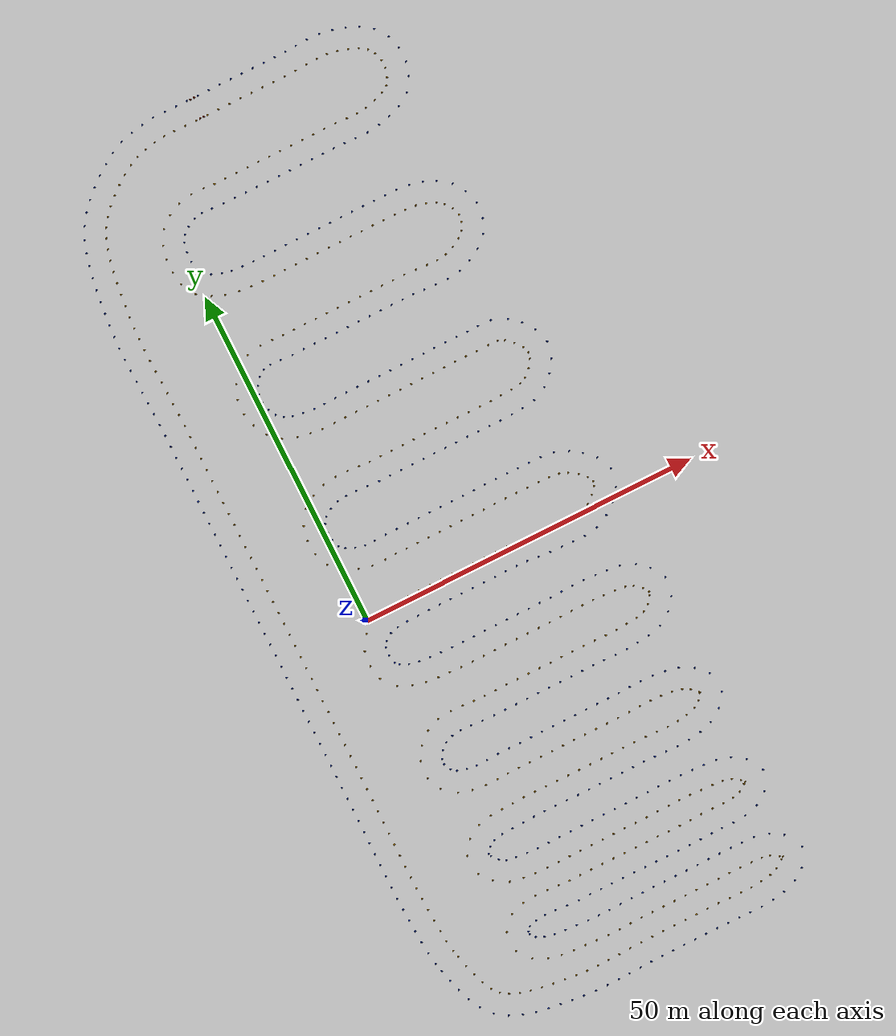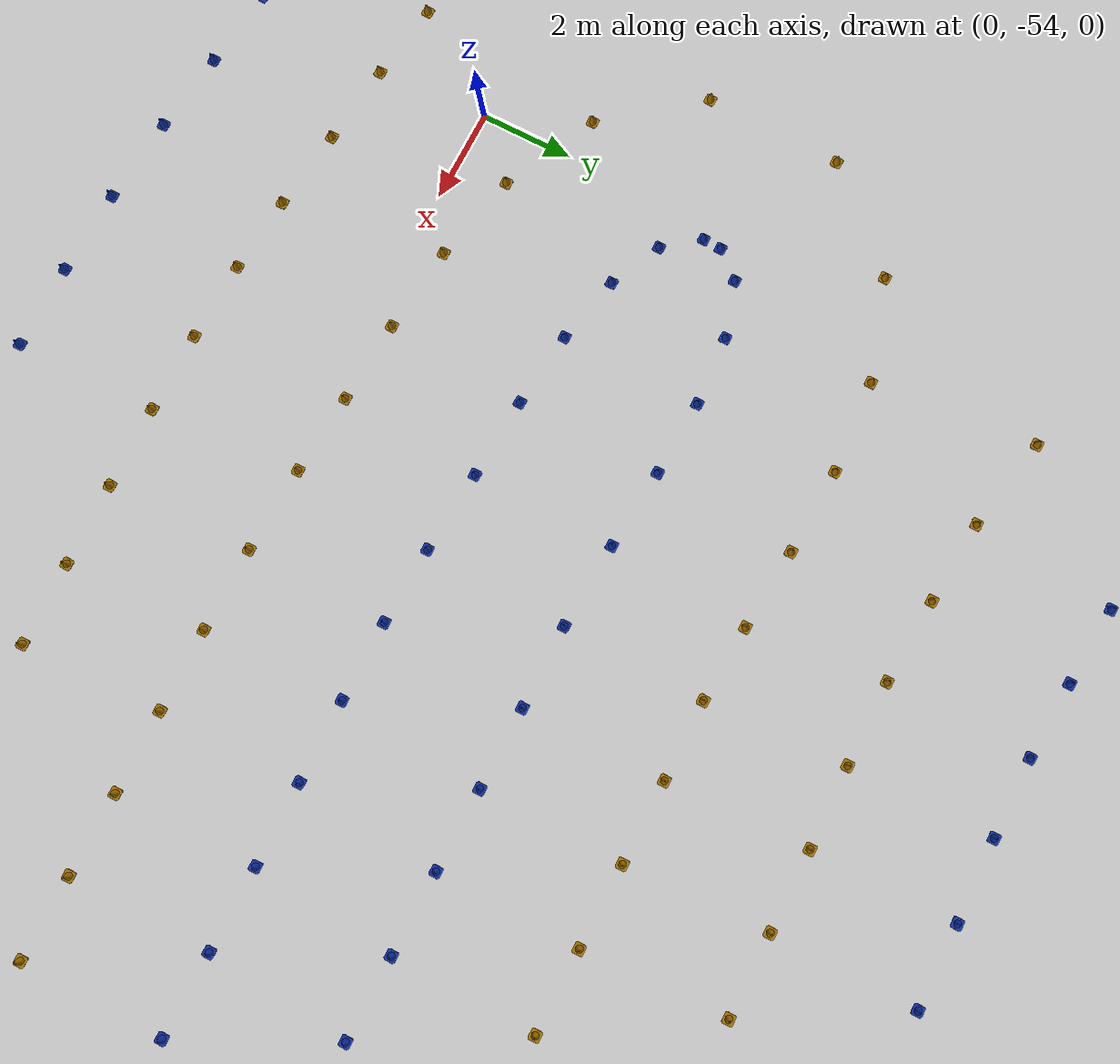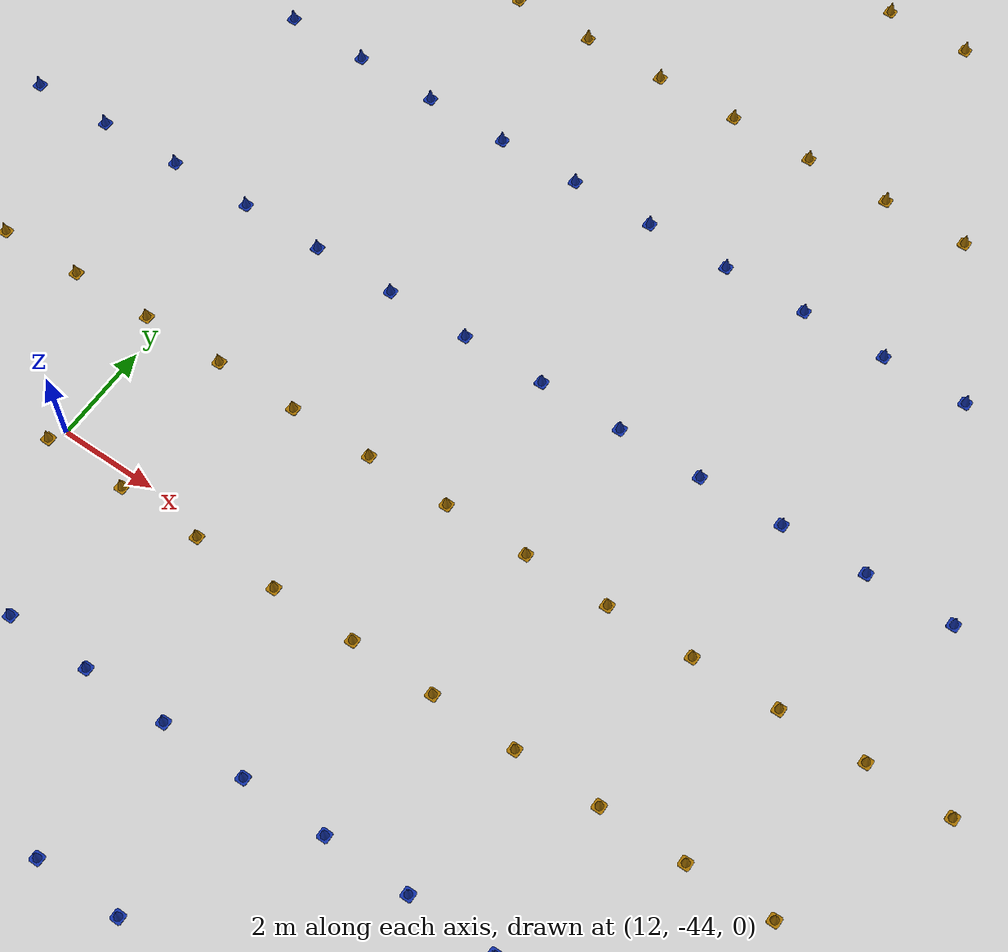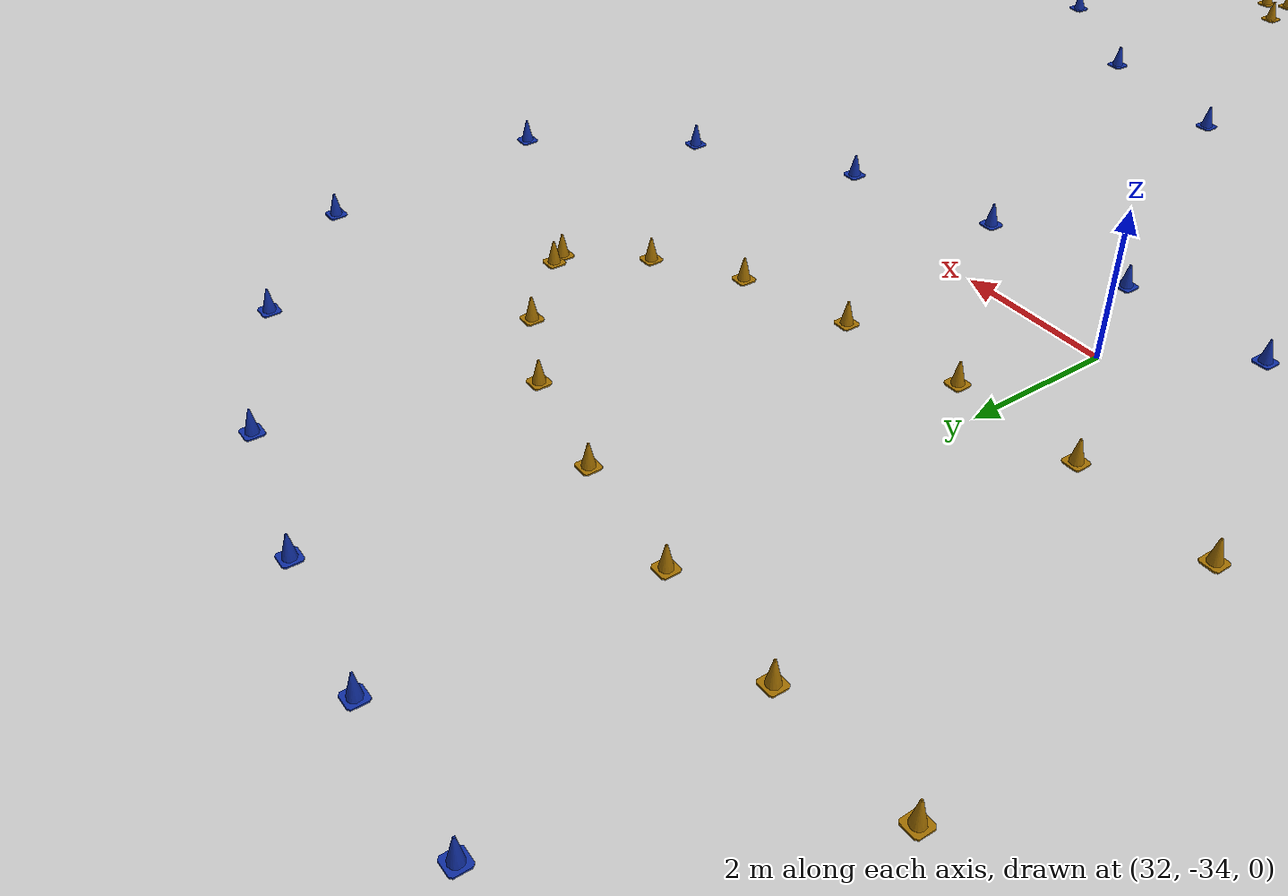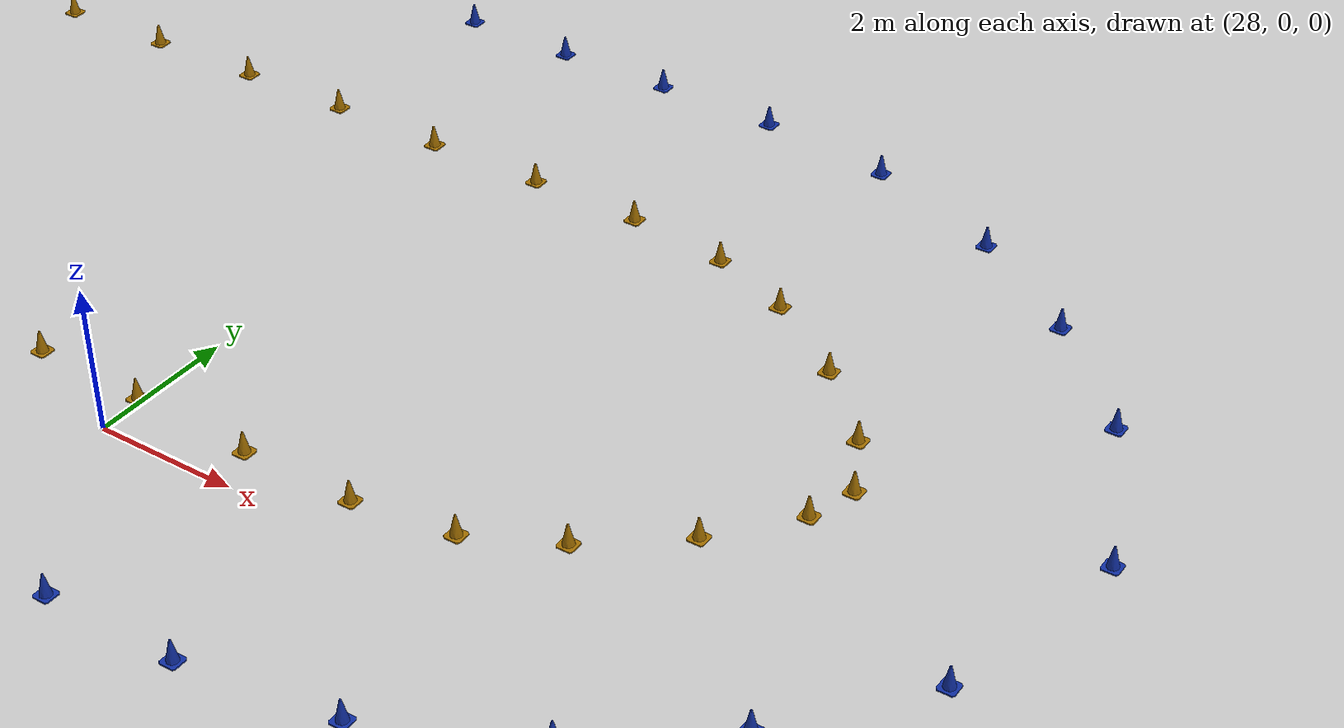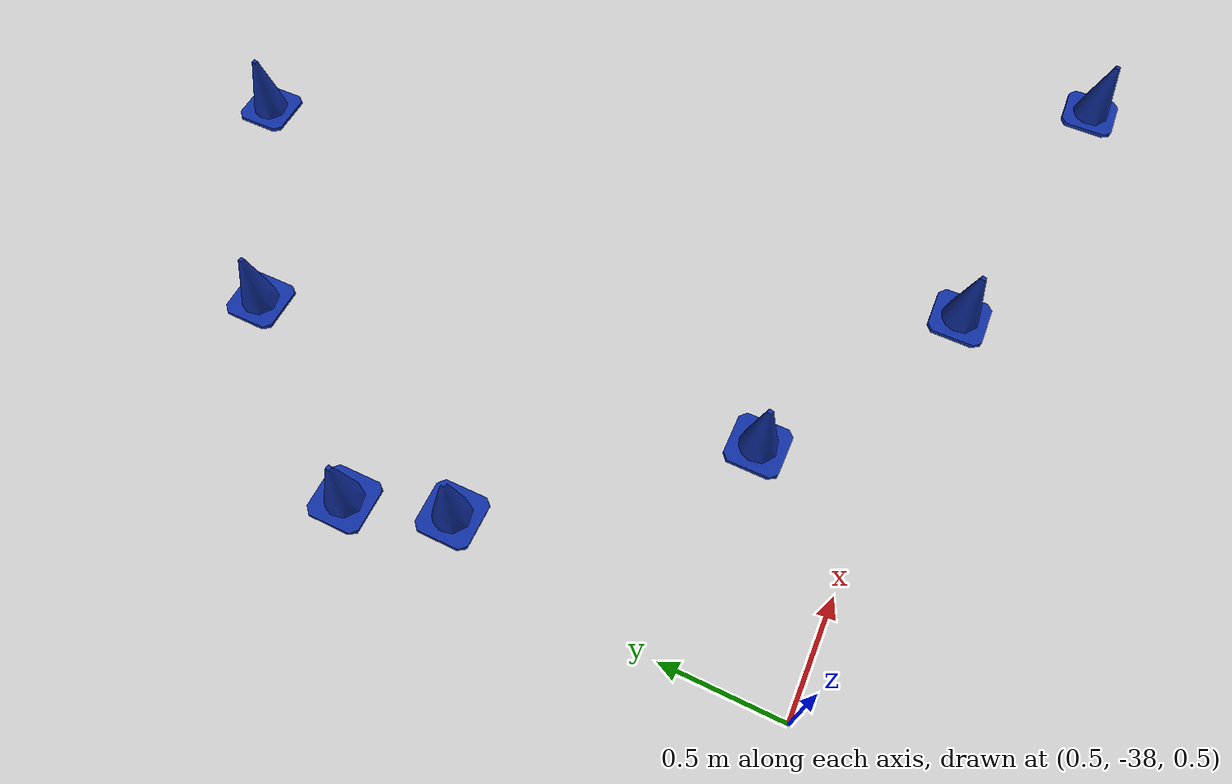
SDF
<sdf version='1.6'>
  <world name='hairpins_increasing_difficulty'>
    <gui fullscreen='0'>
      <camera name='user_camera'>
        <pose frame=''>-40 40 20 0 0.667643 -1</pose>
        <view_controller>orbit</view_controller>
        <projection_type>perspective</projection_type>
      </camera>
    </gui>

    <!-- WORLD SETTINGS -->
    <scene>
      <ambient>1.0 1.0 1.0 1.0</ambient>
      <shadows>false</shadows>
    </scene>

    <spherical_coordinates>
      <heading_deg>180</heading_deg>

      <!-- Appleton Tower coordinates -->
      <latitude_deg>-27.69056</latitude_deg>
      <longitude_deg>152.65461</longitude_deg>
    </spherical_coordinates>

    <light name='sun' type='directional'>
      <cast_shadows>1</cast_shadows>
      <pose frame=''>0 0 10 0 -0 0</pose>
      <diffuse>0.8 0.8 0.8 1</diffuse>
      <specular>0.1 0.1 0.1 1</specular>
      <attenuation>
        <range>1000</range>
        <constant>0.9</constant>
        <linear>0.01</linear>
        <quadratic>0.001</quadratic>
      </attenuation>
      <direction>-0.5 0.5 -1</direction>
    </light>

    <!-- MODELS -->
    <include>
      <uri>model://ground_plane</uri>
      <pose>0.0 0.0 0.0 0 0 0</pose>
    </include>

    <include>
      <uri>model://hairpins_increasing_difficulty</uri>
      <pose>0 0 0.5 0 0 0</pose>
    </include>

  </world>
</sdf>

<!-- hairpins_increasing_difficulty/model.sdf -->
<sdf version='1.6'>
  <model name='track'>

    <include>
      <pose>-12.56258 -47.72453 0.15 0 0 0</pose>
      <uri>model://blue_cone</uri>
      <name>blue_cone_0</name>

      <covariance x="0.01" y="0.01" xy="0.0"/>

    </include>

    <include>
      <pose>-12.1204 -49.38686 0.15 0 0 0</pose>
      <uri>model://blue_cone</uri>
      <name>blue_cone_1</name>

      <covariance x="0.01" y="0.01" xy="0.0"/>

    </include>

    <include>
      <pose>-11.60989 -51.0855 0.15 0 0 0</pose>
      <uri>model://blue_cone</uri>
      <name>blue_cone_2</name>

      <covariance x="0.01" y="0.01" xy="0.0"/>

    </include>

    <include>
      <pose>-10.965589999999999 -52.79916 0.15 0 0 0</pose>
      <uri>model://blue_cone</uri>
      <name>blue_cone_3</name>

      <covariance x="0.01" y="0.01" xy="0.0"/>

    </include>

    <include>
      <pose>-10.08484 -54.50849 0.15 0 0 0</pose>
      <uri>model://blue_cone</uri>
      <name>blue_cone_4</name>

      <covariance x="0.01" y="0.01" xy="0.0"/>

    </include>

    <include>
      <pose>-8.764315 -56.13889 0.15 0 0 0</pose>
      <uri>model://blue_cone</uri>
      <name>blue_cone_5</name>

      <covariance x="0.01" y="0.01" xy="0.0"/>

    </include>

    <include>
      <pose>-7.042822 -57.32252 0.15 0 0 0</pose>
      <uri>model://blue_cone</uri>
      <name>blue_cone_6</name>

      <covariance x="0.01" y="0.01" xy="0.0"/>

    </include>

    <include>
      <pose>-5.253563 -58.06873 0.15 0 0 0</pose>
      <uri>model://blue_cone</uri>
      <name>blue_cone_7</name>

      <covariance x="0.01" y="0.01" xy="0.0"/>

    </include>

    <include>
      <pose>-3.468813 -58.5559 0.15 0 0 0</pose>
      <uri>model://blue_cone</uri>
      <name>blue_cone_8</name>

      <covariance x="0.01" y="0.01" xy="0.0"/>

    </include>

    <include>
      <pose>-1.705197 -58.88723 0.15 0 0 0</pose>
      <uri>model://blue_cone</uri>
      <name>blue_cone_9</name>

      <covariance x="0.01" y="0.01" xy="0.0"/>

    </include>

    <include>
      <pose>0.03300017 -59.12571 0.15 0 0 0</pose>
      <uri>model://blue_cone</uri>
      <name>blue_cone_10</name>

      <covariance x="0.01" y="0.01" xy="0.0"/>

    </include>

    <include>
      <pose>1.7267689999999998 -59.31633000000001 0.15 0 0 0</pose>
      <uri>model://blue_cone</uri>
      <name>blue_cone_11</name>

      <covariance x="0.01" y="0.01" xy="0.0"/>

    </include>

    <include>
      <pose>3.41739 -59.511680000000005 0.15 0 0 0</pose>
      <uri>model://blue_cone</uri>
      <name>blue_cone_12</name>

      <covariance x="0.01" y="0.01" xy="0.0"/>

    </include>

    <include>
      <pose>5.215779 -59.65288 0.15 0 0 0</pose>
      <uri>model://blue_cone</uri>
      <name>blue_cone_13</name>

      <covariance x="0.01" y="0.01" xy="0.0"/>

    </include>

    <include>
      <pose>6.978661 -59.694269999999996 0.15 0 0 0</pose>
      <uri>model://blue_cone</uri>
      <name>blue_cone_14</name>

      <covariance x="0.01" y="0.01" xy="0.0"/>

    </include>

    <include>
      <pose>8.716159 -59.6763 0.15 0 0 0</pose>
      <uri>model://blue_cone</uri>
      <name>blue_cone_15</name>

      <covariance x="0.01" y="0.01" xy="0.0"/>

    </include>

    <include>
      <pose>10.42339 -59.62501999999999 0.15 0 0 0</pose>
      <uri>model://blue_cone</uri>
      <name>blue_cone_16</name>

      <covariance x="0.01" y="0.01" xy="0.0"/>

    </include>

    <include>
      <pose>12.12382 -59.56864 0.15 0 0 0</pose>
      <uri>model://blue_cone</uri>
      <name>blue_cone_17</name>

      <covariance x="0.01" y="0.01" xy="0.0"/>

    </include>

    <include>
      <pose>13.8158 -59.51684 0.15 0 0 0</pose>
      <uri>model://blue_cone</uri>
      <name>blue_cone_18</name>

      <covariance x="0.01" y="0.01" xy="0.0"/>

    </include>

    <include>
      <pose>15.494279999999998 -59.50181 0.15 0 0 0</pose>
      <uri>model://blue_cone</uri>
      <name>blue_cone_19</name>

      <covariance x="0.01" y="0.01" xy="0.0"/>

    </include>

    <include>
      <pose>17.19112 -59.50156 0.15 0 0 0</pose>
      <uri>model://blue_cone</uri>
      <name>blue_cone_20</name>

      <covariance x="0.01" y="0.01" xy="0.0"/>

    </include>

    <include>
      <pose>18.88795 -59.5013 0.15 0 0 0</pose>
      <uri>model://blue_cone</uri>
      <name>blue_cone_21</name>

      <covariance x="0.01" y="0.01" xy="0.0"/>

    </include>

    <include>
      <pose>20.584789999999998 -59.50105 0.15 0 0 0</pose>
      <uri>model://blue_cone</uri>
      <name>blue_cone_22</name>

      <covariance x="0.01" y="0.01" xy="0.0"/>

    </include>

    <include>
      <pose>22.28164 -59.50079 0.15 0 0 0</pose>
      <uri>model://blue_cone</uri>
      <name>blue_cone_23</name>

      <covariance x="0.01" y="0.01" xy="0.0"/>

    </include>

    <include>
      <pose>23.97847 -59.50054 0.15 0 0 0</pose>
      <uri>model://blue_cone</uri>
      <name>blue_cone_24</name>

      <covariance x="0.01" y="0.01" xy="0.0"/>

    </include>

    <include>
      <pose>25.67531 -59.500280000000004 0.15 0 0 0</pose>
      <uri>model://blue_cone</uri>
      <name>blue_cone_25</name>

      <covariance x="0.01" y="0.01" xy="0.0"/>

    </include>

    <include>
      <pose>27.34403 -59.53819 0.15 0 0 0</pose>
      <uri>model://blue_cone</uri>
      <name>blue_cone_26</name>

      <covariance x="0.01" y="0.01" xy="0.0"/>

    </include>

    <include>
      <pose>29.048470000000002 -59.58916 0.15 0 0 0</pose>
      <uri>model://blue_cone</uri>
      <name>blue_cone_27</name>

      <covariance x="0.01" y="0.01" xy="0.0"/>

    </include>

    <include>
      <pose>30.82583 -59.58925 0.15 0 0 0</pose>
      <uri>model://blue_cone</uri>
      <name>blue_cone_28</name>

      <covariance x="0.01" y="0.01" xy="0.0"/>

    </include>

    <include>
      <pose>32.65911 -59.44119 0.15 0 0 0</pose>
      <uri>model://blue_cone</uri>
      <name>blue_cone_29</name>

      <covariance x="0.01" y="0.01" xy="0.0"/>

    </include>

    <include>
      <pose>34.4763 -59.146280000000004 0.15 0 0 0</pose>
      <uri>model://blue_cone</uri>
      <name>blue_cone_30</name>

      <covariance x="0.01" y="0.01" xy="0.0"/>

    </include>

    <include>
      <pose>36.48877 -58.421640000000004 0.15 0 0 0</pose>
      <uri>model://blue_cone</uri>
      <name>blue_cone_31</name>

      <covariance x="0.01" y="0.01" xy="0.0"/>

    </include>

    <include>
      <pose>38.13216 -57.29226 0.15 0 0 0</pose>
      <uri>model://blue_cone</uri>
      <name>blue_cone_32</name>

      <covariance x="0.01" y="0.01" xy="0.0"/>

    </include>

    <include>
      <pose>39.49893 -54.71618 0.15 0 0 0</pose>
      <uri>model://blue_cone</uri>
      <name>blue_cone_33</name>

      <covariance x="0.01" y="0.01" xy="0.0"/>

    </include>

    <include>
      <pose>38.03924 -52.194320000000005 0.15 0 0 0</pose>
      <uri>model://blue_cone</uri>
      <name>blue_cone_34</name>

      <covariance x="0.01" y="0.01" xy="0.0"/>

    </include>

    <include>
      <pose>36.28282 -51.12715 0.15 0 0 0</pose>
      <uri>model://blue_cone</uri>
      <name>blue_cone_35</name>

      <covariance x="0.01" y="0.01" xy="0.0"/>

    </include>

    <include>
      <pose>34.14883 -50.595420000000004 0.15 0 0 0</pose>
      <uri>model://blue_cone</uri>
      <name>blue_cone_36</name>

      <covariance x="0.01" y="0.01" xy="0.0"/>

    </include>

    <include>
      <pose>32.3301 -50.52386 0.15 0 0 0</pose>
      <uri>model://blue_cone</uri>
      <name>blue_cone_37</name>

      <covariance x="0.01" y="0.01" xy="0.0"/>

    </include>

    <include>
      <pose>30.65043 -50.4743 0.15 0 0 0</pose>
      <uri>model://blue_cone</uri>
      <name>blue_cone_38</name>

      <covariance x="0.01" y="0.01" xy="0.0"/>

    </include>

    <include>
      <pose>28.90072 -50.46111 0.15 0 0 0</pose>
      <uri>model://blue_cone</uri>
      <name>blue_cone_39</name>

      <covariance x="0.01" y="0.01" xy="0.0"/>

    </include>

    <include>
      <pose>27.197540000000004 -50.48151 0.15 0 0 0</pose>
      <uri>model://blue_cone</uri>
      <name>blue_cone_40</name>

      <covariance x="0.01" y="0.01" xy="0.0"/>

    </include>

    <include>
      <pose>25.49814 -50.49807 0.15 0 0 0</pose>
      <uri>model://blue_cone</uri>
      <name>blue_cone_41</name>

      <covariance x="0.01" y="0.01" xy="0.0"/>

    </include>

    <include>
      <pose>23.798779999999997 -50.498540000000006 0.15 0 0 0</pose>
      <uri>model://blue_cone</uri>
      <name>blue_cone_42</name>

      <covariance x="0.01" y="0.01" xy="0.0"/>

    </include>

    <include>
      <pose>22.09941 -50.498999999999995 0.15 0 0 0</pose>
      <uri>model://blue_cone</uri>
      <name>blue_cone_43</name>

      <covariance x="0.01" y="0.01" xy="0.0"/>

    </include>

    <include>
      <pose>20.40005 -50.49947 0.15 0 0 0</pose>
      <uri>model://blue_cone</uri>
      <name>blue_cone_44</name>

      <covariance x="0.01" y="0.01" xy="0.0"/>

    </include>

    <include>
      <pose>18.7007 -50.49994 0.15 0 0 0</pose>
      <uri>model://blue_cone</uri>
      <name>blue_cone_45</name>

      <covariance x="0.01" y="0.01" xy="0.0"/>

    </include>

    <include>
      <pose>17.00134 -50.5004 0.15 0 0 0</pose>
      <uri>model://blue_cone</uri>
      <name>blue_cone_46</name>

      <covariance x="0.01" y="0.01" xy="0.0"/>

    </include>

    <include>
      <pose>15.2862 -50.50822 0.15 0 0 0</pose>
      <uri>model://blue_cone</uri>
      <name>blue_cone_47</name>

      <covariance x="0.01" y="0.01" xy="0.0"/>

    </include>

    <include>
      <pose>13.584489999999999 -50.54647 0.15 0 0 0</pose>
      <uri>model://blue_cone</uri>
      <name>blue_cone_48</name>

      <covariance x="0.01" y="0.01" xy="0.0"/>

    </include>

    <include>
      <pose>11.88687 -50.5837 0.15 0 0 0</pose>
      <uri>model://blue_cone</uri>
      <name>blue_cone_49</name>

      <covariance x="0.01" y="0.01" xy="0.0"/>

    </include>

    <include>
      <pose>10.2288 -50.59068 0.15 0 0 0</pose>
      <uri>model://blue_cone</uri>
      <name>blue_cone_50</name>

      <covariance x="0.01" y="0.01" xy="0.0"/>

    </include>

    <include>
      <pose>8.617191 -50.53069 0.15 0 0 0</pose>
      <uri>model://blue_cone</uri>
      <name>blue_cone_51</name>

      <covariance x="0.01" y="0.01" xy="0.0"/>

    </include>

    <include>
      <pose>6.903903 -50.4164 0.15 0 0 0</pose>
      <uri>model://blue_cone</uri>
      <name>blue_cone_52</name>

      <covariance x="0.01" y="0.01" xy="0.0"/>

    </include>

    <include>
      <pose>5.223192 -50.32215 0.15 0 0 0</pose>
      <uri>model://blue_cone</uri>
      <name>blue_cone_53</name>

      <covariance x="0.01" y="0.01" xy="0.0"/>

    </include>

    <include>
      <pose>3.6446199999999997 -50.16146 0.15 0 0 0</pose>
      <uri>model://blue_cone</uri>
      <name>blue_cone_54</name>

      <covariance x="0.01" y="0.01" xy="0.0"/>

    </include>

    <include>
      <pose>2.215255 -49.85229 0.15 0 0 0</pose>
      <uri>model://blue_cone</uri>
      <name>blue_cone_55</name>

      <covariance x="0.01" y="0.01" xy="0.0"/>

    </include>

    <include>
      <pose>1.122366 -49.34872 0.15 0 0 0</pose>
      <uri>model://blue_cone</uri>
      <name>blue_cone_56</name>

      <covariance x="0.01" y="0.01" xy="0.0"/>

    </include>

    <include>
      <pose>0.5595289000000001 -48.627829999999996 0.15 0 0 0</pose>
      <uri>model://blue_cone</uri>
      <name>blue_cone_57</name>

      <covariance x="0.01" y="0.01" xy="0.0"/>

    </include>

    <include>
      <pose>0.5790102 -48.23939 0.15 0 0 0</pose>
      <uri>model://blue_cone</uri>
      <name>blue_cone_58</name>

      <covariance x="0.01" y="0.01" xy="0.0"/>

    </include>

    <include>
      <pose>1.051642 -47.685759999999995 0.15 0 0 0</pose>
      <uri>model://blue_cone</uri>
      <name>blue_cone_59</name>

      <covariance x="0.01" y="0.01" xy="0.0"/>

    </include>

    <include>
      <pose>2.199077 -47.320609999999995 0.15 0 0 0</pose>
      <uri>model://blue_cone</uri>
      <name>blue_cone_60</name>

      <covariance x="0.01" y="0.01" xy="0.0"/>

    </include>

    <include>
      <pose>3.64716 -47.21161 0.15 0 0 0</pose>
      <uri>model://blue_cone</uri>
      <name>blue_cone_61</name>

      <covariance x="0.01" y="0.01" xy="0.0"/>

    </include>

    <include>
      <pose>5.236308999999999 -47.272690000000004 0.15 0 0 0</pose>
      <uri>model://blue_cone</uri>
      <name>blue_cone_62</name>

      <covariance x="0.01" y="0.01" xy="0.0"/>

    </include>

    <include>
      <pose>6.920234 -47.40466 0.15 0 0 0</pose>
      <uri>model://blue_cone</uri>
      <name>blue_cone_63</name>

      <covariance x="0.01" y="0.01" xy="0.0"/>

    </include>

    <include>
      <pose>8.710312 -47.502140000000004 0.15 0 0 0</pose>
      <uri>model://blue_cone</uri>
      <name>blue_cone_64</name>

      <covariance x="0.01" y="0.01" xy="0.0"/>

    </include>

    <include>
      <pose>10.44417 -47.48097 0.15 0 0 0</pose>
      <uri>model://blue_cone</uri>
      <name>blue_cone_65</name>

      <covariance x="0.01" y="0.01" xy="0.0"/>

    </include>

    <include>
      <pose>12.13295 -47.48236 0.15 0 0 0</pose>
      <uri>model://blue_cone</uri>
      <name>blue_cone_66</name>

      <covariance x="0.01" y="0.01" xy="0.0"/>

    </include>

    <include>
      <pose>13.82815 -47.49055 0.15 0 0 0</pose>
      <uri>model://blue_cone</uri>
      <name>blue_cone_67</name>

      <covariance x="0.01" y="0.01" xy="0.0"/>

    </include>

    <include>
      <pose>15.52334 -47.49875 0.15 0 0 0</pose>
      <uri>model://blue_cone</uri>
      <name>blue_cone_68</name>

      <covariance x="0.01" y="0.01" xy="0.0"/>

    </include>

    <include>
      <pose>17.21854 -47.50694 0.15 0 0 0</pose>
      <uri>model://blue_cone</uri>
      <name>blue_cone_69</name>

      <covariance x="0.01" y="0.01" xy="0.0"/>

    </include>

    <include>
      <pose>18.915689999999998 -47.51786 0.15 0 0 0</pose>
      <uri>model://blue_cone</uri>
      <name>blue_cone_70</name>

      <covariance x="0.01" y="0.01" xy="0.0"/>

    </include>

    <include>
      <pose>20.617810000000002 -47.53575 0.15 0 0 0</pose>
      <uri>model://blue_cone</uri>
      <name>blue_cone_71</name>

      <covariance x="0.01" y="0.01" xy="0.0"/>

    </include>

    <include>
      <pose>22.31993 -47.55363 0.15 0 0 0</pose>
      <uri>model://blue_cone</uri>
      <name>blue_cone_72</name>

      <covariance x="0.01" y="0.01" xy="0.0"/>

    </include>

    <include>
      <pose>24.022660000000002 -47.570609999999995 0.15 0 0 0</pose>
      <uri>model://blue_cone</uri>
      <name>blue_cone_73</name>

      <covariance x="0.01" y="0.01" xy="0.0"/>

    </include>

    <include>
      <pose>25.73592 -47.572070000000004 0.15 0 0 0</pose>
      <uri>model://blue_cone</uri>
      <name>blue_cone_74</name>

      <covariance x="0.01" y="0.01" xy="0.0"/>

    </include>

    <include>
      <pose>27.456770000000002 -47.55338 0.15 0 0 0</pose>
      <uri>model://blue_cone</uri>
      <name>blue_cone_75</name>

      <covariance x="0.01" y="0.01" xy="0.0"/>

    </include>

    <include>
      <pose>29.182879999999997 -47.506240000000005 0.15 0 0 0</pose>
      <uri>model://blue_cone</uri>
      <name>blue_cone_76</name>

      <covariance x="0.01" y="0.01" xy="0.0"/>

    </include>

    <include>
      <pose>30.812359999999998 -47.49745 0.15 0 0 0</pose>
      <uri>model://blue_cone</uri>
      <name>blue_cone_77</name>

      <covariance x="0.01" y="0.01" xy="0.0"/>

    </include>

    <include>
      <pose>32.54438 -47.51548 0.15 0 0 0</pose>
      <uri>model://blue_cone</uri>
      <name>blue_cone_78</name>

      <covariance x="0.01" y="0.01" xy="0.0"/>

    </include>

    <include>
      <pose>34.42429 -47.395959999999995 0.15 0 0 0</pose>
      <uri>model://blue_cone</uri>
      <name>blue_cone_79</name>

      <covariance x="0.01" y="0.01" xy="0.0"/>

    </include>

    <include>
      <pose>36.48757 -46.83358 0.15 0 0 0</pose>
      <uri>model://blue_cone</uri>
      <name>blue_cone_80</name>

      <covariance x="0.01" y="0.01" xy="0.0"/>

    </include>

    <include>
      <pose>38.2934 -45.61652 0.15 0 0 0</pose>
      <uri>model://blue_cone</uri>
      <name>blue_cone_81</name>

      <covariance x="0.01" y="0.01" xy="0.0"/>

    </include>

    <include>
      <pose>39.476659999999995 -42.85857 0.15 0 0 0</pose>
      <uri>model://blue_cone</uri>
      <name>blue_cone_82</name>

      <covariance x="0.01" y="0.01" xy="0.0"/>

    </include>

    <include>
      <pose>38.09711 -40.546009999999995 0.15 0 0 0</pose>
      <uri>model://blue_cone</uri>
      <name>blue_cone_83</name>

      <covariance x="0.01" y="0.01" xy="0.0"/>

    </include>

    <include>
      <pose>36.30857 -39.34267 0.15 0 0 0</pose>
      <uri>model://blue_cone</uri>
      <name>blue_cone_84</name>

      <covariance x="0.01" y="0.01" xy="0.0"/>

    </include>

    <include>
      <pose>34.28138 -38.77133 0.15 0 0 0</pose>
      <uri>model://blue_cone</uri>
      <name>blue_cone_85</name>

      <covariance x="0.01" y="0.01" xy="0.0"/>

    </include>

    <include>
      <pose>32.43547 -38.59787 0.15 0 0 0</pose>
      <uri>model://blue_cone</uri>
      <name>blue_cone_86</name>

      <covariance x="0.01" y="0.01" xy="0.0"/>

    </include>

    <include>
      <pose>30.73518 -38.527809999999995 0.15 0 0 0</pose>
      <uri>model://blue_cone</uri>
      <name>blue_cone_87</name>

      <covariance x="0.01" y="0.01" xy="0.0"/>

    </include>

    <include>
      <pose>29.00575 -38.44042 0.15 0 0 0</pose>
      <uri>model://blue_cone</uri>
      <name>blue_cone_88</name>

      <covariance x="0.01" y="0.01" xy="0.0"/>

    </include>

    <include>
      <pose>27.257929999999998 -38.42224 0.15 0 0 0</pose>
      <uri>model://blue_cone</uri>
      <name>blue_cone_89</name>

      <covariance x="0.01" y="0.01" xy="0.0"/>

    </include>

    <include>
      <pose>25.53653 -38.44271 0.15 0 0 0</pose>
      <uri>model://blue_cone</uri>
      <name>blue_cone_90</name>

      <covariance x="0.01" y="0.01" xy="0.0"/>

    </include>

    <include>
      <pose>23.84064 -38.47518 0.15 0 0 0</pose>
      <uri>model://blue_cone</uri>
      <name>blue_cone_91</name>

      <covariance x="0.01" y="0.01" xy="0.0"/>

    </include>

    <include>
      <pose>22.15721 -38.49949 0.15 0 0 0</pose>
      <uri>model://blue_cone</uri>
      <name>blue_cone_92</name>

      <covariance x="0.01" y="0.01" xy="0.0"/>

    </include>

    <include>
      <pose>20.45719 -38.4996 0.15 0 0 0</pose>
      <uri>model://blue_cone</uri>
      <name>blue_cone_93</name>

      <covariance x="0.01" y="0.01" xy="0.0"/>

    </include>

    <include>
      <pose>18.757170000000002 -38.49973 0.15 0 0 0</pose>
      <uri>model://blue_cone</uri>
      <name>blue_cone_94</name>

      <covariance x="0.01" y="0.01" xy="0.0"/>

    </include>

    <include>
      <pose>17.05714 -38.49984 0.15 0 0 0</pose>
      <uri>model://blue_cone</uri>
      <name>blue_cone_95</name>

      <covariance x="0.01" y="0.01" xy="0.0"/>

    </include>

    <include>
      <pose>15.357120000000002 -38.499970000000005 0.15 0 0 0</pose>
      <uri>model://blue_cone</uri>
      <name>blue_cone_96</name>

      <covariance x="0.01" y="0.01" xy="0.0"/>

    </include>

    <include>
      <pose>13.657110000000001 -38.50008 0.15 0 0 0</pose>
      <uri>model://blue_cone</uri>
      <name>blue_cone_97</name>

      <covariance x="0.01" y="0.01" xy="0.0"/>

    </include>

    <include>
      <pose>11.957089999999999 -38.500209999999996 0.15 0 0 0</pose>
      <uri>model://blue_cone</uri>
      <name>blue_cone_98</name>

      <covariance x="0.01" y="0.01" xy="0.0"/>

    </include>

    <include>
      <pose>10.241060000000001 -38.50711 0.15 0 0 0</pose>
      <uri>model://blue_cone</uri>
      <name>blue_cone_99</name>

      <covariance x="0.01" y="0.01" xy="0.0"/>

    </include>

    <include>
      <pose>8.537821000000001 -38.54707 0.15 0 0 0</pose>
      <uri>model://blue_cone</uri>
      <name>blue_cone_100</name>

      <covariance x="0.01" y="0.01" xy="0.0"/>

    </include>

    <include>
      <pose>6.889425999999999 -38.56103 0.15 0 0 0</pose>
      <uri>model://blue_cone</uri>
      <name>blue_cone_101</name>

      <covariance x="0.01" y="0.01" xy="0.0"/>

    </include>

    <include>
      <pose>5.2795440000000005 -38.4679 0.15 0 0 0</pose>
      <uri>model://blue_cone</uri>
      <name>blue_cone_102</name>

      <covariance x="0.01" y="0.01" xy="0.0"/>

    </include>

    <include>
      <pose>3.6312279999999997 -38.34364 0.15 0 0 0</pose>
      <uri>model://blue_cone</uri>
      <name>blue_cone_103</name>

      <covariance x="0.01" y="0.01" xy="0.0"/>

    </include>

    <include>
      <pose>2.2743450000000003 -38.08685 0.15 0 0 0</pose>
      <uri>model://blue_cone</uri>
      <name>blue_cone_104</name>

      <covariance x="0.01" y="0.01" xy="0.0"/>

    </include>

    <include>
      <pose>1.378228 -37.53752 0.15 0 0 0</pose>
      <uri>model://blue_cone</uri>
      <name>blue_cone_105</name>

      <covariance x="0.01" y="0.01" xy="0.0"/>

    </include>

    <include>
      <pose>0.6321018 -36.61217 0.15 0 0 0</pose>
      <uri>model://blue_cone</uri>
      <name>blue_cone_106</name>

      <covariance x="0.01" y="0.01" xy="0.0"/>

    </include>

    <include>
      <pose>0.5142131 -36.220279999999995 0.15 0 0 0</pose>
      <uri>model://blue_cone</uri>
      <name>blue_cone_107</name>

      <covariance x="0.01" y="0.01" xy="0.0"/>

    </include>

    <include>
      <pose>1.120954 -35.43764 0.15 0 0 0</pose>
      <uri>model://blue_cone</uri>
      <name>blue_cone_108</name>

      <covariance x="0.01" y="0.01" xy="0.0"/>

    </include>

    <include>
      <pose>2.035592 -34.87965 0.15 0 0 0</pose>
      <uri>model://blue_cone</uri>
      <name>blue_cone_109</name>

      <covariance x="0.01" y="0.01" xy="0.0"/>

    </include>

    <include>
      <pose>3.363218 -34.62754 0.15 0 0 0</pose>
      <uri>model://blue_cone</uri>
      <name>blue_cone_110</name>

      <covariance x="0.01" y="0.01" xy="0.0"/>

    </include>

    <include>
      <pose>4.956716 -34.55118 0.15 0 0 0</pose>
      <uri>model://blue_cone</uri>
      <name>blue_cone_111</name>

      <covariance x="0.01" y="0.01" xy="0.0"/>

    </include>

    <include>
      <pose>6.706681 -34.49467 0.15 0 0 0</pose>
      <uri>model://blue_cone</uri>
      <name>blue_cone_112</name>

      <covariance x="0.01" y="0.01" xy="0.0"/>

    </include>

    <include>
      <pose>8.339858 -34.43247 0.15 0 0 0</pose>
      <uri>model://blue_cone</uri>
      <name>blue_cone_113</name>

      <covariance x="0.01" y="0.01" xy="0.0"/>

    </include>

    <include>
      <pose>10.00415 -34.42902 0.15 0 0 0</pose>
      <uri>model://blue_cone</uri>
      <name>blue_cone_114</name>

      <covariance x="0.01" y="0.01" xy="0.0"/>

    </include>

    <include>
      <pose>11.694 -34.45192 0.15 0 0 0</pose>
      <uri>model://blue_cone</uri>
      <name>blue_cone_115</name>

      <covariance x="0.01" y="0.01" xy="0.0"/>

    </include>

    <include>
      <pose>13.39546 -34.48141 0.15 0 0 0</pose>
      <uri>model://blue_cone</uri>
      <name>blue_cone_116</name>

      <covariance x="0.01" y="0.01" xy="0.0"/>

    </include>

    <include>
      <pose>15.11408 -34.5 0.15 0 0 0</pose>
      <uri>model://blue_cone</uri>
      <name>blue_cone_117</name>

      <covariance x="0.01" y="0.01" xy="0.0"/>

    </include>

    <include>
      <pose>16.81278 -34.50005 0.15 0 0 0</pose>
      <uri>model://blue_cone</uri>
      <name>blue_cone_118</name>

      <covariance x="0.01" y="0.01" xy="0.0"/>

    </include>

    <include>
      <pose>18.51148 -34.5001 0.15 0 0 0</pose>
      <uri>model://blue_cone</uri>
      <name>blue_cone_119</name>

      <covariance x="0.01" y="0.01" xy="0.0"/>

    </include>

    <include>
      <pose>20.21017 -34.50015 0.15 0 0 0</pose>
      <uri>model://blue_cone</uri>
      <name>blue_cone_120</name>

      <covariance x="0.01" y="0.01" xy="0.0"/>

    </include>

    <include>
      <pose>21.90887 -34.5002 0.15 0 0 0</pose>
      <uri>model://blue_cone</uri>
      <name>blue_cone_121</name>

      <covariance x="0.01" y="0.01" xy="0.0"/>

    </include>

    <include>
      <pose>23.607570000000003 -34.500240000000005 0.15 0 0 0</pose>
      <uri>model://blue_cone</uri>
      <name>blue_cone_122</name>

      <covariance x="0.01" y="0.01" xy="0.0"/>

    </include>

    <include>
      <pose>25.306279999999997 -34.50029 0.15 0 0 0</pose>
      <uri>model://blue_cone</uri>
      <name>blue_cone_123</name>

      <covariance x="0.01" y="0.01" xy="0.0"/>

    </include>

    <include>
      <pose>26.96048 -34.5363 0.15 0 0 0</pose>
      <uri>model://blue_cone</uri>
      <name>blue_cone_124</name>

      <covariance x="0.01" y="0.01" xy="0.0"/>

    </include>

    <include>
      <pose>28.657009999999996 -34.608259999999994 0.15 0 0 0</pose>
      <uri>model://blue_cone</uri>
      <name>blue_cone_125</name>

      <covariance x="0.01" y="0.01" xy="0.0"/>

    </include>

    <include>
      <pose>30.40376 -34.65488 0.15 0 0 0</pose>
      <uri>model://blue_cone</uri>
      <name>blue_cone_126</name>

      <covariance x="0.01" y="0.01" xy="0.0"/>

    </include>

    <include>
      <pose>32.23082 -34.59527 0.15 0 0 0</pose>
      <uri>model://blue_cone</uri>
      <name>blue_cone_127</name>

      <covariance x="0.01" y="0.01" xy="0.0"/>

    </include>

    <include>
      <pose>34.09482 -34.319309999999994 0.15 0 0 0</pose>
      <uri>model://blue_cone</uri>
      <name>blue_cone_128</name>

      <covariance x="0.01" y="0.01" xy="0.0"/>

    </include>

    <include>
      <pose>35.99429 -33.760220000000004 0.15 0 0 0</pose>
      <uri>model://blue_cone</uri>
      <name>blue_cone_129</name>

      <covariance x="0.01" y="0.01" xy="0.0"/>

    </include>

    <include>
      <pose>37.84623 -32.54126 0.15 0 0 0</pose>
      <uri>model://blue_cone</uri>
      <name>blue_cone_130</name>

      <covariance x="0.01" y="0.01" xy="0.0"/>

    </include>

    <include>
      <pose>39.23379 -30.6971 0.15 0 0 0</pose>
      <uri>model://blue_cone</uri>
      <name>blue_cone_131</name>

      <covariance x="0.01" y="0.01" xy="0.0"/>

    </include>

    <include>
      <pose>38.889179999999996 -27.66191 0.15 0 0 0</pose>
      <uri>model://blue_cone</uri>
      <name>blue_cone_132</name>

      <covariance x="0.01" y="0.01" xy="0.0"/>

    </include>

    <include>
      <pose>37.35595 -26.10582 0.15 0 0 0</pose>
      <uri>model://blue_cone</uri>
      <name>blue_cone_133</name>

      <covariance x="0.01" y="0.01" xy="0.0"/>

    </include>

    <include>
      <pose>35.414359999999995 -25.08462 0.15 0 0 0</pose>
      <uri>model://blue_cone</uri>
      <name>blue_cone_134</name>

      <covariance x="0.01" y="0.01" xy="0.0"/>

    </include>

    <include>
      <pose>33.53106 -24.6616 0.15 0 0 0</pose>
      <uri>model://blue_cone</uri>
      <name>blue_cone_135</name>

      <covariance x="0.01" y="0.01" xy="0.0"/>

    </include>

    <include>
      <pose>31.72788 -24.43843 0.15 0 0 0</pose>
      <uri>model://blue_cone</uri>
      <name>blue_cone_136</name>

      <covariance x="0.01" y="0.01" xy="0.0"/>

    </include>

    <include>
      <pose>29.91423 -24.37661 0.15 0 0 0</pose>
      <uri>model://blue_cone</uri>
      <name>blue_cone_137</name>

      <covariance x="0.01" y="0.01" xy="0.0"/>

    </include>

    <include>
      <pose>28.174740000000003 -24.41102 0.15 0 0 0</pose>
      <uri>model://blue_cone</uri>
      <name>blue_cone_138</name>

      <covariance x="0.01" y="0.01" xy="0.0"/>

    </include>

    <include>
      <pose>26.47227 -24.46823 0.15 0 0 0</pose>
      <uri>model://blue_cone</uri>
      <name>blue_cone_139</name>

      <covariance x="0.01" y="0.01" xy="0.0"/>

    </include>

    <include>
      <pose>24.81161 -24.49994 0.15 0 0 0</pose>
      <uri>model://blue_cone</uri>
      <name>blue_cone_140</name>

      <covariance x="0.01" y="0.01" xy="0.0"/>

    </include>

    <include>
      <pose>23.11122 -24.49996 0.15 0 0 0</pose>
      <uri>model://blue_cone</uri>
      <name>blue_cone_141</name>

      <covariance x="0.01" y="0.01" xy="0.0"/>

    </include>

    <include>
      <pose>21.410829999999997 -24.499979999999997 0.15 0 0 0</pose>
      <uri>model://blue_cone</uri>
      <name>blue_cone_142</name>

      <covariance x="0.01" y="0.01" xy="0.0"/>

    </include>

    <include>
      <pose>19.71043 -24.50001 0.15 0 0 0</pose>
      <uri>model://blue_cone</uri>
      <name>blue_cone_143</name>

      <covariance x="0.01" y="0.01" xy="0.0"/>

    </include>

    <include>
      <pose>18.01005 -24.50003 0.15 0 0 0</pose>
      <uri>model://blue_cone</uri>
      <name>blue_cone_144</name>

      <covariance x="0.01" y="0.01" xy="0.0"/>

    </include>

    <include>
      <pose>16.30965 -24.50005 0.15 0 0 0</pose>
      <uri>model://blue_cone</uri>
      <name>blue_cone_145</name>

      <covariance x="0.01" y="0.01" xy="0.0"/>

    </include>

    <include>
      <pose>14.60926 -24.50008 0.15 0 0 0</pose>
      <uri>model://blue_cone</uri>
      <name>blue_cone_146</name>

      <covariance x="0.01" y="0.01" xy="0.0"/>

    </include>

    <include>
      <pose>12.90887 -24.5001 0.15 0 0 0</pose>
      <uri>model://blue_cone</uri>
      <name>blue_cone_147</name>

      <covariance x="0.01" y="0.01" xy="0.0"/>

    </include>

    <include>
      <pose>11.20848 -24.500120000000003 0.15 0 0 0</pose>
      <uri>model://blue_cone</uri>
      <name>blue_cone_148</name>

      <covariance x="0.01" y="0.01" xy="0.0"/>

    </include>

    <include>
      <pose>9.508091 -24.50014 0.15 0 0 0</pose>
      <uri>model://blue_cone</uri>
      <name>blue_cone_149</name>

      <covariance x="0.01" y="0.01" xy="0.0"/>

    </include>

    <include>
      <pose>7.807701 -24.50017 0.15 0 0 0</pose>
      <uri>model://blue_cone</uri>
      <name>blue_cone_150</name>

      <covariance x="0.01" y="0.01" xy="0.0"/>

    </include>

    <include>
      <pose>6.054794 -24.55614 0.15 0 0 0</pose>
      <uri>model://blue_cone</uri>
      <name>blue_cone_151</name>

      <covariance x="0.01" y="0.01" xy="0.0"/>

    </include>

    <include>
      <pose>4.459087 -24.590770000000003 0.15 0 0 0</pose>
      <uri>model://blue_cone</uri>
      <name>blue_cone_152</name>

      <covariance x="0.01" y="0.01" xy="0.0"/>

    </include>

    <include>
      <pose>3.026295 -24.40888 0.15 0 0 0</pose>
      <uri>model://blue_cone</uri>
      <name>blue_cone_153</name>

      <covariance x="0.01" y="0.01" xy="0.0"/>

    </include>

    <include>
      <pose>1.7103099999999998 -24.031129999999997 0.15 0 0 0</pose>
      <uri>model://blue_cone</uri>
      <name>blue_cone_154</name>

      <covariance x="0.01" y="0.01" xy="0.0"/>

    </include>

    <include>
      <pose>1.024394 -23.45857 0.15 0 0 0</pose>
      <uri>model://blue_cone</uri>
      <name>blue_cone_155</name>

      <covariance x="0.01" y="0.01" xy="0.0"/>

    </include>

    <include>
      <pose>0.5354365 -22.45394 0.15 0 0 0</pose>
      <uri>model://blue_cone</uri>
      <name>blue_cone_156</name>

      <covariance x="0.01" y="0.01" xy="0.0"/>

    </include>

    <include>
      <pose>0.6297027 -21.703889999999998 0.15 0 0 0</pose>
      <uri>model://blue_cone</uri>
      <name>blue_cone_157</name>

      <covariance x="0.01" y="0.01" xy="0.0"/>

    </include>

    <include>
      <pose>1.265808 -20.628239999999998 0.15 0 0 0</pose>
      <uri>model://blue_cone</uri>
      <name>blue_cone_158</name>

      <covariance x="0.01" y="0.01" xy="0.0"/>

    </include>

    <include>
      <pose>2.135672 -19.90776 0.15 0 0 0</pose>
      <uri>model://blue_cone</uri>
      <name>blue_cone_159</name>

      <covariance x="0.01" y="0.01" xy="0.0"/>

    </include>

    <include>
      <pose>3.299088 -19.42922 0.15 0 0 0</pose>
      <uri>model://blue_cone</uri>
      <name>blue_cone_160</name>

      <covariance x="0.01" y="0.01" xy="0.0"/>

    </include>

    <include>
      <pose>4.6657839999999995 -19.2901 0.15 0 0 0</pose>
      <uri>model://blue_cone</uri>
      <name>blue_cone_161</name>

      <covariance x="0.01" y="0.01" xy="0.0"/>

    </include>

    <include>
      <pose>6.246157 -19.34345 0.15 0 0 0</pose>
      <uri>model://blue_cone</uri>
      <name>blue_cone_162</name>

      <covariance x="0.01" y="0.01" xy="0.0"/>

    </include>

    <include>
      <pose>7.951028 -19.46106 0.15 0 0 0</pose>
      <uri>model://blue_cone</uri>
      <name>blue_cone_163</name>

      <covariance x="0.01" y="0.01" xy="0.0"/>

    </include>

    <include>
      <pose>9.730416 -19.49985 0.15 0 0 0</pose>
      <uri>model://blue_cone</uri>
      <name>blue_cone_164</name>

      <covariance x="0.01" y="0.01" xy="0.0"/>

    </include>

    <include>
      <pose>11.43035 -19.49993 0.15 0 0 0</pose>
      <uri>model://blue_cone</uri>
      <name>blue_cone_165</name>

      <covariance x="0.01" y="0.01" xy="0.0"/>

    </include>

    <include>
      <pose>13.130320000000001 -19.5 0.15 0 0 0</pose>
      <uri>model://blue_cone</uri>
      <name>blue_cone_166</name>

      <covariance x="0.01" y="0.01" xy="0.0"/>

    </include>

    <include>
      <pose>14.830279999999998 -19.50007 0.15 0 0 0</pose>
      <uri>model://blue_cone</uri>
      <name>blue_cone_167</name>

      <covariance x="0.01" y="0.01" xy="0.0"/>

    </include>

    <include>
      <pose>16.53022 -19.50014 0.15 0 0 0</pose>
      <uri>model://blue_cone</uri>
      <name>blue_cone_168</name>

      <covariance x="0.01" y="0.01" xy="0.0"/>

    </include>

    <include>
      <pose>18.230179999999997 -19.50021 0.15 0 0 0</pose>
      <uri>model://blue_cone</uri>
      <name>blue_cone_169</name>

      <covariance x="0.01" y="0.01" xy="0.0"/>

    </include>

    <include>
      <pose>19.93011 -19.50028 0.15 0 0 0</pose>
      <uri>model://blue_cone</uri>
      <name>blue_cone_170</name>

      <covariance x="0.01" y="0.01" xy="0.0"/>

    </include>

    <include>
      <pose>21.63008 -19.50035 0.15 0 0 0</pose>
      <uri>model://blue_cone</uri>
      <name>blue_cone_171</name>

      <covariance x="0.01" y="0.01" xy="0.0"/>

    </include>

    <include>
      <pose>23.33002 -19.500429999999998 0.15 0 0 0</pose>
      <uri>model://blue_cone</uri>
      <name>blue_cone_172</name>

      <covariance x="0.01" y="0.01" xy="0.0"/>

    </include>

    <include>
      <pose>25.02998 -19.5005 0.15 0 0 0</pose>
      <uri>model://blue_cone</uri>
      <name>blue_cone_173</name>

      <covariance x="0.01" y="0.01" xy="0.0"/>

    </include>

    <include>
      <pose>26.711809999999996 -19.5348 0.15 0 0 0</pose>
      <uri>model://blue_cone</uri>
      <name>blue_cone_174</name>

      <covariance x="0.01" y="0.01" xy="0.0"/>

    </include>

    <include>
      <pose>28.417379999999998 -19.57262 0.15 0 0 0</pose>
      <uri>model://blue_cone</uri>
      <name>blue_cone_175</name>

      <covariance x="0.01" y="0.01" xy="0.0"/>

    </include>

    <include>
      <pose>30.19075 -19.56038 0.15 0 0 0</pose>
      <uri>model://blue_cone</uri>
      <name>blue_cone_176</name>

      <covariance x="0.01" y="0.01" xy="0.0"/>

    </include>

    <include>
      <pose>31.94296 -19.439770000000003 0.15 0 0 0</pose>
      <uri>model://blue_cone</uri>
      <name>blue_cone_177</name>

      <covariance x="0.01" y="0.01" xy="0.0"/>

    </include>

    <include>
      <pose>33.72906 -19.27492 0.15 0 0 0</pose>
      <uri>model://blue_cone</uri>
      <name>blue_cone_178</name>

      <covariance x="0.01" y="0.01" xy="0.0"/>

    </include>

    <include>
      <pose>35.75286 -18.764329999999998 0.15 0 0 0</pose>
      <uri>model://blue_cone</uri>
      <name>blue_cone_179</name>

      <covariance x="0.01" y="0.01" xy="0.0"/>

    </include>

    <include>
      <pose>37.58409 -17.51912 0.15 0 0 0</pose>
      <uri>model://blue_cone</uri>
      <name>blue_cone_180</name>

      <covariance x="0.01" y="0.01" xy="0.0"/>

    </include>

    <include>
      <pose>38.93845 -15.853589999999999 0.15 0 0 0</pose>
      <uri>model://blue_cone</uri>
      <name>blue_cone_181</name>

      <covariance x="0.01" y="0.01" xy="0.0"/>

    </include>

    <include>
      <pose>39.385329999999996 -13.09469 0.15 0 0 0</pose>
      <uri>model://blue_cone</uri>
      <name>blue_cone_182</name>

      <covariance x="0.01" y="0.01" xy="0.0"/>

    </include>

    <include>
      <pose>38.158409999999996 -11.02937 0.15 0 0 0</pose>
      <uri>model://blue_cone</uri>
      <name>blue_cone_183</name>

      <covariance x="0.01" y="0.01" xy="0.0"/>

    </include>

    <include>
      <pose>36.57826 -9.700365 0.15 0 0 0</pose>
      <uri>model://blue_cone</uri>
      <name>blue_cone_184</name>

      <covariance x="0.01" y="0.01" xy="0.0"/>

    </include>

    <include>
      <pose>34.50323 -8.868497 0.15 0 0 0</pose>
      <uri>model://blue_cone</uri>
      <name>blue_cone_185</name>

      <covariance x="0.01" y="0.01" xy="0.0"/>

    </include>

    <include>
      <pose>32.62165 -8.618314 0.15 0 0 0</pose>
      <uri>model://blue_cone</uri>
      <name>blue_cone_186</name>

      <covariance x="0.01" y="0.01" xy="0.0"/>

    </include>

    <include>
      <pose>30.92613 -8.498581 0.15 0 0 0</pose>
      <uri>model://blue_cone</uri>
      <name>blue_cone_187</name>

      <covariance x="0.01" y="0.01" xy="0.0"/>

    </include>

    <include>
      <pose>29.138820000000003 -8.41463 0.15 0 0 0</pose>
      <uri>model://blue_cone</uri>
      <name>blue_cone_188</name>

      <covariance x="0.01" y="0.01" xy="0.0"/>

    </include>

    <include>
      <pose>27.39204 -8.414774000000001 0.15 0 0 0</pose>
      <uri>model://blue_cone</uri>
      <name>blue_cone_189</name>

      <covariance x="0.01" y="0.01" xy="0.0"/>

    </include>

    <include>
      <pose>25.6828 -8.449398 0.15 0 0 0</pose>
      <uri>model://blue_cone</uri>
      <name>blue_cone_190</name>

      <covariance x="0.01" y="0.01" xy="0.0"/>

    </include>

    <include>
      <pose>23.98497 -8.489141 0.15 0 0 0</pose>
      <uri>model://blue_cone</uri>
      <name>blue_cone_191</name>

      <covariance x="0.01" y="0.01" xy="0.0"/>

    </include>

    <include>
      <pose>22.299310000000002 -8.498419 0.15 0 0 0</pose>
      <uri>model://blue_cone</uri>
      <name>blue_cone_192</name>

      <covariance x="0.01" y="0.01" xy="0.0"/>

    </include>

    <include>
      <pose>20.60024 -8.499016000000001 0.15 0 0 0</pose>
      <uri>model://blue_cone</uri>
      <name>blue_cone_193</name>

      <covariance x="0.01" y="0.01" xy="0.0"/>

    </include>

    <include>
      <pose>18.90119 -8.499613 0.15 0 0 0</pose>
      <uri>model://blue_cone</uri>
      <name>blue_cone_194</name>

      <covariance x="0.01" y="0.01" xy="0.0"/>

    </include>

    <include>
      <pose>17.20212 -8.500209 0.15 0 0 0</pose>
      <uri>model://blue_cone</uri>
      <name>blue_cone_195</name>

      <covariance x="0.01" y="0.01" xy="0.0"/>

    </include>

    <include>
      <pose>15.503079999999999 -8.500805 0.15 0 0 0</pose>
      <uri>model://blue_cone</uri>
      <name>blue_cone_196</name>

      <covariance x="0.01" y="0.01" xy="0.0"/>

    </include>

    <include>
      <pose>13.80287 -8.511122 0.15 0 0 0</pose>
      <uri>model://blue_cone</uri>
      <name>blue_cone_197</name>

      <covariance x="0.01" y="0.01" xy="0.0"/>

    </include>

    <include>
      <pose>12.101289999999999 -8.532982 0.15 0 0 0</pose>
      <uri>model://blue_cone</uri>
      <name>blue_cone_198</name>

      <covariance x="0.01" y="0.01" xy="0.0"/>

    </include>

    <include>
      <pose>10.414819999999999 -8.547234 0.15 0 0 0</pose>
      <uri>model://blue_cone</uri>
      <name>blue_cone_199</name>

      <covariance x="0.01" y="0.01" xy="0.0"/>

    </include>

    <include>
      <pose>8.774594 -8.517014 0.15 0 0 0</pose>
      <uri>model://blue_cone</uri>
      <name>blue_cone_200</name>

      <covariance x="0.01" y="0.01" xy="0.0"/>

    </include>

    <include>
      <pose>7.081214999999999 -8.444529 0.15 0 0 0</pose>
      <uri>model://blue_cone</uri>
      <name>blue_cone_201</name>

      <covariance x="0.01" y="0.01" xy="0.0"/>

    </include>

    <include>
      <pose>5.411514 -8.367693 0.15 0 0 0</pose>
      <uri>model://blue_cone</uri>
      <name>blue_cone_202</name>

      <covariance x="0.01" y="0.01" xy="0.0"/>

    </include>

    <include>
      <pose>3.834973 -8.214634 0.15 0 0 0</pose>
      <uri>model://blue_cone</uri>
      <name>blue_cone_203</name>

      <covariance x="0.01" y="0.01" xy="0.0"/>

    </include>

    <include>
      <pose>2.4188549999999998 -7.911144 0.15 0 0 0</pose>
      <uri>model://blue_cone</uri>
      <name>blue_cone_204</name>

      <covariance x="0.01" y="0.01" xy="0.0"/>

    </include>

    <include>
      <pose>1.228416 -7.368662 0.15 0 0 0</pose>
      <uri>model://blue_cone</uri>
      <name>blue_cone_205</name>

      <covariance x="0.01" y="0.01" xy="0.0"/>

    </include>

    <include>
      <pose>0.727603 -6.839866000000001 0.15 0 0 0</pose>
      <uri>model://blue_cone</uri>
      <name>blue_cone_206</name>

      <covariance x="0.01" y="0.01" xy="0.0"/>

    </include>

    <include>
      <pose>0.5087550000000001 -5.633926 0.15 0 0 0</pose>
      <uri>model://blue_cone</uri>
      <name>blue_cone_207</name>

      <covariance x="0.01" y="0.01" xy="0.0"/>

    </include>

    <include>
      <pose>0.6213632 -4.444017 0.15 0 0 0</pose>
      <uri>model://blue_cone</uri>
      <name>blue_cone_208</name>

      <covariance x="0.01" y="0.01" xy="0.0"/>

    </include>

    <include>
      <pose>1.1237139999999999 -3.703149 0.15 0 0 0</pose>
      <uri>model://blue_cone</uri>
      <name>blue_cone_209</name>

      <covariance x="0.01" y="0.01" xy="0.0"/>

    </include>

    <include>
      <pose>2.118643 -2.995854 0.15 0 0 0</pose>
      <uri>model://blue_cone</uri>
      <name>blue_cone_210</name>

      <covariance x="0.01" y="0.01" xy="0.0"/>

    </include>

    <include>
      <pose>3.317575 -2.672791 0.15 0 0 0</pose>
      <uri>model://blue_cone</uri>
      <name>blue_cone_211</name>

      <covariance x="0.01" y="0.01" xy="0.0"/>

    </include>

    <include>
      <pose>4.842771 -2.552716 0.15 0 0 0</pose>
      <uri>model://blue_cone</uri>
      <name>blue_cone_212</name>

      <covariance x="0.01" y="0.01" xy="0.0"/>

    </include>

    <include>
      <pose>6.525741 -2.523128 0.15 0 0 0</pose>
      <uri>model://blue_cone</uri>
      <name>blue_cone_213</name>

      <covariance x="0.01" y="0.01" xy="0.0"/>

    </include>

    <include>
      <pose>8.211266 -2.473836 0.15 0 0 0</pose>
      <uri>model://blue_cone</uri>
      <name>blue_cone_214</name>

      <covariance x="0.01" y="0.01" xy="0.0"/>

    </include>

    <include>
      <pose>9.882726 -2.4811400000000003 0.15 0 0 0</pose>
      <uri>model://blue_cone</uri>
      <name>blue_cone_215</name>

      <covariance x="0.01" y="0.01" xy="0.0"/>

    </include>

    <include>
      <pose>11.58314 -2.4989470000000003 0.15 0 0 0</pose>
      <uri>model://blue_cone</uri>
      <name>blue_cone_216</name>

      <covariance x="0.01" y="0.01" xy="0.0"/>

    </include>

    <include>
      <pose>13.287560000000001 -2.49896 0.15 0 0 0</pose>
      <uri>model://blue_cone</uri>
      <name>blue_cone_217</name>

      <covariance x="0.01" y="0.01" xy="0.0"/>

    </include>

    <include>
      <pose>14.991979999999998 -2.498973 0.15 0 0 0</pose>
      <uri>model://blue_cone</uri>
      <name>blue_cone_218</name>

      <covariance x="0.01" y="0.01" xy="0.0"/>

    </include>

    <include>
      <pose>16.69637 -2.498986 0.15 0 0 0</pose>
      <uri>model://blue_cone</uri>
      <name>blue_cone_219</name>

      <covariance x="0.01" y="0.01" xy="0.0"/>

    </include>

    <include>
      <pose>18.39923 -2.495316 0.15 0 0 0</pose>
      <uri>model://blue_cone</uri>
      <name>blue_cone_220</name>

      <covariance x="0.01" y="0.01" xy="0.0"/>

    </include>

    <include>
      <pose>20.09744 -2.480718 0.15 0 0 0</pose>
      <uri>model://blue_cone</uri>
      <name>blue_cone_221</name>

      <covariance x="0.01" y="0.01" xy="0.0"/>

    </include>

    <include>
      <pose>21.770889999999998 -2.480506 0.15 0 0 0</pose>
      <uri>model://blue_cone</uri>
      <name>blue_cone_222</name>

      <covariance x="0.01" y="0.01" xy="0.0"/>

    </include>

    <include>
      <pose>23.375 -2.549887 0.15 0 0 0</pose>
      <uri>model://blue_cone</uri>
      <name>blue_cone_223</name>

      <covariance x="0.01" y="0.01" xy="0.0"/>

    </include>

    <include>
      <pose>25.04545 -2.7037009999999997 0.15 0 0 0</pose>
      <uri>model://blue_cone</uri>
      <name>blue_cone_224</name>

      <covariance x="0.01" y="0.01" xy="0.0"/>

    </include>

    <include>
      <pose>26.76725 -2.858767 0.15 0 0 0</pose>
      <uri>model://blue_cone</uri>
      <name>blue_cone_225</name>

      <covariance x="0.01" y="0.01" xy="0.0"/>

    </include>

    <include>
      <pose>28.53805 -2.925753 0.15 0 0 0</pose>
      <uri>model://blue_cone</uri>
      <name>blue_cone_226</name>

      <covariance x="0.01" y="0.01" xy="0.0"/>

    </include>

    <include>
      <pose>30.21453 -2.995135 0.15 0 0 0</pose>
      <uri>model://blue_cone</uri>
      <name>blue_cone_227</name>

      <covariance x="0.01" y="0.01" xy="0.0"/>

    </include>

    <include>
      <pose>32.04124 -3.003172 0.15 0 0 0</pose>
      <uri>model://blue_cone</uri>
      <name>blue_cone_228</name>

      <covariance x="0.01" y="0.01" xy="0.0"/>

    </include>

    <include>
      <pose>34.05648 -2.707975 0.15 0 0 0</pose>
      <uri>model://blue_cone</uri>
      <name>blue_cone_229</name>

      <covariance x="0.01" y="0.01" xy="0.0"/>

    </include>

    <include>
      <pose>35.99139 -1.7868509999999997 0.15 0 0 0</pose>
      <uri>model://blue_cone</uri>
      <name>blue_cone_230</name>

      <covariance x="0.01" y="0.01" xy="0.0"/>

    </include>

    <include>
      <pose>37.54309 -0.5747894 0.15 0 0 0</pose>
      <uri>model://blue_cone</uri>
      <name>blue_cone_231</name>

      <covariance x="0.01" y="0.01" xy="0.0"/>

    </include>

    <include>
      <pose>38.88705 1.069041 0.15 0 0 0</pose>
      <uri>model://blue_cone</uri>
      <name>blue_cone_232</name>

      <covariance x="0.01" y="0.01" xy="0.0"/>

    </include>

    <include>
      <pose>39.46031 3.66643 0.15 0 0 0</pose>
      <uri>model://blue_cone</uri>
      <name>blue_cone_233</name>

      <covariance x="0.01" y="0.01" xy="0.0"/>

    </include>

    <include>
      <pose>38.43438 5.885483 0.15 0 0 0</pose>
      <uri>model://blue_cone</uri>
      <name>blue_cone_234</name>

      <covariance x="0.01" y="0.01" xy="0.0"/>

    </include>

    <include>
      <pose>36.99608 7.3258410000000005 0.15 0 0 0</pose>
      <uri>model://blue_cone</uri>
      <name>blue_cone_235</name>

      <covariance x="0.01" y="0.01" xy="0.0"/>

    </include>

    <include>
      <pose>35.38577 8.424736 0.15 0 0 0</pose>
      <uri>model://blue_cone</uri>
      <name>blue_cone_236</name>

      <covariance x="0.01" y="0.01" xy="0.0"/>

    </include>

    <include>
      <pose>33.394740000000006 9.188993 0.15 0 0 0</pose>
      <uri>model://blue_cone</uri>
      <name>blue_cone_237</name>

      <covariance x="0.01" y="0.01" xy="0.0"/>

    </include>

    <include>
      <pose>31.47549 9.442707 0.15 0 0 0</pose>
      <uri>model://blue_cone</uri>
      <name>blue_cone_238</name>

      <covariance x="0.01" y="0.01" xy="0.0"/>

    </include>

    <include>
      <pose>29.690890000000003 9.483564999999999 0.15 0 0 0</pose>
      <uri>model://blue_cone</uri>
      <name>blue_cone_239</name>

      <covariance x="0.01" y="0.01" xy="0.0"/>

    </include>

    <include>
      <pose>27.9971 9.479261 0.15 0 0 0</pose>
      <uri>model://blue_cone</uri>
      <name>blue_cone_240</name>

      <covariance x="0.01" y="0.01" xy="0.0"/>

    </include>

    <include>
      <pose>26.315170000000002 9.529672 0.15 0 0 0</pose>
      <uri>model://blue_cone</uri>
      <name>blue_cone_241</name>

      <covariance x="0.01" y="0.01" xy="0.0"/>

    </include>

    <include>
      <pose>24.58164 9.533633 0.15 0 0 0</pose>
      <uri>model://blue_cone</uri>
      <name>blue_cone_242</name>

      <covariance x="0.01" y="0.01" xy="0.0"/>

    </include>

    <include>
      <pose>22.87893 9.515107 0.15 0 0 0</pose>
      <uri>model://blue_cone</uri>
      <name>blue_cone_243</name>

      <covariance x="0.01" y="0.01" xy="0.0"/>

    </include>

    <include>
      <pose>21.17679 9.501041 0.15 0 0 0</pose>
      <uri>model://blue_cone</uri>
      <name>blue_cone_244</name>

      <covariance x="0.01" y="0.01" xy="0.0"/>

    </include>

    <include>
      <pose>19.47654 9.500878 0.15 0 0 0</pose>
      <uri>model://blue_cone</uri>
      <name>blue_cone_245</name>

      <covariance x="0.01" y="0.01" xy="0.0"/>

    </include>

    <include>
      <pose>17.77627 9.500715 0.15 0 0 0</pose>
      <uri>model://blue_cone</uri>
      <name>blue_cone_246</name>

      <covariance x="0.01" y="0.01" xy="0.0"/>

    </include>

    <include>
      <pose>16.076 9.500552 0.15 0 0 0</pose>
      <uri>model://blue_cone</uri>
      <name>blue_cone_247</name>

      <covariance x="0.01" y="0.01" xy="0.0"/>

    </include>

    <include>
      <pose>14.375729999999999 9.500389 0.15 0 0 0</pose>
      <uri>model://blue_cone</uri>
      <name>blue_cone_248</name>

      <covariance x="0.01" y="0.01" xy="0.0"/>

    </include>

    <include>
      <pose>12.675510000000001 9.500227 0.15 0 0 0</pose>
      <uri>model://blue_cone</uri>
      <name>blue_cone_249</name>

      <covariance x="0.01" y="0.01" xy="0.0"/>

    </include>

    <include>
      <pose>10.97524 9.500063 0.15 0 0 0</pose>
      <uri>model://blue_cone</uri>
      <name>blue_cone_250</name>

      <covariance x="0.01" y="0.01" xy="0.0"/>

    </include>

    <include>
      <pose>9.274974 9.4999 0.15 0 0 0</pose>
      <uri>model://blue_cone</uri>
      <name>blue_cone_251</name>

      <covariance x="0.01" y="0.01" xy="0.0"/>

    </include>

    <include>
      <pose>7.559596000000001 9.498211999999999 0.15 0 0 0</pose>
      <uri>model://blue_cone</uri>
      <name>blue_cone_252</name>

      <covariance x="0.01" y="0.01" xy="0.0"/>

    </include>

    <include>
      <pose>5.815105 9.409833 0.15 0 0 0</pose>
      <uri>model://blue_cone</uri>
      <name>blue_cone_253</name>

      <covariance x="0.01" y="0.01" xy="0.0"/>

    </include>

    <include>
      <pose>4.398605 9.432871 0.15 0 0 0</pose>
      <uri>model://blue_cone</uri>
      <name>blue_cone_254</name>

      <covariance x="0.01" y="0.01" xy="0.0"/>

    </include>

    <include>
      <pose>3.011212 9.789428 0.15 0 0 0</pose>
      <uri>model://blue_cone</uri>
      <name>blue_cone_255</name>

      <covariance x="0.01" y="0.01" xy="0.0"/>

    </include>

    <include>
      <pose>1.7381389999999999 10.33513 0.15 0 0 0</pose>
      <uri>model://blue_cone</uri>
      <name>blue_cone_256</name>

      <covariance x="0.01" y="0.01" xy="0.0"/>

    </include>

    <include>
      <pose>1.0398040000000002 10.955810000000001 0.15 0 0 0</pose>
      <uri>model://blue_cone</uri>
      <name>blue_cone_257</name>

      <covariance x="0.01" y="0.01" xy="0.0"/>

    </include>

    <include>
      <pose>0.6170598 12.0924 0.15 0 0 0</pose>
      <uri>model://blue_cone</uri>
      <name>blue_cone_258</name>

      <covariance x="0.01" y="0.01" xy="0.0"/>

    </include>

    <include>
      <pose>0.5114356 13.33025 0.15 0 0 0</pose>
      <uri>model://blue_cone</uri>
      <name>blue_cone_259</name>

      <covariance x="0.01" y="0.01" xy="0.0"/>

    </include>

    <include>
      <pose>0.786849 14.576820000000001 0.15 0 0 0</pose>
      <uri>model://blue_cone</uri>
      <name>blue_cone_260</name>

      <covariance x="0.01" y="0.01" xy="0.0"/>

    </include>

    <include>
      <pose>1.313585 15.38076 0.15 0 0 0</pose>
      <uri>model://blue_cone</uri>
      <name>blue_cone_261</name>

      <covariance x="0.01" y="0.01" xy="0.0"/>

    </include>

    <include>
      <pose>2.4012740000000004 16.077360000000002 0.15 0 0 0</pose>
      <uri>model://blue_cone</uri>
      <name>blue_cone_262</name>

      <covariance x="0.01" y="0.01" xy="0.0"/>

    </include>

    <include>
      <pose>3.698646 16.56439 0.15 0 0 0</pose>
      <uri>model://blue_cone</uri>
      <name>blue_cone_263</name>

      <covariance x="0.01" y="0.01" xy="0.0"/>

    </include>

    <include>
      <pose>5.067808 16.73493 0.15 0 0 0</pose>
      <uri>model://blue_cone</uri>
      <name>blue_cone_264</name>

      <covariance x="0.01" y="0.01" xy="0.0"/>

    </include>

    <include>
      <pose>6.6328830000000005 16.70881 0.15 0 0 0</pose>
      <uri>model://blue_cone</uri>
      <name>blue_cone_265</name>

      <covariance x="0.01" y="0.01" xy="0.0"/>

    </include>

    <include>
      <pose>8.306453 16.59477 0.15 0 0 0</pose>
      <uri>model://blue_cone</uri>
      <name>blue_cone_266</name>

      <covariance x="0.01" y="0.01" xy="0.0"/>

    </include>

    <include>
      <pose>10.0846 16.50175 0.15 0 0 0</pose>
      <uri>model://blue_cone</uri>
      <name>blue_cone_267</name>

      <covariance x="0.01" y="0.01" xy="0.0"/>

    </include>

    <include>
      <pose>11.79325 16.500529999999998 0.15 0 0 0</pose>
      <uri>model://blue_cone</uri>
      <name>blue_cone_268</name>

      <covariance x="0.01" y="0.01" xy="0.0"/>

    </include>

    <include>
      <pose>13.49399 16.50044 0.15 0 0 0</pose>
      <uri>model://blue_cone</uri>
      <name>blue_cone_269</name>

      <covariance x="0.01" y="0.01" xy="0.0"/>

    </include>

    <include>
      <pose>15.19474 16.500339999999998 0.15 0 0 0</pose>
      <uri>model://blue_cone</uri>
      <name>blue_cone_270</name>

      <covariance x="0.01" y="0.01" xy="0.0"/>

    </include>

    <include>
      <pose>16.89544 16.500239999999998 0.15 0 0 0</pose>
      <uri>model://blue_cone</uri>
      <name>blue_cone_271</name>

      <covariance x="0.01" y="0.01" xy="0.0"/>

    </include>

    <include>
      <pose>18.59618 16.50015 0.15 0 0 0</pose>
      <uri>model://blue_cone</uri>
      <name>blue_cone_272</name>

      <covariance x="0.01" y="0.01" xy="0.0"/>

    </include>

    <include>
      <pose>20.29693 16.50005 0.15 0 0 0</pose>
      <uri>model://blue_cone</uri>
      <name>blue_cone_273</name>

      <covariance x="0.01" y="0.01" xy="0.0"/>

    </include>

    <include>
      <pose>21.99767 16.49995 0.15 0 0 0</pose>
      <uri>model://blue_cone</uri>
      <name>blue_cone_274</name>

      <covariance x="0.01" y="0.01" xy="0.0"/>

    </include>

    <include>
      <pose>23.69837 16.49986 0.15 0 0 0</pose>
      <uri>model://blue_cone</uri>
      <name>blue_cone_275</name>

      <covariance x="0.01" y="0.01" xy="0.0"/>

    </include>

    <include>
      <pose>25.39912 16.499760000000002 0.15 0 0 0</pose>
      <uri>model://blue_cone</uri>
      <name>blue_cone_276</name>

      <covariance x="0.01" y="0.01" xy="0.0"/>

    </include>

    <include>
      <pose>27.08282 16.48126 0.15 0 0 0</pose>
      <uri>model://blue_cone</uri>
      <name>blue_cone_277</name>

      <covariance x="0.01" y="0.01" xy="0.0"/>

    </include>

    <include>
      <pose>28.80472 16.452379999999998 0.15 0 0 0</pose>
      <uri>model://blue_cone</uri>
      <name>blue_cone_278</name>

      <covariance x="0.01" y="0.01" xy="0.0"/>

    </include>

    <include>
      <pose>30.6018 16.52185 0.15 0 0 0</pose>
      <uri>model://blue_cone</uri>
      <name>blue_cone_279</name>

      <covariance x="0.01" y="0.01" xy="0.0"/>

    </include>

    <include>
      <pose>32.30297 16.61092 0.15 0 0 0</pose>
      <uri>model://blue_cone</uri>
      <name>blue_cone_280</name>

      <covariance x="0.01" y="0.01" xy="0.0"/>

    </include>

    <include>
      <pose>34.2309 16.87426 0.15 0 0 0</pose>
      <uri>model://blue_cone</uri>
      <name>blue_cone_281</name>

      <covariance x="0.01" y="0.01" xy="0.0"/>

    </include>

    <include>
      <pose>36.31378 17.83902 0.15 0 0 0</pose>
      <uri>model://blue_cone</uri>
      <name>blue_cone_282</name>

      <covariance x="0.01" y="0.01" xy="0.0"/>

    </include>

    <include>
      <pose>37.78722 19.226570000000002 0.15 0 0 0</pose>
      <uri>model://blue_cone</uri>
      <name>blue_cone_283</name>

      <covariance x="0.01" y="0.01" xy="0.0"/>

    </include>

    <include>
      <pose>38.943659999999994 20.94324 0.15 0 0 0</pose>
      <uri>model://blue_cone</uri>
      <name>blue_cone_284</name>

      <covariance x="0.01" y="0.01" xy="0.0"/>

    </include>

    <include>
      <pose>39.49224 23.33173 0.15 0 0 0</pose>
      <uri>model://blue_cone</uri>
      <name>blue_cone_285</name>

      <covariance x="0.01" y="0.01" xy="0.0"/>

    </include>

    <include>
      <pose>38.78332 25.57433 0.15 0 0 0</pose>
      <uri>model://blue_cone</uri>
      <name>blue_cone_286</name>

      <covariance x="0.01" y="0.01" xy="0.0"/>

    </include>

    <include>
      <pose>37.57479 27.227929999999997 0.15 0 0 0</pose>
      <uri>model://blue_cone</uri>
      <name>blue_cone_287</name>

      <covariance x="0.01" y="0.01" xy="0.0"/>

    </include>

    <include>
      <pose>36.05538 28.56744 0.15 0 0 0</pose>
      <uri>model://blue_cone</uri>
      <name>blue_cone_288</name>

      <covariance x="0.01" y="0.01" xy="0.0"/>

    </include>

    <include>
      <pose>33.856840000000005 29.44802 0.15 0 0 0</pose>
      <uri>model://blue_cone</uri>
      <name>blue_cone_289</name>

      <covariance x="0.01" y="0.01" xy="0.0"/>

    </include>

    <include>
      <pose>31.90502 29.527340000000002 0.15 0 0 0</pose>
      <uri>model://blue_cone</uri>
      <name>blue_cone_290</name>

      <covariance x="0.01" y="0.01" xy="0.0"/>

    </include>

    <include>
      <pose>30.28332 29.49946 0.15 0 0 0</pose>
      <uri>model://blue_cone</uri>
      <name>blue_cone_291</name>

      <covariance x="0.01" y="0.01" xy="0.0"/>

    </include>

    <include>
      <pose>28.560679999999998 29.54252 0.15 0 0 0</pose>
      <uri>model://blue_cone</uri>
      <name>blue_cone_292</name>

      <covariance x="0.01" y="0.01" xy="0.0"/>

    </include>

    <include>
      <pose>26.841859999999997 29.54413 0.15 0 0 0</pose>
      <uri>model://blue_cone</uri>
      <name>blue_cone_293</name>

      <covariance x="0.01" y="0.01" xy="0.0"/>

    </include>

    <include>
      <pose>25.14045 29.5288 0.15 0 0 0</pose>
      <uri>model://blue_cone</uri>
      <name>blue_cone_294</name>

      <covariance x="0.01" y="0.01" xy="0.0"/>

    </include>

    <include>
      <pose>23.43905 29.51347 0.15 0 0 0</pose>
      <uri>model://blue_cone</uri>
      <name>blue_cone_295</name>

      <covariance x="0.01" y="0.01" xy="0.0"/>

    </include>

    <include>
      <pose>21.73781 29.50065 0.15 0 0 0</pose>
      <uri>model://blue_cone</uri>
      <name>blue_cone_296</name>

      <covariance x="0.01" y="0.01" xy="0.0"/>

    </include>

    <include>
      <pose>20.03742 29.500490000000003 0.15 0 0 0</pose>
      <uri>model://blue_cone</uri>
      <name>blue_cone_297</name>

      <covariance x="0.01" y="0.01" xy="0.0"/>

    </include>

    <include>
      <pose>18.33698 29.50034 0.15 0 0 0</pose>
      <uri>model://blue_cone</uri>
      <name>blue_cone_298</name>

      <covariance x="0.01" y="0.01" xy="0.0"/>

    </include>

    <include>
      <pose>16.63653 29.500190000000003 0.15 0 0 0</pose>
      <uri>model://blue_cone</uri>
      <name>blue_cone_299</name>

      <covariance x="0.01" y="0.01" xy="0.0"/>

    </include>

    <include>
      <pose>14.93609 29.50003 0.15 0 0 0</pose>
      <uri>model://blue_cone</uri>
      <name>blue_cone_300</name>

      <covariance x="0.01" y="0.01" xy="0.0"/>

    </include>

    <include>
      <pose>13.23565 29.499879999999997 0.15 0 0 0</pose>
      <uri>model://blue_cone</uri>
      <name>blue_cone_301</name>

      <covariance x="0.01" y="0.01" xy="0.0"/>

    </include>

    <include>
      <pose>11.535260000000001 29.49973 0.15 0 0 0</pose>
      <uri>model://blue_cone</uri>
      <name>blue_cone_302</name>

      <covariance x="0.01" y="0.01" xy="0.0"/>

    </include>

    <include>
      <pose>9.817467 29.484540000000003 0.15 0 0 0</pose>
      <uri>model://blue_cone</uri>
      <name>blue_cone_303</name>

      <covariance x="0.01" y="0.01" xy="0.0"/>

    </include>

    <include>
      <pose>8.119978999999999 29.44238 0.15 0 0 0</pose>
      <uri>model://blue_cone</uri>
      <name>blue_cone_304</name>

      <covariance x="0.01" y="0.01" xy="0.0"/>

    </include>

    <include>
      <pose>6.545786 29.46745 0.15 0 0 0</pose>
      <uri>model://blue_cone</uri>
      <name>blue_cone_305</name>

      <covariance x="0.01" y="0.01" xy="0.0"/>

    </include>

    <include>
      <pose>4.936756 29.63284 0.15 0 0 0</pose>
      <uri>model://blue_cone</uri>
      <name>blue_cone_306</name>

      <covariance x="0.01" y="0.01" xy="0.0"/>

    </include>

    <include>
      <pose>3.430172 29.889459999999996 0.15 0 0 0</pose>
      <uri>model://blue_cone</uri>
      <name>blue_cone_307</name>

      <covariance x="0.01" y="0.01" xy="0.0"/>

    </include>

    <include>
      <pose>2.298331 30.311120000000003 0.15 0 0 0</pose>
      <uri>model://blue_cone</uri>
      <name>blue_cone_308</name>

      <covariance x="0.01" y="0.01" xy="0.0"/>

    </include>

    <include>
      <pose>1.406577 31.115270000000002 0.15 0 0 0</pose>
      <uri>model://blue_cone</uri>
      <name>blue_cone_309</name>

      <covariance x="0.01" y="0.01" xy="0.0"/>

    </include>

    <include>
      <pose>0.8550934000000001 32.17307 0.15 0 0 0</pose>
      <uri>model://blue_cone</uri>
      <name>blue_cone_310</name>

      <covariance x="0.01" y="0.01" xy="0.0"/>

    </include>

    <include>
      <pose>0.5313245 33.49895 0.15 0 0 0</pose>
      <uri>model://blue_cone</uri>
      <name>blue_cone_311</name>

      <covariance x="0.01" y="0.01" xy="0.0"/>

    </include>

    <include>
      <pose>0.5923487 34.67638 0.15 0 0 0</pose>
      <uri>model://blue_cone</uri>
      <name>blue_cone_312</name>

      <covariance x="0.01" y="0.01" xy="0.0"/>

    </include>

    <include>
      <pose>1.0159049999999998 35.81736 0.15 0 0 0</pose>
      <uri>model://blue_cone</uri>
      <name>blue_cone_313</name>

      <covariance x="0.01" y="0.01" xy="0.0"/>

    </include>

    <include>
      <pose>1.832784 36.81905 0.15 0 0 0</pose>
      <uri>model://blue_cone</uri>
      <name>blue_cone_314</name>

      <covariance x="0.01" y="0.01" xy="0.0"/>

    </include>

    <include>
      <pose>2.7234830000000003 37.44623 0.15 0 0 0</pose>
      <uri>model://blue_cone</uri>
      <name>blue_cone_315</name>

      <covariance x="0.01" y="0.01" xy="0.0"/>

    </include>

    <include>
      <pose>3.914275 37.63597 0.15 0 0 0</pose>
      <uri>model://blue_cone</uri>
      <name>blue_cone_316</name>

      <covariance x="0.01" y="0.01" xy="0.0"/>

    </include>

    <include>
      <pose>5.473835 37.59215 0.15 0 0 0</pose>
      <uri>model://blue_cone</uri>
      <name>blue_cone_317</name>

      <covariance x="0.01" y="0.01" xy="0.0"/>

    </include>

    <include>
      <pose>7.2360809999999995 37.500209999999996 0.15 0 0 0</pose>
      <uri>model://blue_cone</uri>
      <name>blue_cone_318</name>

      <covariance x="0.01" y="0.01" xy="0.0"/>

    </include>

    <include>
      <pose>8.966177 37.51084 0.15 0 0 0</pose>
      <uri>model://blue_cone</uri>
      <name>blue_cone_319</name>

      <covariance x="0.01" y="0.01" xy="0.0"/>

    </include>

    <include>
      <pose>10.66461 37.5097 0.15 0 0 0</pose>
      <uri>model://blue_cone</uri>
      <name>blue_cone_320</name>

      <covariance x="0.01" y="0.01" xy="0.0"/>

    </include>

    <include>
      <pose>12.36299 37.50857 0.15 0 0 0</pose>
      <uri>model://blue_cone</uri>
      <name>blue_cone_321</name>

      <covariance x="0.01" y="0.01" xy="0.0"/>

    </include>

    <include>
      <pose>14.06143 37.50743 0.15 0 0 0</pose>
      <uri>model://blue_cone</uri>
      <name>blue_cone_322</name>

      <covariance x="0.01" y="0.01" xy="0.0"/>

    </include>

    <include>
      <pose>15.75986 37.5063 0.15 0 0 0</pose>
      <uri>model://blue_cone</uri>
      <name>blue_cone_323</name>

      <covariance x="0.01" y="0.01" xy="0.0"/>

    </include>

    <include>
      <pose>17.458289999999998 37.50516 0.15 0 0 0</pose>
      <uri>model://blue_cone</uri>
      <name>blue_cone_324</name>

      <covariance x="0.01" y="0.01" xy="0.0"/>

    </include>

    <include>
      <pose>19.15672 37.50403 0.15 0 0 0</pose>
      <uri>model://blue_cone</uri>
      <name>blue_cone_325</name>

      <covariance x="0.01" y="0.01" xy="0.0"/>

    </include>

    <include>
      <pose>20.85511 37.50289 0.15 0 0 0</pose>
      <uri>model://blue_cone</uri>
      <name>blue_cone_326</name>

      <covariance x="0.01" y="0.01" xy="0.0"/>

    </include>

    <include>
      <pose>22.553539999999998 37.50175 0.15 0 0 0</pose>
      <uri>model://blue_cone</uri>
      <name>blue_cone_327</name>

      <covariance x="0.01" y="0.01" xy="0.0"/>

    </include>

    <include>
      <pose>24.25198 37.50062 0.15 0 0 0</pose>
      <uri>model://blue_cone</uri>
      <name>blue_cone_328</name>

      <covariance x="0.01" y="0.01" xy="0.0"/>

    </include>

    <include>
      <pose>25.89825 37.48701 0.15 0 0 0</pose>
      <uri>model://blue_cone</uri>
      <name>blue_cone_329</name>

      <covariance x="0.01" y="0.01" xy="0.0"/>

    </include>

    <include>
      <pose>27.54812 37.38204 0.15 0 0 0</pose>
      <uri>model://blue_cone</uri>
      <name>blue_cone_330</name>

      <covariance x="0.01" y="0.01" xy="0.0"/>

    </include>

    <include>
      <pose>29.2757 37.266059999999996 0.15 0 0 0</pose>
      <uri>model://blue_cone</uri>
      <name>blue_cone_331</name>

      <covariance x="0.01" y="0.01" xy="0.0"/>

    </include>

    <include>
      <pose>31.10687 37.2453 0.15 0 0 0</pose>
      <uri>model://blue_cone</uri>
      <name>blue_cone_332</name>

      <covariance x="0.01" y="0.01" xy="0.0"/>

    </include>

    <include>
      <pose>33.07871 37.49261 0.15 0 0 0</pose>
      <uri>model://blue_cone</uri>
      <name>blue_cone_333</name>

      <covariance x="0.01" y="0.01" xy="0.0"/>

    </include>

    <include>
      <pose>34.95661 38.153079999999996 0.15 0 0 0</pose>
      <uri>model://blue_cone</uri>
      <name>blue_cone_334</name>

      <covariance x="0.01" y="0.01" xy="0.0"/>

    </include>

    <include>
      <pose>36.67092 39.121520000000004 0.15 0 0 0</pose>
      <uri>model://blue_cone</uri>
      <name>blue_cone_335</name>

      <covariance x="0.01" y="0.01" xy="0.0"/>

    </include>

    <include>
      <pose>38.26556 40.63687 0.15 0 0 0</pose>
      <uri>model://blue_cone</uri>
      <name>blue_cone_336</name>

      <covariance x="0.01" y="0.01" xy="0.0"/>

    </include>

    <include>
      <pose>39.21407 42.59046 0.15 0 0 0</pose>
      <uri>model://blue_cone</uri>
      <name>blue_cone_337</name>

      <covariance x="0.01" y="0.01" xy="0.0"/>

    </include>

    <include>
      <pose>39.47416 44.89119 0.15 0 0 0</pose>
      <uri>model://blue_cone</uri>
      <name>blue_cone_338</name>

      <covariance x="0.01" y="0.01" xy="0.0"/>

    </include>

    <include>
      <pose>38.79742 46.99305 0.15 0 0 0</pose>
      <uri>model://blue_cone</uri>
      <name>blue_cone_339</name>

      <covariance x="0.01" y="0.01" xy="0.0"/>

    </include>

    <include>
      <pose>37.63544 48.72367 0.15 0 0 0</pose>
      <uri>model://blue_cone</uri>
      <name>blue_cone_340</name>

      <covariance x="0.01" y="0.01" xy="0.0"/>

    </include>

    <include>
      <pose>35.86874 50.07027 0.15 0 0 0</pose>
      <uri>model://blue_cone</uri>
      <name>blue_cone_341</name>

      <covariance x="0.01" y="0.01" xy="0.0"/>

    </include>

    <include>
      <pose>34.07228 50.825309999999995 0.15 0 0 0</pose>
      <uri>model://blue_cone</uri>
      <name>blue_cone_342</name>

      <covariance x="0.01" y="0.01" xy="0.0"/>

    </include>

    <include>
      <pose>32.17326 51.29159 0.15 0 0 0</pose>
      <uri>model://blue_cone</uri>
      <name>blue_cone_343</name>

      <covariance x="0.01" y="0.01" xy="0.0"/>

    </include>

    <include>
      <pose>30.31928 51.45407 0.15 0 0 0</pose>
      <uri>model://blue_cone</uri>
      <name>blue_cone_344</name>

      <covariance x="0.01" y="0.01" xy="0.0"/>

    </include>

    <include>
      <pose>28.5701 51.48379 0.15 0 0 0</pose>
      <uri>model://blue_cone</uri>
      <name>blue_cone_345</name>

      <covariance x="0.01" y="0.01" xy="0.0"/>

    </include>

    <include>
      <pose>26.898159999999997 51.4971 0.15 0 0 0</pose>
      <uri>model://blue_cone</uri>
      <name>blue_cone_346</name>

      <covariance x="0.01" y="0.01" xy="0.0"/>

    </include>

    <include>
      <pose>25.16321 51.521229999999996 0.15 0 0 0</pose>
      <uri>model://blue_cone</uri>
      <name>blue_cone_347</name>

      <covariance x="0.01" y="0.01" xy="0.0"/>

    </include>

    <include>
      <pose>23.45834 51.51381 0.15 0 0 0</pose>
      <uri>model://blue_cone</uri>
      <name>blue_cone_348</name>

      <covariance x="0.01" y="0.01" xy="0.0"/>

    </include>

    <include>
      <pose>21.75814 51.50347 0.15 0 0 0</pose>
      <uri>model://blue_cone</uri>
      <name>blue_cone_349</name>

      <covariance x="0.01" y="0.01" xy="0.0"/>

    </include>

    <include>
      <pose>20.05711 51.4999 0.15 0 0 0</pose>
      <uri>model://blue_cone</uri>
      <name>blue_cone_350</name>

      <covariance x="0.01" y="0.01" xy="0.0"/>

    </include>

    <include>
      <pose>18.35566 51.49971 0.15 0 0 0</pose>
      <uri>model://blue_cone</uri>
      <name>blue_cone_351</name>

      <covariance x="0.01" y="0.01" xy="0.0"/>

    </include>

    <include>
      <pose>16.654220000000002 51.49953 0.15 0 0 0</pose>
      <uri>model://blue_cone</uri>
      <name>blue_cone_352</name>

      <covariance x="0.01" y="0.01" xy="0.0"/>

    </include>

    <include>
      <pose>14.952820000000001 51.49935 0.15 0 0 0</pose>
      <uri>model://blue_cone</uri>
      <name>blue_cone_353</name>

      <covariance x="0.01" y="0.01" xy="0.0"/>

    </include>

    <include>
      <pose>13.251339999999999 51.4972 0.15 0 0 0</pose>
      <uri>model://blue_cone</uri>
      <name>blue_cone_354</name>

      <covariance x="0.01" y="0.01" xy="0.0"/>

    </include>

    <include>
      <pose>11.54947 51.47526 0.15 0 0 0</pose>
      <uri>model://blue_cone</uri>
      <name>blue_cone_355</name>

      <covariance x="0.01" y="0.01" xy="0.0"/>

    </include>

    <include>
      <pose>9.849615 51.45432 0.15 0 0 0</pose>
      <uri>model://blue_cone</uri>
      <name>blue_cone_356</name>

      <covariance x="0.01" y="0.01" xy="0.0"/>

    </include>

    <include>
      <pose>8.193275 51.46365 0.15 0 0 0</pose>
      <uri>model://blue_cone</uri>
      <name>blue_cone_357</name>

      <covariance x="0.01" y="0.01" xy="0.0"/>

    </include>

    <include>
      <pose>6.542681 51.53399 0.15 0 0 0</pose>
      <uri>model://blue_cone</uri>
      <name>blue_cone_358</name>

      <covariance x="0.01" y="0.01" xy="0.0"/>

    </include>

    <include>
      <pose>4.944361 51.651070000000004 0.15 0 0 0</pose>
      <uri>model://blue_cone</uri>
      <name>blue_cone_359</name>

      <covariance x="0.01" y="0.01" xy="0.0"/>

    </include>

    <include>
      <pose>3.567131 51.957570000000004 0.15 0 0 0</pose>
      <uri>model://blue_cone</uri>
      <name>blue_cone_360</name>

      <covariance x="0.01" y="0.01" xy="0.0"/>

    </include>

    <include>
      <pose>2.1606959999999997 52.49247 0.15 0 0 0</pose>
      <uri>model://blue_cone</uri>
      <name>blue_cone_361</name>

      <covariance x="0.01" y="0.01" xy="0.0"/>

    </include>

    <include>
      <pose>1.175188 53.12088000000001 0.15 0 0 0</pose>
      <uri>model://blue_cone</uri>
      <name>blue_cone_362</name>

      <covariance x="0.01" y="0.01" xy="0.0"/>

    </include>

    <include>
      <pose>0.7487261 53.97354 0.15 0 0 0</pose>
      <uri>model://blue_cone</uri>
      <name>blue_cone_363</name>

      <covariance x="0.01" y="0.01" xy="0.0"/>

    </include>

    <include>
      <pose>0.5164353 55.3219 0.15 0 0 0</pose>
      <uri>model://blue_cone</uri>
      <name>blue_cone_364</name>

      <covariance x="0.01" y="0.01" xy="0.0"/>

    </include>

    <include>
      <pose>0.5644670999999999 56.722030000000004 0.15 0 0 0</pose>
      <uri>model://blue_cone</uri>
      <name>blue_cone_365</name>

      <covariance x="0.01" y="0.01" xy="0.0"/>

    </include>

    <include>
      <pose>0.8696719 58.0877 0.15 0 0 0</pose>
      <uri>model://blue_cone</uri>
      <name>blue_cone_366</name>

      <covariance x="0.01" y="0.01" xy="0.0"/>

    </include>

    <include>
      <pose>1.37909 59.0509 0.15 0 0 0</pose>
      <uri>model://blue_cone</uri>
      <name>blue_cone_367</name>

      <covariance x="0.01" y="0.01" xy="0.0"/>

    </include>

    <include>
      <pose>2.360824 59.82155 0.15 0 0 0</pose>
      <uri>model://blue_cone</uri>
      <name>blue_cone_368</name>

      <covariance x="0.01" y="0.01" xy="0.0"/>

    </include>

    <include>
      <pose>3.6294269999999997 60.42799 0.15 0 0 0</pose>
      <uri>model://blue_cone</uri>
      <name>blue_cone_369</name>

      <covariance x="0.01" y="0.01" xy="0.0"/>

    </include>

    <include>
      <pose>4.838869 60.66724 0.15 0 0 0</pose>
      <uri>model://blue_cone</uri>
      <name>blue_cone_370</name>

      <covariance x="0.01" y="0.01" xy="0.0"/>

    </include>

    <include>
      <pose>6.370227 60.616519999999994 0.15 0 0 0</pose>
      <uri>model://blue_cone</uri>
      <name>blue_cone_371</name>

      <covariance x="0.01" y="0.01" xy="0.0"/>

    </include>

    <include>
      <pose>8.134236 60.50342 0.15 0 0 0</pose>
      <uri>model://blue_cone</uri>
      <name>blue_cone_372</name>

      <covariance x="0.01" y="0.01" xy="0.0"/>

    </include>

    <include>
      <pose>9.851252 60.5009 0.15 0 0 0</pose>
      <uri>model://blue_cone</uri>
      <name>blue_cone_373</name>

      <covariance x="0.01" y="0.01" xy="0.0"/>

    </include>

    <include>
      <pose>11.55262 60.5008 0.15 0 0 0</pose>
      <uri>model://blue_cone</uri>
      <name>blue_cone_374</name>

      <covariance x="0.01" y="0.01" xy="0.0"/>

    </include>

    <include>
      <pose>13.25394 60.500690000000006 0.15 0 0 0</pose>
      <uri>model://blue_cone</uri>
      <name>blue_cone_375</name>

      <covariance x="0.01" y="0.01" xy="0.0"/>

    </include>

    <include>
      <pose>14.95531 60.50059 0.15 0 0 0</pose>
      <uri>model://blue_cone</uri>
      <name>blue_cone_376</name>

      <covariance x="0.01" y="0.01" xy="0.0"/>

    </include>

    <include>
      <pose>16.656679999999998 60.50048 0.15 0 0 0</pose>
      <uri>model://blue_cone</uri>
      <name>blue_cone_377</name>

      <covariance x="0.01" y="0.01" xy="0.0"/>

    </include>

    <include>
      <pose>18.35805 60.50037 0.15 0 0 0</pose>
      <uri>model://blue_cone</uri>
      <name>blue_cone_378</name>

      <covariance x="0.01" y="0.01" xy="0.0"/>

    </include>

    <include>
      <pose>20.05936 60.50026999999999 0.15 0 0 0</pose>
      <uri>model://blue_cone</uri>
      <name>blue_cone_379</name>

      <covariance x="0.01" y="0.01" xy="0.0"/>

    </include>

    <include>
      <pose>21.76073 60.50016 0.15 0 0 0</pose>
      <uri>model://blue_cone</uri>
      <name>blue_cone_380</name>

      <covariance x="0.01" y="0.01" xy="0.0"/>

    </include>

    <include>
      <pose>23.4621 60.50006 0.15 0 0 0</pose>
      <uri>model://blue_cone</uri>
      <name>blue_cone_381</name>

      <covariance x="0.01" y="0.01" xy="0.0"/>

    </include>

    <include>
      <pose>25.16347 60.49995 0.15 0 0 0</pose>
      <uri>model://blue_cone</uri>
      <name>blue_cone_382</name>

      <covariance x="0.01" y="0.01" xy="0.0"/>

    </include>

    <include>
      <pose>26.82055 60.48911 0.15 0 0 0</pose>
      <uri>model://blue_cone</uri>
      <name>blue_cone_383</name>

      <covariance x="0.01" y="0.01" xy="0.0"/>

    </include>

    <include>
      <pose>28.503859999999996 60.409330000000004 0.15 0 0 0</pose>
      <uri>model://blue_cone</uri>
      <name>blue_cone_384</name>

      <covariance x="0.01" y="0.01" xy="0.0"/>

    </include>

    <include>
      <pose>30.32343 60.38655 0.15 0 0 0</pose>
      <uri>model://blue_cone</uri>
      <name>blue_cone_385</name>

      <covariance x="0.01" y="0.01" xy="0.0"/>

    </include>

    <include>
      <pose>32.23837 60.628409999999995 0.15 0 0 0</pose>
      <uri>model://blue_cone</uri>
      <name>blue_cone_386</name>

      <covariance x="0.01" y="0.01" xy="0.0"/>

    </include>

    <include>
      <pose>34.006809999999994 61.033 0.15 0 0 0</pose>
      <uri>model://blue_cone</uri>
      <name>blue_cone_387</name>

      <covariance x="0.01" y="0.01" xy="0.0"/>

    </include>

    <include>
      <pose>35.83265 61.67711 0.15 0 0 0</pose>
      <uri>model://blue_cone</uri>
      <name>blue_cone_388</name>

      <covariance x="0.01" y="0.01" xy="0.0"/>

    </include>

    <include>
      <pose>37.6884 62.91197 0.15 0 0 0</pose>
      <uri>model://blue_cone</uri>
      <name>blue_cone_389</name>

      <covariance x="0.01" y="0.01" xy="0.0"/>

    </include>

    <include>
      <pose>38.91341 64.79538000000001 0.15 0 0 0</pose>
      <uri>model://blue_cone</uri>
      <name>blue_cone_390</name>

      <covariance x="0.01" y="0.01" xy="0.0"/>

    </include>

    <include>
      <pose>39.50217 66.76183 0.15 0 0 0</pose>
      <uri>model://blue_cone</uri>
      <name>blue_cone_391</name>

      <covariance x="0.01" y="0.01" xy="0.0"/>

    </include>

    <include>
      <pose>39.51828 68.96056 0.15 0 0 0</pose>
      <uri>model://blue_cone</uri>
      <name>blue_cone_392</name>

      <covariance x="0.01" y="0.01" xy="0.0"/>

    </include>

    <include>
      <pose>38.90433 70.94833 0.15 0 0 0</pose>
      <uri>model://blue_cone</uri>
      <name>blue_cone_393</name>

      <covariance x="0.01" y="0.01" xy="0.0"/>

    </include>

    <include>
      <pose>37.637809999999995 72.81113 0.15 0 0 0</pose>
      <uri>model://blue_cone</uri>
      <name>blue_cone_394</name>

      <covariance x="0.01" y="0.01" xy="0.0"/>

    </include>

    <include>
      <pose>35.887840000000004 74.0248 0.15 0 0 0</pose>
      <uri>model://blue_cone</uri>
      <name>blue_cone_395</name>

      <covariance x="0.01" y="0.01" xy="0.0"/>

    </include>

    <include>
      <pose>34.117490000000004 74.76529000000001 0.15 0 0 0</pose>
      <uri>model://blue_cone</uri>
      <name>blue_cone_396</name>

      <covariance x="0.01" y="0.01" xy="0.0"/>

    </include>

    <include>
      <pose>32.35335 75.27329 0.15 0 0 0</pose>
      <uri>model://blue_cone</uri>
      <name>blue_cone_397</name>

      <covariance x="0.01" y="0.01" xy="0.0"/>

    </include>

    <include>
      <pose>30.476059999999997 75.61703 0.15 0 0 0</pose>
      <uri>model://blue_cone</uri>
      <name>blue_cone_398</name>

      <covariance x="0.01" y="0.01" xy="0.0"/>

    </include>

    <include>
      <pose>28.609170000000002 75.68048 0.15 0 0 0</pose>
      <uri>model://blue_cone</uri>
      <name>blue_cone_399</name>

      <covariance x="0.01" y="0.01" xy="0.0"/>

    </include>

    <include>
      <pose>26.85486 75.60953 0.15 0 0 0</pose>
      <uri>model://blue_cone</uri>
      <name>blue_cone_400</name>

      <covariance x="0.01" y="0.01" xy="0.0"/>

    </include>

    <include>
      <pose>25.174979999999998 75.51949 0.15 0 0 0</pose>
      <uri>model://blue_cone</uri>
      <name>blue_cone_401</name>

      <covariance x="0.01" y="0.01" xy="0.0"/>

    </include>

    <include>
      <pose>23.5262 75.50041 0.15 0 0 0</pose>
      <uri>model://blue_cone</uri>
      <name>blue_cone_402</name>

      <covariance x="0.01" y="0.01" xy="0.0"/>

    </include>

    <include>
      <pose>21.82846 75.5004 0.15 0 0 0</pose>
      <uri>model://blue_cone</uri>
      <name>blue_cone_403</name>

      <covariance x="0.01" y="0.01" xy="0.0"/>

    </include>

    <include>
      <pose>20.13071 75.5004 0.15 0 0 0</pose>
      <uri>model://blue_cone</uri>
      <name>blue_cone_404</name>

      <covariance x="0.01" y="0.01" xy="0.0"/>

    </include>

    <include>
      <pose>18.43297 75.5004 0.15 0 0 0</pose>
      <uri>model://blue_cone</uri>
      <name>blue_cone_405</name>

      <covariance x="0.01" y="0.01" xy="0.0"/>

    </include>

    <include>
      <pose>16.73528 75.50039 0.15 0 0 0</pose>
      <uri>model://blue_cone</uri>
      <name>blue_cone_406</name>

      <covariance x="0.01" y="0.01" xy="0.0"/>

    </include>

    <include>
      <pose>15.037529999999999 75.50038 0.15 0 0 0</pose>
      <uri>model://blue_cone</uri>
      <name>blue_cone_407</name>

      <covariance x="0.01" y="0.01" xy="0.0"/>

    </include>

    <include>
      <pose>13.339789999999999 75.50038 0.15 0 0 0</pose>
      <uri>model://blue_cone</uri>
      <name>blue_cone_408</name>

      <covariance x="0.01" y="0.01" xy="0.0"/>

    </include>

    <include>
      <pose>11.64205 75.50036999999999 0.15 0 0 0</pose>
      <uri>model://blue_cone</uri>
      <name>blue_cone_409</name>

      <covariance x="0.01" y="0.01" xy="0.0"/>

    </include>

    <include>
      <pose>9.944355999999999 75.50036999999999 0.15 0 0 0</pose>
      <uri>model://blue_cone</uri>
      <name>blue_cone_410</name>

      <covariance x="0.01" y="0.01" xy="0.0"/>

    </include>

    <include>
      <pose>8.277575 75.5138 0.15 0 0 0</pose>
      <uri>model://blue_cone</uri>
      <name>blue_cone_411</name>

      <covariance x="0.01" y="0.01" xy="0.0"/>

    </include>

    <include>
      <pose>6.567544 75.56604 0.15 0 0 0</pose>
      <uri>model://blue_cone</uri>
      <name>blue_cone_412</name>

      <covariance x="0.01" y="0.01" xy="0.0"/>

    </include>

    <include>
      <pose>4.728322 75.53429 0.15 0 0 0</pose>
      <uri>model://blue_cone</uri>
      <name>blue_cone_413</name>

      <covariance x="0.01" y="0.01" xy="0.0"/>

    </include>

    <include>
      <pose>2.927538 75.31149 0.15 0 0 0</pose>
      <uri>model://blue_cone</uri>
      <name>blue_cone_414</name>

      <covariance x="0.01" y="0.01" xy="0.0"/>

    </include>

    <include>
      <pose>1.155538 74.98808000000001 0.15 0 0 0</pose>
      <uri>model://blue_cone</uri>
      <name>blue_cone_415</name>

      <covariance x="0.01" y="0.01" xy="0.0"/>

    </include>

    <include>
      <pose>-0.6566380999999999 74.48214 0.15 0 0 0</pose>
      <uri>model://blue_cone</uri>
      <name>blue_cone_416</name>

      <covariance x="0.01" y="0.01" xy="0.0"/>

    </include>

    <include>
      <pose>-2.431623 73.65496999999999 0.15 0 0 0</pose>
      <uri>model://blue_cone</uri>
      <name>blue_cone_417</name>

      <covariance x="0.01" y="0.01" xy="0.0"/>

    </include>

    <include>
      <pose>-3.9742 72.70538 0.15 0 0 0</pose>
      <uri>model://blue_cone</uri>
      <name>blue_cone_418</name>

      <covariance x="0.01" y="0.01" xy="0.0"/>

    </include>

    <include>
      <pose>-5.436844000000001 71.65913 0.15 0 0 0</pose>
      <uri>model://blue_cone</uri>
      <name>blue_cone_419</name>

      <covariance x="0.01" y="0.01" xy="0.0"/>

    </include>

    <include>
      <pose>-6.828975999999999 70.51794 0.15 0 0 0</pose>
      <uri>model://blue_cone</uri>
      <name>blue_cone_420</name>

      <covariance x="0.01" y="0.01" xy="0.0"/>

    </include>

    <include>
      <pose>-8.147072 69.27081 0.15 0 0 0</pose>
      <uri>model://blue_cone</uri>
      <name>blue_cone_421</name>

      <covariance x="0.01" y="0.01" xy="0.0"/>

    </include>

    <include>
      <pose>-9.374007 67.89095999999999 0.15 0 0 0</pose>
      <uri>model://blue_cone</uri>
      <name>blue_cone_422</name>

      <covariance x="0.01" y="0.01" xy="0.0"/>

    </include>

    <include>
      <pose>-10.46753 66.32343 0.15 0 0 0</pose>
      <uri>model://blue_cone</uri>
      <name>blue_cone_423</name>

      <covariance x="0.01" y="0.01" xy="0.0"/>

    </include>

    <include>
      <pose>-11.3115 64.59961 0.15 0 0 0</pose>
      <uri>model://blue_cone</uri>
      <name>blue_cone_424</name>

      <covariance x="0.01" y="0.01" xy="0.0"/>

    </include>

    <include>
      <pose>-11.91652 62.85333000000001 0.15 0 0 0</pose>
      <uri>model://blue_cone</uri>
      <name>blue_cone_425</name>

      <covariance x="0.01" y="0.01" xy="0.0"/>

    </include>

    <include>
      <pose>-12.36365 61.10645 0.15 0 0 0</pose>
      <uri>model://blue_cone</uri>
      <name>blue_cone_426</name>

      <covariance x="0.01" y="0.01" xy="0.0"/>

    </include>

    <include>
      <pose>-12.702060000000001 59.36628 0.15 0 0 0</pose>
      <uri>model://blue_cone</uri>
      <name>blue_cone_427</name>

      <covariance x="0.01" y="0.01" xy="0.0"/>

    </include>

    <include>
      <pose>-12.96544 57.635659999999994 0.15 0 0 0</pose>
      <uri>model://blue_cone</uri>
      <name>blue_cone_428</name>

      <covariance x="0.01" y="0.01" xy="0.0"/>

    </include>

    <include>
      <pose>-13.17809 55.917559999999995 0.15 0 0 0</pose>
      <uri>model://blue_cone</uri>
      <name>blue_cone_429</name>

      <covariance x="0.01" y="0.01" xy="0.0"/>

    </include>

    <include>
      <pose>-13.36495 54.21515 0.15 0 0 0</pose>
      <uri>model://blue_cone</uri>
      <name>blue_cone_430</name>

      <covariance x="0.01" y="0.01" xy="0.0"/>

    </include>

    <include>
      <pose>-13.54515 52.506530000000005 0.15 0 0 0</pose>
      <uri>model://blue_cone</uri>
      <name>blue_cone_431</name>

      <covariance x="0.01" y="0.01" xy="0.0"/>

    </include>

    <include>
      <pose>-13.673379999999998 50.75022 0.15 0 0 0</pose>
      <uri>model://blue_cone</uri>
      <name>blue_cone_432</name>

      <covariance x="0.01" y="0.01" xy="0.0"/>

    </include>

    <include>
      <pose>-13.73935 49.007490000000004 0.15 0 0 0</pose>
      <uri>model://blue_cone</uri>
      <name>blue_cone_433</name>

      <covariance x="0.01" y="0.01" xy="0.0"/>

    </include>

    <include>
      <pose>-13.76176 47.27534 0.15 0 0 0</pose>
      <uri>model://blue_cone</uri>
      <name>blue_cone_434</name>

      <covariance x="0.01" y="0.01" xy="0.0"/>

    </include>

    <include>
      <pose>-13.75025 45.55277 0.15 0 0 0</pose>
      <uri>model://blue_cone</uri>
      <name>blue_cone_435</name>

      <covariance x="0.01" y="0.01" xy="0.0"/>

    </include>

    <include>
      <pose>-13.71485 43.842859999999995 0.15 0 0 0</pose>
      <uri>model://blue_cone</uri>
      <name>blue_cone_436</name>

      <covariance x="0.01" y="0.01" xy="0.0"/>

    </include>

    <include>
      <pose>-13.66717 42.14223 0.15 0 0 0</pose>
      <uri>model://blue_cone</uri>
      <name>blue_cone_437</name>

      <covariance x="0.01" y="0.01" xy="0.0"/>

    </include>

    <include>
      <pose>-13.619489999999999 40.441559999999996 0.15 0 0 0</pose>
      <uri>model://blue_cone</uri>
      <name>blue_cone_438</name>

      <covariance x="0.01" y="0.01" xy="0.0"/>

    </include>

    <include>
      <pose>-13.5718 38.74087 0.15 0 0 0</pose>
      <uri>model://blue_cone</uri>
      <name>blue_cone_439</name>

      <covariance x="0.01" y="0.01" xy="0.0"/>

    </include>

    <include>
      <pose>-13.52656 37.0431 0.15 0 0 0</pose>
      <uri>model://blue_cone</uri>
      <name>blue_cone_440</name>

      <covariance x="0.01" y="0.01" xy="0.0"/>

    </include>

    <include>
      <pose>-13.50242 35.36594 0.15 0 0 0</pose>
      <uri>model://blue_cone</uri>
      <name>blue_cone_441</name>

      <covariance x="0.01" y="0.01" xy="0.0"/>

    </include>

    <include>
      <pose>-13.50043 33.67029 0.15 0 0 0</pose>
      <uri>model://blue_cone</uri>
      <name>blue_cone_442</name>

      <covariance x="0.01" y="0.01" xy="0.0"/>

    </include>

    <include>
      <pose>-13.50049 31.97062 0.15 0 0 0</pose>
      <uri>model://blue_cone</uri>
      <name>blue_cone_443</name>

      <covariance x="0.01" y="0.01" xy="0.0"/>

    </include>

    <include>
      <pose>-13.50055 30.270970000000002 0.15 0 0 0</pose>
      <uri>model://blue_cone</uri>
      <name>blue_cone_444</name>

      <covariance x="0.01" y="0.01" xy="0.0"/>

    </include>

    <include>
      <pose>-13.50061 28.5713 0.15 0 0 0</pose>
      <uri>model://blue_cone</uri>
      <name>blue_cone_445</name>

      <covariance x="0.01" y="0.01" xy="0.0"/>

    </include>

    <include>
      <pose>-13.500670000000001 26.87169 0.15 0 0 0</pose>
      <uri>model://blue_cone</uri>
      <name>blue_cone_446</name>

      <covariance x="0.01" y="0.01" xy="0.0"/>

    </include>

    <include>
      <pose>-13.500729999999999 25.17203 0.15 0 0 0</pose>
      <uri>model://blue_cone</uri>
      <name>blue_cone_447</name>

      <covariance x="0.01" y="0.01" xy="0.0"/>

    </include>

    <include>
      <pose>-13.5008 23.47237 0.15 0 0 0</pose>
      <uri>model://blue_cone</uri>
      <name>blue_cone_448</name>

      <covariance x="0.01" y="0.01" xy="0.0"/>

    </include>

    <include>
      <pose>-13.500860000000001 21.77271 0.15 0 0 0</pose>
      <uri>model://blue_cone</uri>
      <name>blue_cone_449</name>

      <covariance x="0.01" y="0.01" xy="0.0"/>

    </include>

    <include>
      <pose>-13.50092 20.07309 0.15 0 0 0</pose>
      <uri>model://blue_cone</uri>
      <name>blue_cone_450</name>

      <covariance x="0.01" y="0.01" xy="0.0"/>

    </include>

    <include>
      <pose>-13.500979999999998 18.37343 0.15 0 0 0</pose>
      <uri>model://blue_cone</uri>
      <name>blue_cone_451</name>

      <covariance x="0.01" y="0.01" xy="0.0"/>

    </include>

    <include>
      <pose>-13.50104 16.67377 0.15 0 0 0</pose>
      <uri>model://blue_cone</uri>
      <name>blue_cone_452</name>

      <covariance x="0.01" y="0.01" xy="0.0"/>

    </include>

    <include>
      <pose>-13.50111 14.974110000000001 0.15 0 0 0</pose>
      <uri>model://blue_cone</uri>
      <name>blue_cone_453</name>

      <covariance x="0.01" y="0.01" xy="0.0"/>

    </include>

    <include>
      <pose>-13.501170000000002 13.27445 0.15 0 0 0</pose>
      <uri>model://blue_cone</uri>
      <name>blue_cone_454</name>

      <covariance x="0.01" y="0.01" xy="0.0"/>

    </include>

    <include>
      <pose>-13.50123 11.57484 0.15 0 0 0</pose>
      <uri>model://blue_cone</uri>
      <name>blue_cone_455</name>

      <covariance x="0.01" y="0.01" xy="0.0"/>

    </include>

    <include>
      <pose>-13.50129 9.875175 0.15 0 0 0</pose>
      <uri>model://blue_cone</uri>
      <name>blue_cone_456</name>

      <covariance x="0.01" y="0.01" xy="0.0"/>

    </include>

    <include>
      <pose>-13.50135 8.175516 0.15 0 0 0</pose>
      <uri>model://blue_cone</uri>
      <name>blue_cone_457</name>

      <covariance x="0.01" y="0.01" xy="0.0"/>

    </include>

    <include>
      <pose>-13.501420000000001 6.475854 0.15 0 0 0</pose>
      <uri>model://blue_cone</uri>
      <name>blue_cone_458</name>

      <covariance x="0.01" y="0.01" xy="0.0"/>

    </include>

    <include>
      <pose>-13.501479999999999 4.776241000000001 0.15 0 0 0</pose>
      <uri>model://blue_cone</uri>
      <name>blue_cone_459</name>

      <covariance x="0.01" y="0.01" xy="0.0"/>

    </include>

    <include>
      <pose>-13.501539999999999 3.07658 0.15 0 0 0</pose>
      <uri>model://blue_cone</uri>
      <name>blue_cone_460</name>

      <covariance x="0.01" y="0.01" xy="0.0"/>

    </include>

    <include>
      <pose>-13.5016 1.376918 0.15 0 0 0</pose>
      <uri>model://blue_cone</uri>
      <name>blue_cone_461</name>

      <covariance x="0.01" y="0.01" xy="0.0"/>

    </include>

    <include>
      <pose>-13.501660000000001 -0.3227435 0.15 0 0 0</pose>
      <uri>model://blue_cone</uri>
      <name>blue_cone_462</name>

      <covariance x="0.01" y="0.01" xy="0.0"/>

    </include>

    <include>
      <pose>-13.501729999999998 -2.022405 0.15 0 0 0</pose>
      <uri>model://blue_cone</uri>
      <name>blue_cone_463</name>

      <covariance x="0.01" y="0.01" xy="0.0"/>

    </include>

    <include>
      <pose>-13.50179 -3.722014 0.15 0 0 0</pose>
      <uri>model://blue_cone</uri>
      <name>blue_cone_464</name>

      <covariance x="0.01" y="0.01" xy="0.0"/>

    </include>

    <include>
      <pose>-13.50185 -5.421676000000001 0.15 0 0 0</pose>
      <uri>model://blue_cone</uri>
      <name>blue_cone_465</name>

      <covariance x="0.01" y="0.01" xy="0.0"/>

    </include>

    <include>
      <pose>-13.50191 -7.121337 0.15 0 0 0</pose>
      <uri>model://blue_cone</uri>
      <name>blue_cone_466</name>

      <covariance x="0.01" y="0.01" xy="0.0"/>

    </include>

    <include>
      <pose>-13.501970000000002 -8.820999 0.15 0 0 0</pose>
      <uri>model://blue_cone</uri>
      <name>blue_cone_467</name>

      <covariance x="0.01" y="0.01" xy="0.0"/>

    </include>

    <include>
      <pose>-13.50203 -10.520610000000001 0.15 0 0 0</pose>
      <uri>model://blue_cone</uri>
      <name>blue_cone_468</name>

      <covariance x="0.01" y="0.01" xy="0.0"/>

    </include>

    <include>
      <pose>-13.5021 -12.22027 0.15 0 0 0</pose>
      <uri>model://blue_cone</uri>
      <name>blue_cone_469</name>

      <covariance x="0.01" y="0.01" xy="0.0"/>

    </include>

    <include>
      <pose>-13.50216 -13.919939999999999 0.15 0 0 0</pose>
      <uri>model://blue_cone</uri>
      <name>blue_cone_470</name>

      <covariance x="0.01" y="0.01" xy="0.0"/>

    </include>

    <include>
      <pose>-13.502220000000001 -15.6196 0.15 0 0 0</pose>
      <uri>model://blue_cone</uri>
      <name>blue_cone_471</name>

      <covariance x="0.01" y="0.01" xy="0.0"/>

    </include>

    <include>
      <pose>-13.502279999999999 -17.31921 0.15 0 0 0</pose>
      <uri>model://blue_cone</uri>
      <name>blue_cone_472</name>

      <covariance x="0.01" y="0.01" xy="0.0"/>

    </include>

    <include>
      <pose>-13.50234 -19.01887 0.15 0 0 0</pose>
      <uri>model://blue_cone</uri>
      <name>blue_cone_473</name>

      <covariance x="0.01" y="0.01" xy="0.0"/>

    </include>

    <include>
      <pose>-13.502410000000001 -20.718529999999998 0.15 0 0 0</pose>
      <uri>model://blue_cone</uri>
      <name>blue_cone_474</name>

      <covariance x="0.01" y="0.01" xy="0.0"/>

    </include>

    <include>
      <pose>-13.50247 -22.41819 0.15 0 0 0</pose>
      <uri>model://blue_cone</uri>
      <name>blue_cone_475</name>

      <covariance x="0.01" y="0.01" xy="0.0"/>

    </include>

    <include>
      <pose>-13.510470000000002 -24.117929999999998 0.15 0 0 0</pose>
      <uri>model://blue_cone</uri>
      <name>blue_cone_476</name>

      <covariance x="0.01" y="0.01" xy="0.0"/>

    </include>

    <include>
      <pose>-13.52865 -25.81772 0.15 0 0 0</pose>
      <uri>model://blue_cone</uri>
      <name>blue_cone_477</name>

      <covariance x="0.01" y="0.01" xy="0.0"/>

    </include>

    <include>
      <pose>-13.546829999999998 -27.51755 0.15 0 0 0</pose>
      <uri>model://blue_cone</uri>
      <name>blue_cone_478</name>

      <covariance x="0.01" y="0.01" xy="0.0"/>

    </include>

    <include>
      <pose>-13.565010000000001 -29.21739 0.15 0 0 0</pose>
      <uri>model://blue_cone</uri>
      <name>blue_cone_479</name>

      <covariance x="0.01" y="0.01" xy="0.0"/>

    </include>

    <include>
      <pose>-13.58319 -30.91723 0.15 0 0 0</pose>
      <uri>model://blue_cone</uri>
      <name>blue_cone_480</name>

      <covariance x="0.01" y="0.01" xy="0.0"/>

    </include>

    <include>
      <pose>-13.59004 -32.62559 0.15 0 0 0</pose>
      <uri>model://blue_cone</uri>
      <name>blue_cone_481</name>

      <covariance x="0.01" y="0.01" xy="0.0"/>

    </include>

    <include>
      <pose>-13.583079999999999 -34.3407 0.15 0 0 0</pose>
      <uri>model://blue_cone</uri>
      <name>blue_cone_482</name>

      <covariance x="0.01" y="0.01" xy="0.0"/>

    </include>

    <include>
      <pose>-13.5551 -36.062470000000005 0.15 0 0 0</pose>
      <uri>model://blue_cone</uri>
      <name>blue_cone_483</name>

      <covariance x="0.01" y="0.01" xy="0.0"/>

    </include>

    <include>
      <pose>-13.495389999999999 -37.79247 0.15 0 0 0</pose>
      <uri>model://blue_cone</uri>
      <name>blue_cone_484</name>

      <covariance x="0.01" y="0.01" xy="0.0"/>

    </include>

    <include>
      <pose>-13.42871 -39.49017 0.15 0 0 0</pose>
      <uri>model://blue_cone</uri>
      <name>blue_cone_485</name>

      <covariance x="0.01" y="0.01" xy="0.0"/>

    </include>

    <include>
      <pose>-13.359739999999999 -41.19157 0.15 0 0 0</pose>
      <uri>model://blue_cone</uri>
      <name>blue_cone_486</name>

      <covariance x="0.01" y="0.01" xy="0.0"/>

    </include>

    <include>
      <pose>-13.260029999999999 -42.9254 0.15 0 0 0</pose>
      <uri>model://blue_cone</uri>
      <name>blue_cone_487</name>

      <covariance x="0.01" y="0.01" xy="0.0"/>

    </include>

    <include>
      <pose>-13.10062 -44.681129999999996 0.15 0 0 0</pose>
      <uri>model://blue_cone</uri>
      <name>blue_cone_488</name>

      <covariance x="0.01" y="0.01" xy="0.0"/>

    </include>

    <include>
      <pose>-12.84041 -46.46508 0.15 0 0 0</pose>
      <uri>model://blue_cone</uri>
      <name>blue_cone_489</name>

      <covariance x="0.01" y="0.01" xy="0.0"/>

    </include>

    <include>
      <pose>-9.660934 -46.96266 0.15 0 0 0</pose>
      <uri>model://yellow_cone</uri>
      <name>yellow_cone_490</name>

      <covariance x="0.01" y="0.01" xy="0.0"/>

    </include>

    <include>
      <pose>-9.229265 -48.586090000000006 0.15 0 0 0</pose>
      <uri>model://yellow_cone</uri>
      <name>yellow_cone_491</name>

      <covariance x="0.01" y="0.01" xy="0.0"/>

    </include>

    <include>
      <pose>-8.761692 -50.14335 0.15 0 0 0</pose>
      <uri>model://yellow_cone</uri>
      <name>yellow_cone_492</name>

      <covariance x="0.01" y="0.01" xy="0.0"/>

    </include>

    <include>
      <pose>-8.210728 -51.6115 0.15 0 0 0</pose>
      <uri>model://yellow_cone</uri>
      <name>yellow_cone_493</name>

      <covariance x="0.01" y="0.01" xy="0.0"/>

    </include>

    <include>
      <pose>-7.538102 -52.922990000000006 0.15 0 0 0</pose>
      <uri>model://yellow_cone</uri>
      <name>yellow_cone_494</name>

      <covariance x="0.01" y="0.01" xy="0.0"/>

    </include>

    <include>
      <pose>-6.732079 -53.93229 0.15 0 0 0</pose>
      <uri>model://yellow_cone</uri>
      <name>yellow_cone_495</name>

      <covariance x="0.01" y="0.01" xy="0.0"/>

    </include>

    <include>
      <pose>-5.6551480000000005 -54.66281 0.15 0 0 0</pose>
      <uri>model://yellow_cone</uri>
      <name>yellow_cone_496</name>

      <covariance x="0.01" y="0.01" xy="0.0"/>

    </include>

    <include>
      <pose>-4.308704 -55.221419999999995 0.15 0 0 0</pose>
      <uri>model://yellow_cone</uri>
      <name>yellow_cone_497</name>

      <covariance x="0.01" y="0.01" xy="0.0"/>

    </include>

    <include>
      <pose>-2.814566 -55.62814 0.15 0 0 0</pose>
      <uri>model://yellow_cone</uri>
      <name>yellow_cone_498</name>

      <covariance x="0.01" y="0.01" xy="0.0"/>

    </include>

    <include>
      <pose>-1.237133 -55.924 0.15 0 0 0</pose>
      <uri>model://yellow_cone</uri>
      <name>yellow_cone_499</name>

      <covariance x="0.01" y="0.01" xy="0.0"/>

    </include>

    <include>
      <pose>0.39294959999999995 -56.1474 0.15 0 0 0</pose>
      <uri>model://yellow_cone</uri>
      <name>yellow_cone_500</name>

      <covariance x="0.01" y="0.01" xy="0.0"/>

    </include>

    <include>
      <pose>2.07785 -56.33695 0.15 0 0 0</pose>
      <uri>model://yellow_cone</uri>
      <name>yellow_cone_501</name>

      <covariance x="0.01" y="0.01" xy="0.0"/>

    </include>

    <include>
      <pose>3.7647199999999996 -56.531859999999995 0.15 0 0 0</pose>
      <uri>model://yellow_cone</uri>
      <name>yellow_cone_502</name>

      <covariance x="0.01" y="0.01" xy="0.0"/>

    </include>

    <include>
      <pose>5.355271 -56.65614 0.15 0 0 0</pose>
      <uri>model://yellow_cone</uri>
      <name>yellow_cone_503</name>

      <covariance x="0.01" y="0.01" xy="0.0"/>

    </include>

    <include>
      <pose>6.991185000000001 -56.694309999999994 0.15 0 0 0</pose>
      <uri>model://yellow_cone</uri>
      <name>yellow_cone_504</name>

      <covariance x="0.01" y="0.01" xy="0.0"/>

    </include>

    <include>
      <pose>8.653388 -56.677 0.15 0 0 0</pose>
      <uri>model://yellow_cone</uri>
      <name>yellow_cone_505</name>

      <covariance x="0.01" y="0.01" xy="0.0"/>

    </include>

    <include>
      <pose>10.34457 -56.62605 0.15 0 0 0</pose>
      <uri>model://yellow_cone</uri>
      <name>yellow_cone_506</name>

      <covariance x="0.01" y="0.01" xy="0.0"/>

    </include>

    <include>
      <pose>12.04227 -56.56975 0.15 0 0 0</pose>
      <uri>model://yellow_cone</uri>
      <name>yellow_cone_507</name>

      <covariance x="0.01" y="0.01" xy="0.0"/>

    </include>

    <include>
      <pose>13.748679999999998 -56.517619999999994 0.15 0 0 0</pose>
      <uri>model://yellow_cone</uri>
      <name>yellow_cone_508</name>

      <covariance x="0.01" y="0.01" xy="0.0"/>

    </include>

    <include>
      <pose>15.469920000000002 -56.50193 0.15 0 0 0</pose>
      <uri>model://yellow_cone</uri>
      <name>yellow_cone_509</name>

      <covariance x="0.01" y="0.01" xy="0.0"/>

    </include>

    <include>
      <pose>17.17308 -56.50166 0.15 0 0 0</pose>
      <uri>model://yellow_cone</uri>
      <name>yellow_cone_510</name>

      <covariance x="0.01" y="0.01" xy="0.0"/>

    </include>

    <include>
      <pose>18.87624 -56.50139 0.15 0 0 0</pose>
      <uri>model://yellow_cone</uri>
      <name>yellow_cone_511</name>

      <covariance x="0.01" y="0.01" xy="0.0"/>

    </include>

    <include>
      <pose>20.57941 -56.50111999999999 0.15 0 0 0</pose>
      <uri>model://yellow_cone</uri>
      <name>yellow_cone_512</name>

      <covariance x="0.01" y="0.01" xy="0.0"/>

    </include>

    <include>
      <pose>22.28257 -56.50085 0.15 0 0 0</pose>
      <uri>model://yellow_cone</uri>
      <name>yellow_cone_513</name>

      <covariance x="0.01" y="0.01" xy="0.0"/>

    </include>

    <include>
      <pose>23.98573 -56.50058000000001 0.15 0 0 0</pose>
      <uri>model://yellow_cone</uri>
      <name>yellow_cone_514</name>

      <covariance x="0.01" y="0.01" xy="0.0"/>

    </include>

    <include>
      <pose>25.68889 -56.50031 0.15 0 0 0</pose>
      <uri>model://yellow_cone</uri>
      <name>yellow_cone_515</name>

      <covariance x="0.01" y="0.01" xy="0.0"/>

    </include>

    <include>
      <pose>27.419140000000002 -56.53913000000001 0.15 0 0 0</pose>
      <uri>model://yellow_cone</uri>
      <name>yellow_cone_516</name>

      <covariance x="0.01" y="0.01" xy="0.0"/>

    </include>

    <include>
      <pose>29.113159999999997 -56.58988000000001 0.15 0 0 0</pose>
      <uri>model://yellow_cone</uri>
      <name>yellow_cone_517</name>

      <covariance x="0.01" y="0.01" xy="0.0"/>

    </include>

    <include>
      <pose>30.7354 -56.590630000000004 0.15 0 0 0</pose>
      <uri>model://yellow_cone</uri>
      <name>yellow_cone_518</name>

      <covariance x="0.01" y="0.01" xy="0.0"/>

    </include>

    <include>
      <pose>32.289390000000004 -56.46406999999999 0.15 0 0 0</pose>
      <uri>model://yellow_cone</uri>
      <name>yellow_cone_519</name>

      <covariance x="0.01" y="0.01" xy="0.0"/>

    </include>

    <include>
      <pose>33.827420000000004 -56.217369999999995 0.15 0 0 0</pose>
      <uri>model://yellow_cone</uri>
      <name>yellow_cone_520</name>

      <covariance x="0.01" y="0.01" xy="0.0"/>

    </include>

    <include>
      <pose>35.00833 -55.812580000000004 0.15 0 0 0</pose>
      <uri>model://yellow_cone</uri>
      <name>yellow_cone_521</name>

      <covariance x="0.01" y="0.01" xy="0.0"/>

    </include>

    <include>
      <pose>36.16722 -55.0256 0.15 0 0 0</pose>
      <uri>model://yellow_cone</uri>
      <name>yellow_cone_522</name>

      <covariance x="0.01" y="0.01" xy="0.0"/>

    </include>

    <include>
      <pose>36.500659999999996 -54.77789 0.15 0 0 0</pose>
      <uri>model://yellow_cone</uri>
      <name>yellow_cone_523</name>

      <covariance x="0.01" y="0.01" xy="0.0"/>

    </include>

    <include>
      <pose>36.163909999999994 -54.53566 0.15 0 0 0</pose>
      <uri>model://yellow_cone</uri>
      <name>yellow_cone_524</name>

      <covariance x="0.01" y="0.01" xy="0.0"/>

    </include>

    <include>
      <pose>35.01768 -53.846940000000004 0.15 0 0 0</pose>
      <uri>model://yellow_cone</uri>
      <name>yellow_cone_525</name>

      <covariance x="0.01" y="0.01" xy="0.0"/>

    </include>

    <include>
      <pose>33.86475 -53.58189 0.15 0 0 0</pose>
      <uri>model://yellow_cone</uri>
      <name>yellow_cone_526</name>

      <covariance x="0.01" y="0.01" xy="0.0"/>

    </include>

    <include>
      <pose>32.287009999999995 -53.523540000000004 0.15 0 0 0</pose>
      <uri>model://yellow_cone</uri>
      <name>yellow_cone_527</name>

      <covariance x="0.01" y="0.01" xy="0.0"/>

    </include>

    <include>
      <pose>30.568440000000002 -53.47314 0.15 0 0 0</pose>
      <uri>model://yellow_cone</uri>
      <name>yellow_cone_528</name>

      <covariance x="0.01" y="0.01" xy="0.0"/>

    </include>

    <include>
      <pose>28.918440000000004 -53.46103000000001 0.15 0 0 0</pose>
      <uri>model://yellow_cone</uri>
      <name>yellow_cone_529</name>

      <covariance x="0.01" y="0.01" xy="0.0"/>

    </include>

    <include>
      <pose>27.221890000000002 -53.48141 0.15 0 0 0</pose>
      <uri>model://yellow_cone</uri>
      <name>yellow_cone_530</name>

      <covariance x="0.01" y="0.01" xy="0.0"/>

    </include>

    <include>
      <pose>25.52153 -53.497980000000005 0.15 0 0 0</pose>
      <uri>model://yellow_cone</uri>
      <name>yellow_cone_531</name>

      <covariance x="0.01" y="0.01" xy="0.0"/>

    </include>

    <include>
      <pose>23.82089 -53.49845 0.15 0 0 0</pose>
      <uri>model://yellow_cone</uri>
      <name>yellow_cone_532</name>

      <covariance x="0.01" y="0.01" xy="0.0"/>

    </include>

    <include>
      <pose>22.12025 -53.49893 0.15 0 0 0</pose>
      <uri>model://yellow_cone</uri>
      <name>yellow_cone_533</name>

      <covariance x="0.01" y="0.01" xy="0.0"/>

    </include>

    <include>
      <pose>20.419620000000002 -53.4994 0.15 0 0 0</pose>
      <uri>model://yellow_cone</uri>
      <name>yellow_cone_534</name>

      <covariance x="0.01" y="0.01" xy="0.0"/>

    </include>

    <include>
      <pose>18.718989999999998 -53.499880000000005 0.15 0 0 0</pose>
      <uri>model://yellow_cone</uri>
      <name>yellow_cone_535</name>

      <covariance x="0.01" y="0.01" xy="0.0"/>

    </include>

    <include>
      <pose>17.01835 -53.50035 0.15 0 0 0</pose>
      <uri>model://yellow_cone</uri>
      <name>yellow_cone_536</name>

      <covariance x="0.01" y="0.01" xy="0.0"/>

    </include>

    <include>
      <pose>15.333570000000002 -53.507830000000006 0.15 0 0 0</pose>
      <uri>model://yellow_cone</uri>
      <name>yellow_cone_537</name>

      <covariance x="0.01" y="0.01" xy="0.0"/>

    </include>

    <include>
      <pose>13.63615 -53.54602 0.15 0 0 0</pose>
      <uri>model://yellow_cone</uri>
      <name>yellow_cone_538</name>

      <covariance x="0.01" y="0.01" xy="0.0"/>

    </include>

    <include>
      <pose>11.934610000000001 -53.5833 0.15 0 0 0</pose>
      <uri>model://yellow_cone</uri>
      <name>yellow_cone_539</name>

      <covariance x="0.01" y="0.01" xy="0.0"/>

    </include>

    <include>
      <pose>10.19283 -53.59045 0.15 0 0 0</pose>
      <uri>model://yellow_cone</uri>
      <name>yellow_cone_540</name>

      <covariance x="0.01" y="0.01" xy="0.0"/>

    </include>

    <include>
      <pose>8.407316 -53.523309999999995 0.15 0 0 0</pose>
      <uri>model://yellow_cone</uri>
      <name>yellow_cone_541</name>

      <covariance x="0.01" y="0.01" xy="0.0"/>

    </include>

    <include>
      <pose>6.728386 -53.41125 0.15 0 0 0</pose>
      <uri>model://yellow_cone</uri>
      <name>yellow_cone_542</name>

      <covariance x="0.01" y="0.01" xy="0.0"/>

    </include>

    <include>
      <pose>5.014517 -53.314859999999996 0.15 0 0 0</pose>
      <uri>model://yellow_cone</uri>
      <name>yellow_cone_543</name>

      <covariance x="0.01" y="0.01" xy="0.0"/>

    </include>

    <include>
      <pose>3.21152 -53.13001 0.15 0 0 0</pose>
      <uri>model://yellow_cone</uri>
      <name>yellow_cone_544</name>

      <covariance x="0.01" y="0.01" xy="0.0"/>

    </include>

    <include>
      <pose>1.322225 -52.7162 0.15 0 0 0</pose>
      <uri>model://yellow_cone</uri>
      <name>yellow_cone_545</name>

      <covariance x="0.01" y="0.01" xy="0.0"/>

    </include>

    <include>
      <pose>-0.6456772 -51.77203 0.15 0 0 0</pose>
      <uri>model://yellow_cone</uri>
      <name>yellow_cone_546</name>

      <covariance x="0.01" y="0.01" xy="0.0"/>

    </include>

    <include>
      <pose>-2.1763529999999998 -49.857079999999996 0.15 0 0 0</pose>
      <uri>model://yellow_cone</uri>
      <name>yellow_cone_547</name>

      <covariance x="0.01" y="0.01" xy="0.0"/>

    </include>

    <include>
      <pose>-2.140177 -46.97213 0.15 0 0 0</pose>
      <uri>model://yellow_cone</uri>
      <name>yellow_cone_548</name>

      <covariance x="0.01" y="0.01" xy="0.0"/>

    </include>

    <include>
      <pose>-0.3754385 -45.04724 0.15 0 0 0</pose>
      <uri>model://yellow_cone</uri>
      <name>yellow_cone_549</name>

      <covariance x="0.01" y="0.01" xy="0.0"/>

    </include>

    <include>
      <pose>1.6951650000000003 -44.3633 0.15 0 0 0</pose>
      <uri>model://yellow_cone</uri>
      <name>yellow_cone_550</name>

      <covariance x="0.01" y="0.01" xy="0.0"/>

    </include>

    <include>
      <pose>3.633257 -44.21165 0.15 0 0 0</pose>
      <uri>model://yellow_cone</uri>
      <name>yellow_cone_551</name>

      <covariance x="0.01" y="0.01" xy="0.0"/>

    </include>

    <include>
      <pose>5.440848 -44.27969 0.15 0 0 0</pose>
      <uri>model://yellow_cone</uri>
      <name>yellow_cone_552</name>

      <covariance x="0.01" y="0.01" xy="0.0"/>

    </include>

    <include>
      <pose>7.146524 -44.41321 0.15 0 0 0</pose>
      <uri>model://yellow_cone</uri>
      <name>yellow_cone_553</name>

      <covariance x="0.01" y="0.01" xy="0.0"/>

    </include>

    <include>
      <pose>8.750681 -44.50243 0.15 0 0 0</pose>
      <uri>model://yellow_cone</uri>
      <name>yellow_cone_554</name>

      <covariance x="0.01" y="0.01" xy="0.0"/>

    </include>

    <include>
      <pose>10.41641 -44.48114 0.15 0 0 0</pose>
      <uri>model://yellow_cone</uri>
      <name>yellow_cone_555</name>

      <covariance x="0.01" y="0.01" xy="0.0"/>

    </include>

    <include>
      <pose>12.12753 -44.482409999999994 0.15 0 0 0</pose>
      <uri>model://yellow_cone</uri>
      <name>yellow_cone_556</name>

      <covariance x="0.01" y="0.01" xy="0.0"/>

    </include>

    <include>
      <pose>13.832289999999999 -44.490629999999996 0.15 0 0 0</pose>
      <uri>model://yellow_cone</uri>
      <name>yellow_cone_557</name>

      <covariance x="0.01" y="0.01" xy="0.0"/>

    </include>

    <include>
      <pose>15.53704 -44.49885 0.15 0 0 0</pose>
      <uri>model://yellow_cone</uri>
      <name>yellow_cone_558</name>

      <covariance x="0.01" y="0.01" xy="0.0"/>

    </include>

    <include>
      <pose>17.2418 -44.50707 0.15 0 0 0</pose>
      <uri>model://yellow_cone</uri>
      <name>yellow_cone_559</name>

      <covariance x="0.01" y="0.01" xy="0.0"/>

    </include>

    <include>
      <pose>18.944570000000002 -44.51801 0.15 0 0 0</pose>
      <uri>model://yellow_cone</uri>
      <name>yellow_cone_560</name>

      <covariance x="0.01" y="0.01" xy="0.0"/>

    </include>

    <include>
      <pose>20.64227 -44.53585 0.15 0 0 0</pose>
      <uri>model://yellow_cone</uri>
      <name>yellow_cone_561</name>

      <covariance x="0.01" y="0.01" xy="0.0"/>

    </include>

    <include>
      <pose>22.33996 -44.553709999999995 0.15 0 0 0</pose>
      <uri>model://yellow_cone</uri>
      <name>yellow_cone_562</name>

      <covariance x="0.01" y="0.01" xy="0.0"/>

    </include>

    <include>
      <pose>24.03705 -44.57065 0.15 0 0 0</pose>
      <uri>model://yellow_cone</uri>
      <name>yellow_cone_563</name>

      <covariance x="0.01" y="0.01" xy="0.0"/>

    </include>

    <include>
      <pose>25.723760000000002 -44.572109999999995 0.15 0 0 0</pose>
      <uri>model://yellow_cone</uri>
      <name>yellow_cone_564</name>

      <covariance x="0.01" y="0.01" xy="0.0"/>

    </include>

    <include>
      <pose>27.40267 -44.553909999999995 0.15 0 0 0</pose>
      <uri>model://yellow_cone</uri>
      <name>yellow_cone_565</name>

      <covariance x="0.01" y="0.01" xy="0.0"/>

    </include>

    <include>
      <pose>29.0752 -44.508179999999996 0.15 0 0 0</pose>
      <uri>model://yellow_cone</uri>
      <name>yellow_cone_566</name>

      <covariance x="0.01" y="0.01" xy="0.0"/>

    </include>

    <include>
      <pose>30.84497 -44.49763 0.15 0 0 0</pose>
      <uri>model://yellow_cone</uri>
      <name>yellow_cone_567</name>

      <covariance x="0.01" y="0.01" xy="0.0"/>

    </include>

    <include>
      <pose>32.512609999999995 -44.515679999999996 0.15 0 0 0</pose>
      <uri>model://yellow_cone</uri>
      <name>yellow_cone_568</name>

      <covariance x="0.01" y="0.01" xy="0.0"/>

    </include>

    <include>
      <pose>34.0238 -44.42289 0.15 0 0 0</pose>
      <uri>model://yellow_cone</uri>
      <name>yellow_cone_569</name>

      <covariance x="0.01" y="0.01" xy="0.0"/>

    </include>

    <include>
      <pose>35.23273 -44.1088 0.15 0 0 0</pose>
      <uri>model://yellow_cone</uri>
      <name>yellow_cone_570</name>

      <covariance x="0.01" y="0.01" xy="0.0"/>

    </include>

    <include>
      <pose>36.23563 -43.434090000000005 0.15 0 0 0</pose>
      <uri>model://yellow_cone</uri>
      <name>yellow_cone_571</name>

      <covariance x="0.01" y="0.01" xy="0.0"/>

    </include>

    <include>
      <pose>36.50333 -43.25741 0.15 0 0 0</pose>
      <uri>model://yellow_cone</uri>
      <name>yellow_cone_572</name>

      <covariance x="0.01" y="0.01" xy="0.0"/>

    </include>

    <include>
      <pose>36.07781 -42.76449 0.15 0 0 0</pose>
      <uri>model://yellow_cone</uri>
      <name>yellow_cone_573</name>

      <covariance x="0.01" y="0.01" xy="0.0"/>

    </include>

    <include>
      <pose>35.05959 -42.07002 0.15 0 0 0</pose>
      <uri>model://yellow_cone</uri>
      <name>yellow_cone_574</name>

      <covariance x="0.01" y="0.01" xy="0.0"/>

    </include>

    <include>
      <pose>33.82063 -41.73572 0.15 0 0 0</pose>
      <uri>model://yellow_cone</uri>
      <name>yellow_cone_575</name>

      <covariance x="0.01" y="0.01" xy="0.0"/>

    </include>

    <include>
      <pose>32.2827 -41.59395 0.15 0 0 0</pose>
      <uri>model://yellow_cone</uri>
      <name>yellow_cone_576</name>

      <covariance x="0.01" y="0.01" xy="0.0"/>

    </include>

    <include>
      <pose>30.58588 -41.52407 0.15 0 0 0</pose>
      <uri>model://yellow_cone</uri>
      <name>yellow_cone_577</name>

      <covariance x="0.01" y="0.01" xy="0.0"/>

    </include>

    <include>
      <pose>28.91995 -41.43915 0.15 0 0 0</pose>
      <uri>model://yellow_cone</uri>
      <name>yellow_cone_578</name>

      <covariance x="0.01" y="0.01" xy="0.0"/>

    </include>

    <include>
      <pose>27.26817 -41.42218 0.15 0 0 0</pose>
      <uri>model://yellow_cone</uri>
      <name>yellow_cone_579</name>

      <covariance x="0.01" y="0.01" xy="0.0"/>

    </include>

    <include>
      <pose>25.58985 -41.442240000000005 0.15 0 0 0</pose>
      <uri>model://yellow_cone</uri>
      <name>yellow_cone_580</name>

      <covariance x="0.01" y="0.01" xy="0.0"/>

    </include>

    <include>
      <pose>23.88636 -41.47483 0.15 0 0 0</pose>
      <uri>model://yellow_cone</uri>
      <name>yellow_cone_581</name>

      <covariance x="0.01" y="0.01" xy="0.0"/>

    </include>

    <include>
      <pose>22.170170000000002 -41.49945 0.15 0 0 0</pose>
      <uri>model://yellow_cone</uri>
      <name>yellow_cone_582</name>

      <covariance x="0.01" y="0.01" xy="0.0"/>

    </include>

    <include>
      <pose>20.47019 -41.49957 0.15 0 0 0</pose>
      <uri>model://yellow_cone</uri>
      <name>yellow_cone_583</name>

      <covariance x="0.01" y="0.01" xy="0.0"/>

    </include>

    <include>
      <pose>18.770220000000002 -41.49969 0.15 0 0 0</pose>
      <uri>model://yellow_cone</uri>
      <name>yellow_cone_584</name>

      <covariance x="0.01" y="0.01" xy="0.0"/>

    </include>

    <include>
      <pose>17.07025 -41.49981 0.15 0 0 0</pose>
      <uri>model://yellow_cone</uri>
      <name>yellow_cone_585</name>

      <covariance x="0.01" y="0.01" xy="0.0"/>

    </include>

    <include>
      <pose>15.370270000000001 -41.49994 0.15 0 0 0</pose>
      <uri>model://yellow_cone</uri>
      <name>yellow_cone_586</name>

      <covariance x="0.01" y="0.01" xy="0.0"/>

    </include>

    <include>
      <pose>13.67031 -41.50005 0.15 0 0 0</pose>
      <uri>model://yellow_cone</uri>
      <name>yellow_cone_587</name>

      <covariance x="0.01" y="0.01" xy="0.0"/>

    </include>

    <include>
      <pose>11.97034 -41.50018 0.15 0 0 0</pose>
      <uri>model://yellow_cone</uri>
      <name>yellow_cone_588</name>

      <covariance x="0.01" y="0.01" xy="0.0"/>

    </include>

    <include>
      <pose>10.286480000000001 -41.50677 0.15 0 0 0</pose>
      <uri>model://yellow_cone</uri>
      <name>yellow_cone_589</name>

      <covariance x="0.01" y="0.01" xy="0.0"/>

    </include>

    <include>
      <pose>8.590631 -41.54661 0.15 0 0 0</pose>
      <uri>model://yellow_cone</uri>
      <name>yellow_cone_590</name>

      <covariance x="0.01" y="0.01" xy="0.0"/>

    </include>

    <include>
      <pose>6.839411 -41.5606 0.15 0 0 0</pose>
      <uri>model://yellow_cone</uri>
      <name>yellow_cone_591</name>

      <covariance x="0.01" y="0.01" xy="0.0"/>

    </include>

    <include>
      <pose>5.055704 -41.459540000000004 0.15 0 0 0</pose>
      <uri>model://yellow_cone</uri>
      <name>yellow_cone_592</name>

      <covariance x="0.01" y="0.01" xy="0.0"/>

    </include>

    <include>
      <pose>3.3139489999999996 -41.3268 0.15 0 0 0</pose>
      <uri>model://yellow_cone</uri>
      <name>yellow_cone_593</name>

      <covariance x="0.01" y="0.01" xy="0.0"/>

    </include>

    <include>
      <pose>1.339172 -40.93724 0.15 0 0 0</pose>
      <uri>model://yellow_cone</uri>
      <name>yellow_cone_594</name>

      <covariance x="0.01" y="0.01" xy="0.0"/>

    </include>

    <include>
      <pose>-0.6511855 -39.746759999999995 0.15 0 0 0</pose>
      <uri>model://yellow_cone</uri>
      <name>yellow_cone_595</name>

      <covariance x="0.01" y="0.01" xy="0.0"/>

    </include>

    <include>
      <pose>-2.013954 -38.0249 0.15 0 0 0</pose>
      <uri>model://yellow_cone</uri>
      <name>yellow_cone_596</name>

      <covariance x="0.01" y="0.01" xy="0.0"/>

    </include>

    <include>
      <pose>-2.2902560000000003 -35.15528 0.15 0 0 0</pose>
      <uri>model://yellow_cone</uri>
      <name>yellow_cone_597</name>

      <covariance x="0.01" y="0.01" xy="0.0"/>

    </include>

    <include>
      <pose>-0.9007658000000002 -33.22149 0.15 0 0 0</pose>
      <uri>model://yellow_cone</uri>
      <name>yellow_cone_598</name>

      <covariance x="0.01" y="0.01" xy="0.0"/>

    </include>

    <include>
      <pose>1.073832 -32.03821 0.15 0 0 0</pose>
      <uri>model://yellow_cone</uri>
      <name>yellow_cone_599</name>

      <covariance x="0.01" y="0.01" xy="0.0"/>

    </include>

    <include>
      <pose>3.07609 -31.64135 0.15 0 0 0</pose>
      <uri>model://yellow_cone</uri>
      <name>yellow_cone_600</name>

      <covariance x="0.01" y="0.01" xy="0.0"/>

    </include>

    <include>
      <pose>4.877689 -31.552220000000002 0.15 0 0 0</pose>
      <uri>model://yellow_cone</uri>
      <name>yellow_cone_601</name>

      <covariance x="0.01" y="0.01" xy="0.0"/>

    </include>

    <include>
      <pose>6.52564 -31.50015 0.15 0 0 0</pose>
      <uri>model://yellow_cone</uri>
      <name>yellow_cone_602</name>

      <covariance x="0.01" y="0.01" xy="0.0"/>

    </include>

    <include>
      <pose>8.289666 -31.4329 0.15 0 0 0</pose>
      <uri>model://yellow_cone</uri>
      <name>yellow_cone_603</name>

      <covariance x="0.01" y="0.01" xy="0.0"/>

    </include>

    <include>
      <pose>10.02524 -31.429140000000004 0.15 0 0 0</pose>
      <uri>model://yellow_cone</uri>
      <name>yellow_cone_604</name>

      <covariance x="0.01" y="0.01" xy="0.0"/>

    </include>

    <include>
      <pose>11.73504 -31.4522 0.15 0 0 0</pose>
      <uri>model://yellow_cone</uri>
      <name>yellow_cone_605</name>

      <covariance x="0.01" y="0.01" xy="0.0"/>

    </include>

    <include>
      <pose>13.433060000000001 -31.481640000000002 0.15 0 0 0</pose>
      <uri>model://yellow_cone</uri>
      <name>yellow_cone_606</name>

      <covariance x="0.01" y="0.01" xy="0.0"/>

    </include>

    <include>
      <pose>15.11418 -31.5 0.15 0 0 0</pose>
      <uri>model://yellow_cone</uri>
      <name>yellow_cone_607</name>

      <covariance x="0.01" y="0.01" xy="0.0"/>

    </include>

    <include>
      <pose>16.815479999999997 -31.500059999999998 0.15 0 0 0</pose>
      <uri>model://yellow_cone</uri>
      <name>yellow_cone_608</name>

      <covariance x="0.01" y="0.01" xy="0.0"/>

    </include>

    <include>
      <pose>18.51677 -31.50011 0.15 0 0 0</pose>
      <uri>model://yellow_cone</uri>
      <name>yellow_cone_609</name>

      <covariance x="0.01" y="0.01" xy="0.0"/>

    </include>

    <include>
      <pose>20.21805 -31.50017 0.15 0 0 0</pose>
      <uri>model://yellow_cone</uri>
      <name>yellow_cone_610</name>

      <covariance x="0.01" y="0.01" xy="0.0"/>

    </include>

    <include>
      <pose>21.91935 -31.50023 0.15 0 0 0</pose>
      <uri>model://yellow_cone</uri>
      <name>yellow_cone_611</name>

      <covariance x="0.01" y="0.01" xy="0.0"/>

    </include>

    <include>
      <pose>23.620639999999998 -31.50028 0.15 0 0 0</pose>
      <uri>model://yellow_cone</uri>
      <name>yellow_cone_612</name>

      <covariance x="0.01" y="0.01" xy="0.0"/>

    </include>

    <include>
      <pose>25.32195 -31.50034 0.15 0 0 0</pose>
      <uri>model://yellow_cone</uri>
      <name>yellow_cone_613</name>

      <covariance x="0.01" y="0.01" xy="0.0"/>

    </include>

    <include>
      <pose>27.0665 -31.53818 0.15 0 0 0</pose>
      <uri>model://yellow_cone</uri>
      <name>yellow_cone_614</name>

      <covariance x="0.01" y="0.01" xy="0.0"/>

    </include>

    <include>
      <pose>28.76693 -31.61027 0.15 0 0 0</pose>
      <uri>model://yellow_cone</uri>
      <name>yellow_cone_615</name>

      <covariance x="0.01" y="0.01" xy="0.0"/>

    </include>

    <include>
      <pose>30.41872 -31.65495 0.15 0 0 0</pose>
      <uri>model://yellow_cone</uri>
      <name>yellow_cone_616</name>

      <covariance x="0.01" y="0.01" xy="0.0"/>

    </include>

    <include>
      <pose>31.98885 -31.605079999999997 0.15 0 0 0</pose>
      <uri>model://yellow_cone</uri>
      <name>yellow_cone_617</name>

      <covariance x="0.01" y="0.01" xy="0.0"/>

    </include>

    <include>
      <pose>33.48574 -31.381790000000002 0.15 0 0 0</pose>
      <uri>model://yellow_cone</uri>
      <name>yellow_cone_618</name>

      <covariance x="0.01" y="0.01" xy="0.0"/>

    </include>

    <include>
      <pose>34.84523 -30.98917 0.15 0 0 0</pose>
      <uri>model://yellow_cone</uri>
      <name>yellow_cone_619</name>

      <covariance x="0.01" y="0.01" xy="0.0"/>

    </include>

    <include>
      <pose>35.808640000000004 -30.339409999999997 0.15 0 0 0</pose>
      <uri>model://yellow_cone</uri>
      <name>yellow_cone_620</name>

      <covariance x="0.01" y="0.01" xy="0.0"/>

    </include>

    <include>
      <pose>36.480940000000004 -29.5076 0.15 0 0 0</pose>
      <uri>model://yellow_cone</uri>
      <name>yellow_cone_621</name>

      <covariance x="0.01" y="0.01" xy="0.0"/>

    </include>

    <include>
      <pose>36.4025 -29.339209999999998 0.15 0 0 0</pose>
      <uri>model://yellow_cone</uri>
      <name>yellow_cone_622</name>

      <covariance x="0.01" y="0.01" xy="0.0"/>

    </include>

    <include>
      <pose>35.545559999999995 -28.49785 0.15 0 0 0</pose>
      <uri>model://yellow_cone</uri>
      <name>yellow_cone_623</name>

      <covariance x="0.01" y="0.01" xy="0.0"/>

    </include>

    <include>
      <pose>34.49793 -27.94117 0.15 0 0 0</pose>
      <uri>model://yellow_cone</uri>
      <name>yellow_cone_624</name>

      <covariance x="0.01" y="0.01" xy="0.0"/>

    </include>

    <include>
      <pose>33.065940000000005 -27.62531 0.15 0 0 0</pose>
      <uri>model://yellow_cone</uri>
      <name>yellow_cone_625</name>

      <covariance x="0.01" y="0.01" xy="0.0"/>

    </include>

    <include>
      <pose>31.4958 -27.42943 0.15 0 0 0</pose>
      <uri>model://yellow_cone</uri>
      <name>yellow_cone_626</name>

      <covariance x="0.01" y="0.01" xy="0.0"/>

    </include>

    <include>
      <pose>29.91224 -27.37657 0.15 0 0 0</pose>
      <uri>model://yellow_cone</uri>
      <name>yellow_cone_627</name>

      <covariance x="0.01" y="0.01" xy="0.0"/>

    </include>

    <include>
      <pose>28.252609999999997 -27.41 0.15 0 0 0</pose>
      <uri>model://yellow_cone</uri>
      <name>yellow_cone_628</name>

      <covariance x="0.01" y="0.01" xy="0.0"/>

    </include>

    <include>
      <pose>26.55705 -27.467029999999998 0.15 0 0 0</pose>
      <uri>model://yellow_cone</uri>
      <name>yellow_cone_629</name>

      <covariance x="0.01" y="0.01" xy="0.0"/>

    </include>

    <include>
      <pose>24.81853 -27.49993 0.15 0 0 0</pose>
      <uri>model://yellow_cone</uri>
      <name>yellow_cone_630</name>

      <covariance x="0.01" y="0.01" xy="0.0"/>

    </include>

    <include>
      <pose>23.11893 -27.49995 0.15 0 0 0</pose>
      <uri>model://yellow_cone</uri>
      <name>yellow_cone_631</name>

      <covariance x="0.01" y="0.01" xy="0.0"/>

    </include>

    <include>
      <pose>21.419320000000003 -27.49997 0.15 0 0 0</pose>
      <uri>model://yellow_cone</uri>
      <name>yellow_cone_632</name>

      <covariance x="0.01" y="0.01" xy="0.0"/>

    </include>

    <include>
      <pose>19.719720000000002 -27.499990000000004 0.15 0 0 0</pose>
      <uri>model://yellow_cone</uri>
      <name>yellow_cone_633</name>

      <covariance x="0.01" y="0.01" xy="0.0"/>

    </include>

    <include>
      <pose>18.02011 -27.500009999999996 0.15 0 0 0</pose>
      <uri>model://yellow_cone</uri>
      <name>yellow_cone_634</name>

      <covariance x="0.01" y="0.01" xy="0.0"/>

    </include>

    <include>
      <pose>16.3205 -27.50003 0.15 0 0 0</pose>
      <uri>model://yellow_cone</uri>
      <name>yellow_cone_635</name>

      <covariance x="0.01" y="0.01" xy="0.0"/>

    </include>

    <include>
      <pose>14.6209 -27.50005 0.15 0 0 0</pose>
      <uri>model://yellow_cone</uri>
      <name>yellow_cone_636</name>

      <covariance x="0.01" y="0.01" xy="0.0"/>

    </include>

    <include>
      <pose>12.921289999999999 -27.50007 0.15 0 0 0</pose>
      <uri>model://yellow_cone</uri>
      <name>yellow_cone_637</name>

      <covariance x="0.01" y="0.01" xy="0.0"/>

    </include>

    <include>
      <pose>11.221680000000001 -27.500090000000004 0.15 0 0 0</pose>
      <uri>model://yellow_cone</uri>
      <name>yellow_cone_638</name>

      <covariance x="0.01" y="0.01" xy="0.0"/>

    </include>

    <include>
      <pose>9.522076 -27.50011 0.15 0 0 0</pose>
      <uri>model://yellow_cone</uri>
      <name>yellow_cone_639</name>

      <covariance x="0.01" y="0.01" xy="0.0"/>

    </include>

    <include>
      <pose>7.822469 -27.50013 0.15 0 0 0</pose>
      <uri>model://yellow_cone</uri>
      <name>yellow_cone_640</name>

      <covariance x="0.01" y="0.01" xy="0.0"/>

    </include>

    <include>
      <pose>6.177612 -27.553620000000002 0.15 0 0 0</pose>
      <uri>model://yellow_cone</uri>
      <name>yellow_cone_641</name>

      <covariance x="0.01" y="0.01" xy="0.0"/>

    </include>

    <include>
      <pose>4.374918 -27.589540000000003 0.15 0 0 0</pose>
      <uri>model://yellow_cone</uri>
      <name>yellow_cone_642</name>

      <covariance x="0.01" y="0.01" xy="0.0"/>

    </include>

    <include>
      <pose>2.4389830000000003 -27.35081 0.15 0 0 0</pose>
      <uri>model://yellow_cone</uri>
      <name>yellow_cone_643</name>

      <covariance x="0.01" y="0.01" xy="0.0"/>

    </include>

    <include>
      <pose>0.49849090000000007 -26.7751 0.15 0 0 0</pose>
      <uri>model://yellow_cone</uri>
      <name>yellow_cone_644</name>

      <covariance x="0.01" y="0.01" xy="0.0"/>

    </include>

    <include>
      <pose>-1.405373 -25.21795 0.15 0 0 0</pose>
      <uri>model://yellow_cone</uri>
      <name>yellow_cone_645</name>

      <covariance x="0.01" y="0.01" xy="0.0"/>

    </include>

    <include>
      <pose>-2.376391 -23.17385 0.15 0 0 0</pose>
      <uri>model://yellow_cone</uri>
      <name>yellow_cone_646</name>

      <covariance x="0.01" y="0.01" xy="0.0"/>

    </include>

    <include>
      <pose>-2.159902 -20.601110000000002 0.15 0 0 0</pose>
      <uri>model://yellow_cone</uri>
      <name>yellow_cone_647</name>

      <covariance x="0.01" y="0.01" xy="0.0"/>

    </include>

    <include>
      <pose>-1.078402 -18.75628 0.15 0 0 0</pose>
      <uri>model://yellow_cone</uri>
      <name>yellow_cone_648</name>

      <covariance x="0.01" y="0.01" xy="0.0"/>

    </include>

    <include>
      <pose>0.6401403 -17.30718 0.15 0 0 0</pose>
      <uri>model://yellow_cone</uri>
      <name>yellow_cone_649</name>

      <covariance x="0.01" y="0.01" xy="0.0"/>

    </include>

    <include>
      <pose>2.615136 -16.5083 0.15 0 0 0</pose>
      <uri>model://yellow_cone</uri>
      <name>yellow_cone_650</name>

      <covariance x="0.01" y="0.01" xy="0.0"/>

    </include>

    <include>
      <pose>4.623124 -16.29044 0.15 0 0 0</pose>
      <uri>model://yellow_cone</uri>
      <name>yellow_cone_651</name>

      <covariance x="0.01" y="0.01" xy="0.0"/>

    </include>

    <include>
      <pose>6.4400010000000005 -16.34974 0.15 0 0 0</pose>
      <uri>model://yellow_cone</uri>
      <name>yellow_cone_652</name>

      <covariance x="0.01" y="0.01" xy="0.0"/>

    </include>

    <include>
      <pose>8.127067 -16.466260000000002 0.15 0 0 0</pose>
      <uri>model://yellow_cone</uri>
      <name>yellow_cone_653</name>

      <covariance x="0.01" y="0.01" xy="0.0"/>

    </include>

    <include>
      <pose>9.746114 -16.4999 0.15 0 0 0</pose>
      <uri>model://yellow_cone</uri>
      <name>yellow_cone_654</name>

      <covariance x="0.01" y="0.01" xy="0.0"/>

    </include>

    <include>
      <pose>11.44617 -16.49997 0.15 0 0 0</pose>
      <uri>model://yellow_cone</uri>
      <name>yellow_cone_655</name>

      <covariance x="0.01" y="0.01" xy="0.0"/>

    </include>

    <include>
      <pose>13.14626 -16.50004 0.15 0 0 0</pose>
      <uri>model://yellow_cone</uri>
      <name>yellow_cone_656</name>

      <covariance x="0.01" y="0.01" xy="0.0"/>

    </include>

    <include>
      <pose>14.84635 -16.50011 0.15 0 0 0</pose>
      <uri>model://yellow_cone</uri>
      <name>yellow_cone_657</name>

      <covariance x="0.01" y="0.01" xy="0.0"/>

    </include>

    <include>
      <pose>16.54641 -16.50018 0.15 0 0 0</pose>
      <uri>model://yellow_cone</uri>
      <name>yellow_cone_658</name>

      <covariance x="0.01" y="0.01" xy="0.0"/>

    </include>

    <include>
      <pose>18.246489999999998 -16.50026 0.15 0 0 0</pose>
      <uri>model://yellow_cone</uri>
      <name>yellow_cone_659</name>

      <covariance x="0.01" y="0.01" xy="0.0"/>

    </include>

    <include>
      <pose>19.94655 -16.500329999999998 0.15 0 0 0</pose>
      <uri>model://yellow_cone</uri>
      <name>yellow_cone_660</name>

      <covariance x="0.01" y="0.01" xy="0.0"/>

    </include>

    <include>
      <pose>21.646639999999998 -16.5004 0.15 0 0 0</pose>
      <uri>model://yellow_cone</uri>
      <name>yellow_cone_661</name>

      <covariance x="0.01" y="0.01" xy="0.0"/>

    </include>

    <include>
      <pose>23.3467 -16.50047 0.15 0 0 0</pose>
      <uri>model://yellow_cone</uri>
      <name>yellow_cone_662</name>

      <covariance x="0.01" y="0.01" xy="0.0"/>

    </include>

    <include>
      <pose>25.04678 -16.50054 0.15 0 0 0</pose>
      <uri>model://yellow_cone</uri>
      <name>yellow_cone_663</name>

      <covariance x="0.01" y="0.01" xy="0.0"/>

    </include>

    <include>
      <pose>26.76421 -16.53526 0.15 0 0 0</pose>
      <uri>model://yellow_cone</uri>
      <name>yellow_cone_664</name>

      <covariance x="0.01" y="0.01" xy="0.0"/>

    </include>

    <include>
      <pose>28.45781 -16.57292 0.15 0 0 0</pose>
      <uri>model://yellow_cone</uri>
      <name>yellow_cone_665</name>

      <covariance x="0.01" y="0.01" xy="0.0"/>

    </include>

    <include>
      <pose>30.083909999999996 -16.56229 0.15 0 0 0</pose>
      <uri>model://yellow_cone</uri>
      <name>yellow_cone_666</name>

      <covariance x="0.01" y="0.01" xy="0.0"/>

    </include>

    <include>
      <pose>31.7232 -16.44783 0.15 0 0 0</pose>
      <uri>model://yellow_cone</uri>
      <name>yellow_cone_667</name>

      <covariance x="0.01" y="0.01" xy="0.0"/>

    </include>

    <include>
      <pose>33.32222 -16.30268 0.15 0 0 0</pose>
      <uri>model://yellow_cone</uri>
      <name>yellow_cone_668</name>

      <covariance x="0.01" y="0.01" xy="0.0"/>

    </include>

    <include>
      <pose>34.5896 -15.999229999999999 0.15 0 0 0</pose>
      <uri>model://yellow_cone</uri>
      <name>yellow_cone_669</name>

      <covariance x="0.01" y="0.01" xy="0.0"/>

    </include>

    <include>
      <pose>35.54177 -15.321720000000001 0.15 0 0 0</pose>
      <uri>model://yellow_cone</uri>
      <name>yellow_cone_670</name>

      <covariance x="0.01" y="0.01" xy="0.0"/>

    </include>

    <include>
      <pose>36.33337 -14.36633 0.15 0 0 0</pose>
      <uri>model://yellow_cone</uri>
      <name>yellow_cone_671</name>

      <covariance x="0.01" y="0.01" xy="0.0"/>

    </include>

    <include>
      <pose>36.48973 -13.874039999999999 0.15 0 0 0</pose>
      <uri>model://yellow_cone</uri>
      <name>yellow_cone_672</name>

      <covariance x="0.01" y="0.01" xy="0.0"/>

    </include>

    <include>
      <pose>35.95722 -13.06749 0.15 0 0 0</pose>
      <uri>model://yellow_cone</uri>
      <name>yellow_cone_673</name>

      <covariance x="0.01" y="0.01" xy="0.0"/>

    </include>

    <include>
      <pose>34.940979999999996 -12.21402 0.15 0 0 0</pose>
      <uri>model://yellow_cone</uri>
      <name>yellow_cone_674</name>

      <covariance x="0.01" y="0.01" xy="0.0"/>

    </include>

    <include>
      <pose>33.87506 -11.80198 0.15 0 0 0</pose>
      <uri>model://yellow_cone</uri>
      <name>yellow_cone_675</name>

      <covariance x="0.01" y="0.01" xy="0.0"/>

    </include>

    <include>
      <pose>32.38808 -11.60918 0.15 0 0 0</pose>
      <uri>model://yellow_cone</uri>
      <name>yellow_cone_676</name>

      <covariance x="0.01" y="0.01" xy="0.0"/>

    </include>

    <include>
      <pose>30.692159999999998 -11.48944 0.15 0 0 0</pose>
      <uri>model://yellow_cone</uri>
      <name>yellow_cone_677</name>

      <covariance x="0.01" y="0.01" xy="0.0"/>

    </include>

    <include>
      <pose>29.083790000000004 -11.41409 0.15 0 0 0</pose>
      <uri>model://yellow_cone</uri>
      <name>yellow_cone_678</name>

      <covariance x="0.01" y="0.01" xy="0.0"/>

    </include>

    <include>
      <pose>27.430690000000002 -11.414480000000001 0.15 0 0 0</pose>
      <uri>model://yellow_cone</uri>
      <name>yellow_cone_679</name>

      <covariance x="0.01" y="0.01" xy="0.0"/>

    </include>

    <include>
      <pose>25.740679999999998 -11.448839999999999 0.15 0 0 0</pose>
      <uri>model://yellow_cone</uri>
      <name>yellow_cone_680</name>

      <covariance x="0.01" y="0.01" xy="0.0"/>

    </include>

    <include>
      <pose>24.03939 -11.48865 0.15 0 0 0</pose>
      <uri>model://yellow_cone</uri>
      <name>yellow_cone_681</name>

      <covariance x="0.01" y="0.01" xy="0.0"/>

    </include>

    <include>
      <pose>22.3252 -11.49831 0.15 0 0 0</pose>
      <uri>model://yellow_cone</uri>
      <name>yellow_cone_682</name>

      <covariance x="0.01" y="0.01" xy="0.0"/>

    </include>

    <include>
      <pose>20.62422 -11.49892 0.15 0 0 0</pose>
      <uri>model://yellow_cone</uri>
      <name>yellow_cone_683</name>

      <covariance x="0.01" y="0.01" xy="0.0"/>

    </include>

    <include>
      <pose>18.923270000000002 -11.49953 0.15 0 0 0</pose>
      <uri>model://yellow_cone</uri>
      <name>yellow_cone_684</name>

      <covariance x="0.01" y="0.01" xy="0.0"/>

    </include>

    <include>
      <pose>17.2223 -11.50014 0.15 0 0 0</pose>
      <uri>model://yellow_cone</uri>
      <name>yellow_cone_685</name>

      <covariance x="0.01" y="0.01" xy="0.0"/>

    </include>

    <include>
      <pose>15.52135 -11.50075 0.15 0 0 0</pose>
      <uri>model://yellow_cone</uri>
      <name>yellow_cone_686</name>

      <covariance x="0.01" y="0.01" xy="0.0"/>

    </include>

    <include>
      <pose>13.821629999999999 -11.51106 0.15 0 0 0</pose>
      <uri>model://yellow_cone</uri>
      <name>yellow_cone_687</name>

      <covariance x="0.01" y="0.01" xy="0.0"/>

    </include>

    <include>
      <pose>12.12341 -11.5329 0.15 0 0 0</pose>
      <uri>model://yellow_cone</uri>
      <name>yellow_cone_688</name>

      <covariance x="0.01" y="0.01" xy="0.0"/>

    </include>

    <include>
      <pose>10.41003 -11.54722 0.15 0 0 0</pose>
      <uri>model://yellow_cone</uri>
      <name>yellow_cone_689</name>

      <covariance x="0.01" y="0.01" xy="0.0"/>

    </include>

    <include>
      <pose>8.650977000000001 -11.514439999999999 0.15 0 0 0</pose>
      <uri>model://yellow_cone</uri>
      <name>yellow_cone_690</name>

      <covariance x="0.01" y="0.01" xy="0.0"/>

    </include>

    <include>
      <pose>6.9474860000000005 -11.44155 0.15 0 0 0</pose>
      <uri>model://yellow_cone</uri>
      <name>yellow_cone_691</name>

      <covariance x="0.01" y="0.01" xy="0.0"/>

    </include>

    <include>
      <pose>5.220889 -11.36163 0.15 0 0 0</pose>
      <uri>model://yellow_cone</uri>
      <name>yellow_cone_692</name>

      <covariance x="0.01" y="0.01" xy="0.0"/>

    </include>

    <include>
      <pose>3.414308 -11.18498 0.15 0 0 0</pose>
      <uri>model://yellow_cone</uri>
      <name>yellow_cone_693</name>

      <covariance x="0.01" y="0.01" xy="0.0"/>

    </include>

    <include>
      <pose>1.511012 -10.77047 0.15 0 0 0</pose>
      <uri>model://yellow_cone</uri>
      <name>yellow_cone_694</name>

      <covariance x="0.01" y="0.01" xy="0.0"/>

    </include>

    <include>
      <pose>-0.38133540000000005 -9.900143 0.15 0 0 0</pose>
      <uri>model://yellow_cone</uri>
      <name>yellow_cone_695</name>

      <covariance x="0.01" y="0.01" xy="0.0"/>

    </include>

    <include>
      <pose>-2.071385 -7.918214 0.15 0 0 0</pose>
      <uri>model://yellow_cone</uri>
      <name>yellow_cone_696</name>

      <covariance x="0.01" y="0.01" xy="0.0"/>

    </include>

    <include>
      <pose>-2.486686 -5.797212 0.15 0 0 0</pose>
      <uri>model://yellow_cone</uri>
      <name>yellow_cone_697</name>

      <covariance x="0.01" y="0.01" xy="0.0"/>

    </include>

    <include>
      <pose>-2.2627990000000002 -3.620158 0.15 0 0 0</pose>
      <uri>model://yellow_cone</uri>
      <name>yellow_cone_698</name>

      <covariance x="0.01" y="0.01" xy="0.0"/>

    </include>

    <include>
      <pose>-0.9533895 -1.538743 0.15 0 0 0</pose>
      <uri>model://yellow_cone</uri>
      <name>yellow_cone_699</name>

      <covariance x="0.01" y="0.01" xy="0.0"/>

    </include>

    <include>
      <pose>0.818217 -0.2927568 0.15 0 0 0</pose>
      <uri>model://yellow_cone</uri>
      <name>yellow_cone_700</name>

      <covariance x="0.01" y="0.01" xy="0.0"/>

    </include>

    <include>
      <pose>2.8816509999999997 0.295348 0.15 0 0 0</pose>
      <uri>model://yellow_cone</uri>
      <name>yellow_cone_701</name>

      <covariance x="0.01" y="0.01" xy="0.0"/>

    </include>

    <include>
      <pose>4.743926999999999 0.4456424 0.15 0 0 0</pose>
      <uri>model://yellow_cone</uri>
      <name>yellow_cone_702</name>

      <covariance x="0.01" y="0.01" xy="0.0"/>

    </include>

    <include>
      <pose>6.4604230000000005 0.47615909999999995 0.15 0 0 0</pose>
      <uri>model://yellow_cone</uri>
      <name>yellow_cone_703</name>

      <covariance x="0.01" y="0.01" xy="0.0"/>

    </include>

    <include>
      <pose>8.173325 0.5258925999999999 0.15 0 0 0</pose>
      <uri>model://yellow_cone</uri>
      <name>yellow_cone_704</name>

      <covariance x="0.01" y="0.01" xy="0.0"/>

    </include>

    <include>
      <pose>9.90178 0.5187997999999999 0.15 0 0 0</pose>
      <uri>model://yellow_cone</uri>
      <name>yellow_cone_705</name>

      <covariance x="0.01" y="0.01" xy="0.0"/>

    </include>

    <include>
      <pose>11.60112 0.5009938 0.15 0 0 0</pose>
      <uri>model://yellow_cone</uri>
      <name>yellow_cone_706</name>

      <covariance x="0.01" y="0.01" xy="0.0"/>

    </include>

    <include>
      <pose>13.29674 0.5009868 0.15 0 0 0</pose>
      <uri>model://yellow_cone</uri>
      <name>yellow_cone_707</name>

      <covariance x="0.01" y="0.01" xy="0.0"/>

    </include>

    <include>
      <pose>14.992360000000001 0.5009797 0.15 0 0 0</pose>
      <uri>model://yellow_cone</uri>
      <name>yellow_cone_708</name>

      <covariance x="0.01" y="0.01" xy="0.0"/>

    </include>

    <include>
      <pose>16.68795 0.5009725 0.15 0 0 0</pose>
      <uri>model://yellow_cone</uri>
      <name>yellow_cone_709</name>

      <covariance x="0.01" y="0.01" xy="0.0"/>

    </include>

    <include>
      <pose>18.3851 0.5046499 0.15 0 0 0</pose>
      <uri>model://yellow_cone</uri>
      <name>yellow_cone_710</name>

      <covariance x="0.01" y="0.01" xy="0.0"/>

    </include>

    <include>
      <pose>20.08676 0.519262 0.15 0 0 0</pose>
      <uri>model://yellow_cone</uri>
      <name>yellow_cone_711</name>

      <covariance x="0.01" y="0.01" xy="0.0"/>

    </include>

    <include>
      <pose>21.813270000000003 0.5191844 0.15 0 0 0</pose>
      <uri>model://yellow_cone</uri>
      <name>yellow_cone_712</name>

      <covariance x="0.01" y="0.01" xy="0.0"/>

    </include>

    <include>
      <pose>23.60524 0.44122970000000006 0.15 0 0 0</pose>
      <uri>model://yellow_cone</uri>
      <name>yellow_cone_713</name>

      <covariance x="0.01" y="0.01" xy="0.0"/>

    </include>

    <include>
      <pose>25.32049 0.28366399999999997 0.15 0 0 0</pose>
      <uri>model://yellow_cone</uri>
      <name>yellow_cone_714</name>

      <covariance x="0.01" y="0.01" xy="0.0"/>

    </include>

    <include>
      <pose>26.98491 0.13332529999999998 0.15 0 0 0</pose>
      <uri>model://yellow_cone</uri>
      <name>yellow_cone_715</name>

      <covariance x="0.01" y="0.01" xy="0.0"/>

    </include>

    <include>
      <pose>28.61089 0.07334042 0.15 0 0 0</pose>
      <uri>model://yellow_cone</uri>
      <name>yellow_cone_716</name>

      <covariance x="0.01" y="0.01" xy="0.0"/>

    </include>

    <include>
      <pose>30.3314 0.00257647 0.15 0 0 0</pose>
      <uri>model://yellow_cone</uri>
      <name>yellow_cone_717</name>

      <covariance x="0.01" y="0.01" xy="0.0"/>

    </include>

    <include>
      <pose>31.90366 -0.0063753130000000005 0.15 0 0 0</pose>
      <uri>model://yellow_cone</uri>
      <name>yellow_cone_718</name>

      <covariance x="0.01" y="0.01" xy="0.0"/>

    </include>

    <include>
      <pose>33.24675 0.1804644 0.15 0 0 0</pose>
      <uri>model://yellow_cone</uri>
      <name>yellow_cone_719</name>

      <covariance x="0.01" y="0.01" xy="0.0"/>

    </include>

    <include>
      <pose>34.361090000000004 0.731503 0.15 0 0 0</pose>
      <uri>model://yellow_cone</uri>
      <name>yellow_cone_720</name>

      <covariance x="0.01" y="0.01" xy="0.0"/>

    </include>

    <include>
      <pose>35.4859 1.608714 0.15 0 0 0</pose>
      <uri>model://yellow_cone</uri>
      <name>yellow_cone_721</name>

      <covariance x="0.01" y="0.01" xy="0.0"/>

    </include>

    <include>
      <pose>36.29585 2.580841 0.15 0 0 0</pose>
      <uri>model://yellow_cone</uri>
      <name>yellow_cone_722</name>

      <covariance x="0.01" y="0.01" xy="0.0"/>

    </include>

    <include>
      <pose>36.49393 3.226254 0.15 0 0 0</pose>
      <uri>model://yellow_cone</uri>
      <name>yellow_cone_723</name>

      <covariance x="0.01" y="0.01" xy="0.0"/>

    </include>

    <include>
      <pose>36.06862 4.040911 0.15 0 0 0</pose>
      <uri>model://yellow_cone</uri>
      <name>yellow_cone_724</name>

      <covariance x="0.01" y="0.01" xy="0.0"/>

    </include>

    <include>
      <pose>35.10503 4.9970040000000004 0.15 0 0 0</pose>
      <uri>model://yellow_cone</uri>
      <name>yellow_cone_725</name>

      <covariance x="0.01" y="0.01" xy="0.0"/>

    </include>

    <include>
      <pose>33.910309999999996 5.812666 0.15 0 0 0</pose>
      <uri>model://yellow_cone</uri>
      <name>yellow_cone_726</name>

      <covariance x="0.01" y="0.01" xy="0.0"/>

    </include>

    <include>
      <pose>32.74038 6.261337 0.15 0 0 0</pose>
      <uri>model://yellow_cone</uri>
      <name>yellow_cone_727</name>

      <covariance x="0.01" y="0.01" xy="0.0"/>

    </include>

    <include>
      <pose>31.291809999999998 6.448342 0.15 0 0 0</pose>
      <uri>model://yellow_cone</uri>
      <name>yellow_cone_728</name>

      <covariance x="0.01" y="0.01" xy="0.0"/>

    </include>

    <include>
      <pose>29.677870000000002 6.483598000000001 0.15 0 0 0</pose>
      <uri>model://yellow_cone</uri>
      <name>yellow_cone_729</name>

      <covariance x="0.01" y="0.01" xy="0.0"/>

    </include>

    <include>
      <pose>27.971659999999996 6.479388 0.15 0 0 0</pose>
      <uri>model://yellow_cone</uri>
      <name>yellow_cone_730</name>

      <covariance x="0.01" y="0.01" xy="0.0"/>

    </include>

    <include>
      <pose>26.25527 6.530284 0.15 0 0 0</pose>
      <uri>model://yellow_cone</uri>
      <name>yellow_cone_731</name>

      <covariance x="0.01" y="0.01" xy="0.0"/>

    </include>

    <include>
      <pose>24.58894 6.533645 0.15 0 0 0</pose>
      <uri>model://yellow_cone</uri>
      <name>yellow_cone_732</name>

      <covariance x="0.01" y="0.01" xy="0.0"/>

    </include>

    <include>
      <pose>22.89185 6.51514 0.15 0 0 0</pose>
      <uri>model://yellow_cone</uri>
      <name>yellow_cone_733</name>

      <covariance x="0.01" y="0.01" xy="0.0"/>

    </include>

    <include>
      <pose>21.1941 6.501091000000001 0.15 0 0 0</pose>
      <uri>model://yellow_cone</uri>
      <name>yellow_cone_734</name>

      <covariance x="0.01" y="0.01" xy="0.0"/>

    </include>

    <include>
      <pose>19.49434 6.500932 0.15 0 0 0</pose>
      <uri>model://yellow_cone</uri>
      <name>yellow_cone_735</name>

      <covariance x="0.01" y="0.01" xy="0.0"/>

    </include>

    <include>
      <pose>17.79457 6.500771 0.15 0 0 0</pose>
      <uri>model://yellow_cone</uri>
      <name>yellow_cone_736</name>

      <covariance x="0.01" y="0.01" xy="0.0"/>

    </include>

    <include>
      <pose>16.09479 6.500611 0.15 0 0 0</pose>
      <uri>model://yellow_cone</uri>
      <name>yellow_cone_737</name>

      <covariance x="0.01" y="0.01" xy="0.0"/>

    </include>

    <include>
      <pose>14.395010000000001 6.500452 0.15 0 0 0</pose>
      <uri>model://yellow_cone</uri>
      <name>yellow_cone_738</name>

      <covariance x="0.01" y="0.01" xy="0.0"/>

    </include>

    <include>
      <pose>12.69529 6.500292 0.15 0 0 0</pose>
      <uri>model://yellow_cone</uri>
      <name>yellow_cone_739</name>

      <covariance x="0.01" y="0.01" xy="0.0"/>

    </include>

    <include>
      <pose>10.995510000000001 6.500132 0.15 0 0 0</pose>
      <uri>model://yellow_cone</uri>
      <name>yellow_cone_740</name>

      <covariance x="0.01" y="0.01" xy="0.0"/>

    </include>

    <include>
      <pose>9.295733 6.4999720000000005 0.15 0 0 0</pose>
      <uri>model://yellow_cone</uri>
      <name>yellow_cone_741</name>

      <covariance x="0.01" y="0.01" xy="0.0"/>

    </include>

    <include>
      <pose>7.611124 6.498693 0.15 0 0 0</pose>
      <uri>model://yellow_cone</uri>
      <name>yellow_cone_742</name>

      <covariance x="0.01" y="0.01" xy="0.0"/>

    </include>

    <include>
      <pose>5.96031 6.413371 0.15 0 0 0</pose>
      <uri>model://yellow_cone</uri>
      <name>yellow_cone_743</name>

      <covariance x="0.01" y="0.01" xy="0.0"/>

    </include>

    <include>
      <pose>3.982242 6.461941 0.15 0 0 0</pose>
      <uri>model://yellow_cone</uri>
      <name>yellow_cone_744</name>

      <covariance x="0.01" y="0.01" xy="0.0"/>

    </include>

    <include>
      <pose>2.076777 6.938696 0.15 0 0 0</pose>
      <uri>model://yellow_cone</uri>
      <name>yellow_cone_745</name>

      <covariance x="0.01" y="0.01" xy="0.0"/>

    </include>

    <include>
      <pose>0.2343419 7.739468 0.15 0 0 0</pose>
      <uri>model://yellow_cone</uri>
      <name>yellow_cone_746</name>

      <covariance x="0.01" y="0.01" xy="0.0"/>

    </include>

    <include>
      <pose>-1.528797 9.406481 0.15 0 0 0</pose>
      <uri>model://yellow_cone</uri>
      <name>yellow_cone_747</name>

      <covariance x="0.01" y="0.01" xy="0.0"/>

    </include>

    <include>
      <pose>-2.3098360000000002 11.43464 0.15 0 0 0</pose>
      <uri>model://yellow_cone</uri>
      <name>yellow_cone_748</name>

      <covariance x="0.01" y="0.01" xy="0.0"/>

    </include>

    <include>
      <pose>-2.478704 13.572410000000001 0.15 0 0 0</pose>
      <uri>model://yellow_cone</uri>
      <name>yellow_cone_749</name>

      <covariance x="0.01" y="0.01" xy="0.0"/>

    </include>

    <include>
      <pose>-2.020211 15.634960000000001 0.15 0 0 0</pose>
      <uri>model://yellow_cone</uri>
      <name>yellow_cone_750</name>

      <covariance x="0.01" y="0.01" xy="0.0"/>

    </include>

    <include>
      <pose>-0.6770034 17.62475 0.15 0 0 0</pose>
      <uri>model://yellow_cone</uri>
      <name>yellow_cone_751</name>

      <covariance x="0.01" y="0.01" xy="0.0"/>

    </include>

    <include>
      <pose>1.080666 18.770979999999998 0.15 0 0 0</pose>
      <uri>model://yellow_cone</uri>
      <name>yellow_cone_752</name>

      <covariance x="0.01" y="0.01" xy="0.0"/>

    </include>

    <include>
      <pose>2.96272 19.47265 0.15 0 0 0</pose>
      <uri>model://yellow_cone</uri>
      <name>yellow_cone_753</name>

      <covariance x="0.01" y="0.01" xy="0.0"/>

    </include>

    <include>
      <pose>4.959864 19.73295 0.15 0 0 0</pose>
      <uri>model://yellow_cone</uri>
      <name>yellow_cone_754</name>

      <covariance x="0.01" y="0.01" xy="0.0"/>

    </include>

    <include>
      <pose>6.793169 19.70449 0.15 0 0 0</pose>
      <uri>model://yellow_cone</uri>
      <name>yellow_cone_755</name>

      <covariance x="0.01" y="0.01" xy="0.0"/>

    </include>

    <include>
      <pose>8.511657000000001 19.58774 0.15 0 0 0</pose>
      <uri>model://yellow_cone</uri>
      <name>yellow_cone_756</name>

      <covariance x="0.01" y="0.01" xy="0.0"/>

    </include>

    <include>
      <pose>10.12828 19.50141 0.15 0 0 0</pose>
      <uri>model://yellow_cone</uri>
      <name>yellow_cone_757</name>

      <covariance x="0.01" y="0.01" xy="0.0"/>

    </include>

    <include>
      <pose>11.81969 19.500410000000002 0.15 0 0 0</pose>
      <uri>model://yellow_cone</uri>
      <name>yellow_cone_758</name>

      <covariance x="0.01" y="0.01" xy="0.0"/>

    </include>

    <include>
      <pose>13.518989999999999 19.500329999999998 0.15 0 0 0</pose>
      <uri>model://yellow_cone</uri>
      <name>yellow_cone_759</name>

      <covariance x="0.01" y="0.01" xy="0.0"/>

    </include>

    <include>
      <pose>15.21829 19.500239999999998 0.15 0 0 0</pose>
      <uri>model://yellow_cone</uri>
      <name>yellow_cone_760</name>

      <covariance x="0.01" y="0.01" xy="0.0"/>

    </include>

    <include>
      <pose>16.91754 19.50015 0.15 0 0 0</pose>
      <uri>model://yellow_cone</uri>
      <name>yellow_cone_761</name>

      <covariance x="0.01" y="0.01" xy="0.0"/>

    </include>

    <include>
      <pose>18.61684 19.50007 0.15 0 0 0</pose>
      <uri>model://yellow_cone</uri>
      <name>yellow_cone_762</name>

      <covariance x="0.01" y="0.01" xy="0.0"/>

    </include>

    <include>
      <pose>20.31615 19.499979999999997 0.15 0 0 0</pose>
      <uri>model://yellow_cone</uri>
      <name>yellow_cone_763</name>

      <covariance x="0.01" y="0.01" xy="0.0"/>

    </include>

    <include>
      <pose>22.01545 19.49989 0.15 0 0 0</pose>
      <uri>model://yellow_cone</uri>
      <name>yellow_cone_764</name>

      <covariance x="0.01" y="0.01" xy="0.0"/>

    </include>

    <include>
      <pose>23.7147 19.49981 0.15 0 0 0</pose>
      <uri>model://yellow_cone</uri>
      <name>yellow_cone_765</name>

      <covariance x="0.01" y="0.01" xy="0.0"/>

    </include>

    <include>
      <pose>25.414 19.49972 0.15 0 0 0</pose>
      <uri>model://yellow_cone</uri>
      <name>yellow_cone_766</name>

      <covariance x="0.01" y="0.01" xy="0.0"/>

    </include>

    <include>
      <pose>27.130020000000002 19.48089 0.15 0 0 0</pose>
      <uri>model://yellow_cone</uri>
      <name>yellow_cone_767</name>

      <covariance x="0.01" y="0.01" xy="0.0"/>

    </include>

    <include>
      <pose>28.80756 19.45235 0.15 0 0 0</pose>
      <uri>model://yellow_cone</uri>
      <name>yellow_cone_768</name>

      <covariance x="0.01" y="0.01" xy="0.0"/>

    </include>

    <include>
      <pose>30.40677 19.51549 0.15 0 0 0</pose>
      <uri>model://yellow_cone</uri>
      <name>yellow_cone_769</name>

      <covariance x="0.01" y="0.01" xy="0.0"/>

    </include>

    <include>
      <pose>32.10082 19.60406 0.15 0 0 0</pose>
      <uri>model://yellow_cone</uri>
      <name>yellow_cone_770</name>

      <covariance x="0.01" y="0.01" xy="0.0"/>

    </include>

    <include>
      <pose>33.5387 19.79314 0.15 0 0 0</pose>
      <uri>model://yellow_cone</uri>
      <name>yellow_cone_771</name>

      <covariance x="0.01" y="0.01" xy="0.0"/>

    </include>

    <include>
      <pose>34.51688 20.2412 0.15 0 0 0</pose>
      <uri>model://yellow_cone</uri>
      <name>yellow_cone_772</name>

      <covariance x="0.01" y="0.01" xy="0.0"/>

    </include>

    <include>
      <pose>35.5121 21.181910000000002 0.15 0 0 0</pose>
      <uri>model://yellow_cone</uri>
      <name>yellow_cone_773</name>

      <covariance x="0.01" y="0.01" xy="0.0"/>

    </include>

    <include>
      <pose>36.255390000000006 22.2745 0.15 0 0 0</pose>
      <uri>model://yellow_cone</uri>
      <name>yellow_cone_774</name>

      <covariance x="0.01" y="0.01" xy="0.0"/>

    </include>

    <include>
      <pose>36.49834 23.15312 0.15 0 0 0</pose>
      <uri>model://yellow_cone</uri>
      <name>yellow_cone_775</name>

      <covariance x="0.01" y="0.01" xy="0.0"/>

    </include>

    <include>
      <pose>36.16155 24.11644 0.15 0 0 0</pose>
      <uri>model://yellow_cone</uri>
      <name>yellow_cone_776</name>

      <covariance x="0.01" y="0.01" xy="0.0"/>

    </include>

    <include>
      <pose>35.36483 25.19922 0.15 0 0 0</pose>
      <uri>model://yellow_cone</uri>
      <name>yellow_cone_777</name>

      <covariance x="0.01" y="0.01" xy="0.0"/>

    </include>

    <include>
      <pose>34.34073 26.10588 0.15 0 0 0</pose>
      <uri>model://yellow_cone</uri>
      <name>yellow_cone_778</name>

      <covariance x="0.01" y="0.01" xy="0.0"/>

    </include>

    <include>
      <pose>33.42033 26.480190000000004 0.15 0 0 0</pose>
      <uri>model://yellow_cone</uri>
      <name>yellow_cone_779</name>

      <covariance x="0.01" y="0.01" xy="0.0"/>

    </include>

    <include>
      <pose>31.97888 26.52825 0.15 0 0 0</pose>
      <uri>model://yellow_cone</uri>
      <name>yellow_cone_780</name>

      <covariance x="0.01" y="0.01" xy="0.0"/>

    </include>

    <include>
      <pose>30.20171 26.50057 0.15 0 0 0</pose>
      <uri>model://yellow_cone</uri>
      <name>yellow_cone_781</name>

      <covariance x="0.01" y="0.01" xy="0.0"/>

    </include>

    <include>
      <pose>28.5255 26.542740000000002 0.15 0 0 0</pose>
      <uri>model://yellow_cone</uri>
      <name>yellow_cone_782</name>

      <covariance x="0.01" y="0.01" xy="0.0"/>

    </include>

    <include>
      <pose>26.84447 26.54413 0.15 0 0 0</pose>
      <uri>model://yellow_cone</uri>
      <name>yellow_cone_783</name>

      <covariance x="0.01" y="0.01" xy="0.0"/>

    </include>

    <include>
      <pose>25.14595 26.528809999999996 0.15 0 0 0</pose>
      <uri>model://yellow_cone</uri>
      <name>yellow_cone_784</name>

      <covariance x="0.01" y="0.01" xy="0.0"/>

    </include>

    <include>
      <pose>23.447429999999997 26.513479999999998 0.15 0 0 0</pose>
      <uri>model://yellow_cone</uri>
      <name>yellow_cone_785</name>

      <covariance x="0.01" y="0.01" xy="0.0"/>

    </include>

    <include>
      <pose>21.748739999999998 26.50067 0.15 0 0 0</pose>
      <uri>model://yellow_cone</uri>
      <name>yellow_cone_786</name>

      <covariance x="0.01" y="0.01" xy="0.0"/>

    </include>

    <include>
      <pose>20.04918 26.50052 0.15 0 0 0</pose>
      <uri>model://yellow_cone</uri>
      <name>yellow_cone_787</name>

      <covariance x="0.01" y="0.01" xy="0.0"/>

    </include>

    <include>
      <pose>18.34958 26.50037 0.15 0 0 0</pose>
      <uri>model://yellow_cone</uri>
      <name>yellow_cone_788</name>

      <covariance x="0.01" y="0.01" xy="0.0"/>

    </include>

    <include>
      <pose>16.64998 26.500220000000002 0.15 0 0 0</pose>
      <uri>model://yellow_cone</uri>
      <name>yellow_cone_789</name>

      <covariance x="0.01" y="0.01" xy="0.0"/>

    </include>

    <include>
      <pose>14.950370000000001 26.50007 0.15 0 0 0</pose>
      <uri>model://yellow_cone</uri>
      <name>yellow_cone_790</name>

      <covariance x="0.01" y="0.01" xy="0.0"/>

    </include>

    <include>
      <pose>13.250770000000001 26.49992 0.15 0 0 0</pose>
      <uri>model://yellow_cone</uri>
      <name>yellow_cone_791</name>

      <covariance x="0.01" y="0.01" xy="0.0"/>

    </include>

    <include>
      <pose>11.551210000000001 26.49977 0.15 0 0 0</pose>
      <uri>model://yellow_cone</uri>
      <name>yellow_cone_792</name>

      <covariance x="0.01" y="0.01" xy="0.0"/>

    </include>

    <include>
      <pose>9.869318 26.484990000000003 0.15 0 0 0</pose>
      <uri>model://yellow_cone</uri>
      <name>yellow_cone_793</name>

      <covariance x="0.01" y="0.01" xy="0.0"/>

    </include>

    <include>
      <pose>8.167905000000001 26.4428 0.15 0 0 0</pose>
      <uri>model://yellow_cone</uri>
      <name>yellow_cone_794</name>

      <covariance x="0.01" y="0.01" xy="0.0"/>

    </include>

    <include>
      <pose>6.343519000000001 26.474290000000003 0.15 0 0 0</pose>
      <uri>model://yellow_cone</uri>
      <name>yellow_cone_795</name>

      <covariance x="0.01" y="0.01" xy="0.0"/>

    </include>

    <include>
      <pose>4.570501999999999 26.6553 0.15 0 0 0</pose>
      <uri>model://yellow_cone</uri>
      <name>yellow_cone_796</name>

      <covariance x="0.01" y="0.01" xy="0.0"/>

    </include>

    <include>
      <pose>2.727764 26.972890000000003 0.15 0 0 0</pose>
      <uri>model://yellow_cone</uri>
      <name>yellow_cone_797</name>

      <covariance x="0.01" y="0.01" xy="0.0"/>

    </include>

    <include>
      <pose>0.7020506999999999 27.7714 0.15 0 0 0</pose>
      <uri>model://yellow_cone</uri>
      <name>yellow_cone_798</name>

      <covariance x="0.01" y="0.01" xy="0.0"/>

    </include>

    <include>
      <pose>-0.9259011 29.22905 0.15 0 0 0</pose>
      <uri>model://yellow_cone</uri>
      <name>yellow_cone_799</name>

      <covariance x="0.01" y="0.01" xy="0.0"/>

    </include>

    <include>
      <pose>-1.967445 31.15677 0.15 0 0 0</pose>
      <uri>model://yellow_cone</uri>
      <name>yellow_cone_800</name>

      <covariance x="0.01" y="0.01" xy="0.0"/>

    </include>

    <include>
      <pose>-2.445464 33.12781 0.15 0 0 0</pose>
      <uri>model://yellow_cone</uri>
      <name>yellow_cone_801</name>

      <covariance x="0.01" y="0.01" xy="0.0"/>

    </include>

    <include>
      <pose>-2.336098 35.32697 0.15 0 0 0</pose>
      <uri>model://yellow_cone</uri>
      <name>yellow_cone_802</name>

      <covariance x="0.01" y="0.01" xy="0.0"/>

    </include>

    <include>
      <pose>-1.5608440000000001 37.35267 0.15 0 0 0</pose>
      <uri>model://yellow_cone</uri>
      <name>yellow_cone_803</name>

      <covariance x="0.01" y="0.01" xy="0.0"/>

    </include>

    <include>
      <pose>-0.24282289999999998 38.984970000000004 0.15 0 0 0</pose>
      <uri>model://yellow_cone</uri>
      <name>yellow_cone_804</name>

      <covariance x="0.01" y="0.01" xy="0.0"/>

    </include>

    <include>
      <pose>1.6628310000000002 40.2522 0.15 0 0 0</pose>
      <uri>model://yellow_cone</uri>
      <name>yellow_cone_805</name>

      <covariance x="0.01" y="0.01" xy="0.0"/>

    </include>

    <include>
      <pose>3.8086699999999998 40.63408 0.15 0 0 0</pose>
      <uri>model://yellow_cone</uri>
      <name>yellow_cone_806</name>

      <covariance x="0.01" y="0.01" xy="0.0"/>

    </include>

    <include>
      <pose>5.6464360000000005 40.58718 0.15 0 0 0</pose>
      <uri>model://yellow_cone</uri>
      <name>yellow_cone_807</name>

      <covariance x="0.01" y="0.01" xy="0.0"/>

    </include>

    <include>
      <pose>7.279112 40.49986 0.15 0 0 0</pose>
      <uri>model://yellow_cone</uri>
      <name>yellow_cone_808</name>

      <covariance x="0.01" y="0.01" xy="0.0"/>

    </include>

    <include>
      <pose>8.948845 40.51079 0.15 0 0 0</pose>
      <uri>model://yellow_cone</uri>
      <name>yellow_cone_809</name>

      <covariance x="0.01" y="0.01" xy="0.0"/>

    </include>

    <include>
      <pose>10.65045 40.50965 0.15 0 0 0</pose>
      <uri>model://yellow_cone</uri>
      <name>yellow_cone_810</name>

      <covariance x="0.01" y="0.01" xy="0.0"/>

    </include>

    <include>
      <pose>12.35201 40.508520000000004 0.15 0 0 0</pose>
      <uri>model://yellow_cone</uri>
      <name>yellow_cone_811</name>

      <covariance x="0.01" y="0.01" xy="0.0"/>

    </include>

    <include>
      <pose>14.05362 40.50739 0.15 0 0 0</pose>
      <uri>model://yellow_cone</uri>
      <name>yellow_cone_812</name>

      <covariance x="0.01" y="0.01" xy="0.0"/>

    </include>

    <include>
      <pose>15.75523 40.50625 0.15 0 0 0</pose>
      <uri>model://yellow_cone</uri>
      <name>yellow_cone_813</name>

      <covariance x="0.01" y="0.01" xy="0.0"/>

    </include>

    <include>
      <pose>17.45683 40.50512 0.15 0 0 0</pose>
      <uri>model://yellow_cone</uri>
      <name>yellow_cone_814</name>

      <covariance x="0.01" y="0.01" xy="0.0"/>

    </include>

    <include>
      <pose>19.15844 40.50399 0.15 0 0 0</pose>
      <uri>model://yellow_cone</uri>
      <name>yellow_cone_815</name>

      <covariance x="0.01" y="0.01" xy="0.0"/>

    </include>

    <include>
      <pose>20.86 40.50285 0.15 0 0 0</pose>
      <uri>model://yellow_cone</uri>
      <name>yellow_cone_816</name>

      <covariance x="0.01" y="0.01" xy="0.0"/>

    </include>

    <include>
      <pose>22.56161 40.50172 0.15 0 0 0</pose>
      <uri>model://yellow_cone</uri>
      <name>yellow_cone_817</name>

      <covariance x="0.01" y="0.01" xy="0.0"/>

    </include>

    <include>
      <pose>24.26321 40.50059 0.15 0 0 0</pose>
      <uri>model://yellow_cone</uri>
      <name>yellow_cone_818</name>

      <covariance x="0.01" y="0.01" xy="0.0"/>

    </include>

    <include>
      <pose>26.01651 40.48467 0.15 0 0 0</pose>
      <uri>model://yellow_cone</uri>
      <name>yellow_cone_819</name>

      <covariance x="0.01" y="0.01" xy="0.0"/>

    </include>

    <include>
      <pose>27.759529999999998 40.37458 0.15 0 0 0</pose>
      <uri>model://yellow_cone</uri>
      <name>yellow_cone_820</name>

      <covariance x="0.01" y="0.01" xy="0.0"/>

    </include>

    <include>
      <pose>29.4242 40.26238 0.15 0 0 0</pose>
      <uri>model://yellow_cone</uri>
      <name>yellow_cone_821</name>

      <covariance x="0.01" y="0.01" xy="0.0"/>

    </include>

    <include>
      <pose>30.99195 40.24309 0.15 0 0 0</pose>
      <uri>model://yellow_cone</uri>
      <name>yellow_cone_822</name>

      <covariance x="0.01" y="0.01" xy="0.0"/>

    </include>

    <include>
      <pose>32.38899 40.41211 0.15 0 0 0</pose>
      <uri>model://yellow_cone</uri>
      <name>yellow_cone_823</name>

      <covariance x="0.01" y="0.01" xy="0.0"/>

    </include>

    <include>
      <pose>33.71184 40.88258 0.15 0 0 0</pose>
      <uri>model://yellow_cone</uri>
      <name>yellow_cone_824</name>

      <covariance x="0.01" y="0.01" xy="0.0"/>

    </include>

    <include>
      <pose>34.955220000000004 41.58242 0.15 0 0 0</pose>
      <uri>model://yellow_cone</uri>
      <name>yellow_cone_825</name>

      <covariance x="0.01" y="0.01" xy="0.0"/>

    </include>

    <include>
      <pose>35.82707 42.38382 0.15 0 0 0</pose>
      <uri>model://yellow_cone</uri>
      <name>yellow_cone_826</name>

      <covariance x="0.01" y="0.01" xy="0.0"/>

    </include>

    <include>
      <pose>36.34922 43.48023 0.15 0 0 0</pose>
      <uri>model://yellow_cone</uri>
      <name>yellow_cone_827</name>

      <covariance x="0.01" y="0.01" xy="0.0"/>

    </include>

    <include>
      <pose>36.496390000000005 44.53034 0.15 0 0 0</pose>
      <uri>model://yellow_cone</uri>
      <name>yellow_cone_828</name>

      <covariance x="0.01" y="0.01" xy="0.0"/>

    </include>

    <include>
      <pose>36.11829 45.64349 0.15 0 0 0</pose>
      <uri>model://yellow_cone</uri>
      <name>yellow_cone_829</name>

      <covariance x="0.01" y="0.01" xy="0.0"/>

    </include>

    <include>
      <pose>35.39343 46.730340000000005 0.15 0 0 0</pose>
      <uri>model://yellow_cone</uri>
      <name>yellow_cone_830</name>

      <covariance x="0.01" y="0.01" xy="0.0"/>

    </include>

    <include>
      <pose>34.46226 47.42052 0.15 0 0 0</pose>
      <uri>model://yellow_cone</uri>
      <name>yellow_cone_831</name>

      <covariance x="0.01" y="0.01" xy="0.0"/>

    </include>

    <include>
      <pose>33.1268 47.97824 0.15 0 0 0</pose>
      <uri>model://yellow_cone</uri>
      <name>yellow_cone_832</name>

      <covariance x="0.01" y="0.01" xy="0.0"/>

    </include>

    <include>
      <pose>31.729029999999998 48.32472 0.15 0 0 0</pose>
      <uri>model://yellow_cone</uri>
      <name>yellow_cone_833</name>

      <covariance x="0.01" y="0.01" xy="0.0"/>

    </include>

    <include>
      <pose>30.197429999999997 48.45657 0.15 0 0 0</pose>
      <uri>model://yellow_cone</uri>
      <name>yellow_cone_834</name>

      <covariance x="0.01" y="0.01" xy="0.0"/>

    </include>

    <include>
      <pose>28.54733 48.48388 0.15 0 0 0</pose>
      <uri>model://yellow_cone</uri>
      <name>yellow_cone_835</name>

      <covariance x="0.01" y="0.01" xy="0.0"/>

    </include>

    <include>
      <pose>26.81945 48.49815 0.15 0 0 0</pose>
      <uri>model://yellow_cone</uri>
      <name>yellow_cone_836</name>

      <covariance x="0.01" y="0.01" xy="0.0"/>

    </include>

    <include>
      <pose>25.154889999999998 48.52127 0.15 0 0 0</pose>
      <uri>model://yellow_cone</uri>
      <name>yellow_cone_837</name>

      <covariance x="0.01" y="0.01" xy="0.0"/>

    </include>

    <include>
      <pose>23.45988 48.51381 0.15 0 0 0</pose>
      <uri>model://yellow_cone</uri>
      <name>yellow_cone_838</name>

      <covariance x="0.01" y="0.01" xy="0.0"/>

    </include>

    <include>
      <pose>21.760070000000002 48.50347 0.15 0 0 0</pose>
      <uri>model://yellow_cone</uri>
      <name>yellow_cone_839</name>

      <covariance x="0.01" y="0.01" xy="0.0"/>

    </include>

    <include>
      <pose>20.06106 48.4999 0.15 0 0 0</pose>
      <uri>model://yellow_cone</uri>
      <name>yellow_cone_840</name>

      <covariance x="0.01" y="0.01" xy="0.0"/>

    </include>

    <include>
      <pose>18.362460000000002 48.49973 0.15 0 0 0</pose>
      <uri>model://yellow_cone</uri>
      <name>yellow_cone_841</name>

      <covariance x="0.01" y="0.01" xy="0.0"/>

    </include>

    <include>
      <pose>16.663870000000003 48.49955 0.15 0 0 0</pose>
      <uri>model://yellow_cone</uri>
      <name>yellow_cone_842</name>

      <covariance x="0.01" y="0.01" xy="0.0"/>

    </include>

    <include>
      <pose>14.965320000000002 48.49938 0.15 0 0 0</pose>
      <uri>model://yellow_cone</uri>
      <name>yellow_cone_843</name>

      <covariance x="0.01" y="0.01" xy="0.0"/>

    </include>

    <include>
      <pose>13.26679 48.49723 0.15 0 0 0</pose>
      <uri>model://yellow_cone</uri>
      <name>yellow_cone_844</name>

      <covariance x="0.01" y="0.01" xy="0.0"/>

    </include>

    <include>
      <pose>11.5689 48.47533 0.15 0 0 0</pose>
      <uri>model://yellow_cone</uri>
      <name>yellow_cone_845</name>

      <covariance x="0.01" y="0.01" xy="0.0"/>

    </include>

    <include>
      <pose>9.868971 48.4544 0.15 0 0 0</pose>
      <uri>model://yellow_cone</uri>
      <name>yellow_cone_846</name>

      <covariance x="0.01" y="0.01" xy="0.0"/>

    </include>

    <include>
      <pose>8.125547000000001 48.46444 0.15 0 0 0</pose>
      <uri>model://yellow_cone</uri>
      <name>yellow_cone_847</name>

      <covariance x="0.01" y="0.01" xy="0.0"/>

    </include>

    <include>
      <pose>6.37922 48.53844 0.15 0 0 0</pose>
      <uri>model://yellow_cone</uri>
      <name>yellow_cone_848</name>

      <covariance x="0.01" y="0.01" xy="0.0"/>

    </include>

    <include>
      <pose>4.587559 48.67241 0.15 0 0 0</pose>
      <uri>model://yellow_cone</uri>
      <name>yellow_cone_849</name>

      <covariance x="0.01" y="0.01" xy="0.0"/>

    </include>

    <include>
      <pose>2.652151 49.10053 0.15 0 0 0</pose>
      <uri>model://yellow_cone</uri>
      <name>yellow_cone_850</name>

      <covariance x="0.01" y="0.01" xy="0.0"/>

    </include>

    <include>
      <pose>0.8843648999999999 49.777609999999996 0.15 0 0 0</pose>
      <uri>model://yellow_cone</uri>
      <name>yellow_cone_851</name>

      <covariance x="0.01" y="0.01" xy="0.0"/>

    </include>

    <include>
      <pose>-0.9556441999999999 51.0098 0.15 0 0 0</pose>
      <uri>model://yellow_cone</uri>
      <name>yellow_cone_852</name>

      <covariance x="0.01" y="0.01" xy="0.0"/>

    </include>

    <include>
      <pose>-2.126686 53.118669999999995 0.15 0 0 0</pose>
      <uri>model://yellow_cone</uri>
      <name>yellow_cone_853</name>

      <covariance x="0.01" y="0.01" xy="0.0"/>

    </include>

    <include>
      <pose>-2.4762310000000003 55.11345 0.15 0 0 0</pose>
      <uri>model://yellow_cone</uri>
      <name>yellow_cone_854</name>

      <covariance x="0.01" y="0.01" xy="0.0"/>

    </include>

    <include>
      <pose>-2.410891 57.105630000000005 0.15 0 0 0</pose>
      <uri>model://yellow_cone</uri>
      <name>yellow_cone_855</name>

      <covariance x="0.01" y="0.01" xy="0.0"/>

    </include>

    <include>
      <pose>-1.9711560000000001 59.051680000000005 0.15 0 0 0</pose>
      <uri>model://yellow_cone</uri>
      <name>yellow_cone_856</name>

      <covariance x="0.01" y="0.01" xy="0.0"/>

    </include>

    <include>
      <pose>-0.8578744 61.04928 0.15 0 0 0</pose>
      <uri>model://yellow_cone</uri>
      <name>yellow_cone_857</name>

      <covariance x="0.01" y="0.01" xy="0.0"/>

    </include>

    <include>
      <pose>0.8101791 62.38961 0.15 0 0 0</pose>
      <uri>model://yellow_cone</uri>
      <name>yellow_cone_858</name>

      <covariance x="0.01" y="0.01" xy="0.0"/>

    </include>

    <include>
      <pose>2.6044650000000003 63.24739 0.15 0 0 0</pose>
      <uri>model://yellow_cone</uri>
      <name>yellow_cone_859</name>

      <covariance x="0.01" y="0.01" xy="0.0"/>

    </include>

    <include>
      <pose>4.714361 63.664559999999994 0.15 0 0 0</pose>
      <uri>model://yellow_cone</uri>
      <name>yellow_cone_860</name>

      <covariance x="0.01" y="0.01" xy="0.0"/>

    </include>

    <include>
      <pose>6.579279 63.609230000000004 0.15 0 0 0</pose>
      <uri>model://yellow_cone</uri>
      <name>yellow_cone_861</name>

      <covariance x="0.01" y="0.01" xy="0.0"/>

    </include>

    <include>
      <pose>8.207811999999999 63.50249 0.15 0 0 0</pose>
      <uri>model://yellow_cone</uri>
      <name>yellow_cone_862</name>

      <covariance x="0.01" y="0.01" xy="0.0"/>

    </include>

    <include>
      <pose>9.890821 63.50063000000001 0.15 0 0 0</pose>
      <uri>model://yellow_cone</uri>
      <name>yellow_cone_863</name>

      <covariance x="0.01" y="0.01" xy="0.0"/>

    </include>

    <include>
      <pose>11.58949 63.50055 0.15 0 0 0</pose>
      <uri>model://yellow_cone</uri>
      <name>yellow_cone_864</name>

      <covariance x="0.01" y="0.01" xy="0.0"/>

    </include>

    <include>
      <pose>13.288110000000001 63.50046999999999 0.15 0 0 0</pose>
      <uri>model://yellow_cone</uri>
      <name>yellow_cone_865</name>

      <covariance x="0.01" y="0.01" xy="0.0"/>

    </include>

    <include>
      <pose>14.98678 63.50039 0.15 0 0 0</pose>
      <uri>model://yellow_cone</uri>
      <name>yellow_cone_866</name>

      <covariance x="0.01" y="0.01" xy="0.0"/>

    </include>

    <include>
      <pose>16.68546 63.50031 0.15 0 0 0</pose>
      <uri>model://yellow_cone</uri>
      <name>yellow_cone_867</name>

      <covariance x="0.01" y="0.01" xy="0.0"/>

    </include>

    <include>
      <pose>18.38413 63.50023 0.15 0 0 0</pose>
      <uri>model://yellow_cone</uri>
      <name>yellow_cone_868</name>

      <covariance x="0.01" y="0.01" xy="0.0"/>

    </include>

    <include>
      <pose>20.08275 63.50015 0.15 0 0 0</pose>
      <uri>model://yellow_cone</uri>
      <name>yellow_cone_869</name>

      <covariance x="0.01" y="0.01" xy="0.0"/>

    </include>

    <include>
      <pose>21.78142 63.50006 0.15 0 0 0</pose>
      <uri>model://yellow_cone</uri>
      <name>yellow_cone_870</name>

      <covariance x="0.01" y="0.01" xy="0.0"/>

    </include>

    <include>
      <pose>23.48009 63.499990000000004 0.15 0 0 0</pose>
      <uri>model://yellow_cone</uri>
      <name>yellow_cone_871</name>

      <covariance x="0.01" y="0.01" xy="0.0"/>

    </include>

    <include>
      <pose>25.17876 63.49991 0.15 0 0 0</pose>
      <uri>model://yellow_cone</uri>
      <name>yellow_cone_872</name>

      <covariance x="0.01" y="0.01" xy="0.0"/>

    </include>

    <include>
      <pose>26.92135 63.48737 0.15 0 0 0</pose>
      <uri>model://yellow_cone</uri>
      <name>yellow_cone_873</name>

      <covariance x="0.01" y="0.01" xy="0.0"/>

    </include>

    <include>
      <pose>28.634109999999996 63.4065 0.15 0 0 0</pose>
      <uri>model://yellow_cone</uri>
      <name>yellow_cone_874</name>

      <covariance x="0.01" y="0.01" xy="0.0"/>

    </include>

    <include>
      <pose>30.213459999999998 63.38451 0.15 0 0 0</pose>
      <uri>model://yellow_cone</uri>
      <name>yellow_cone_875</name>

      <covariance x="0.01" y="0.01" xy="0.0"/>

    </include>

    <include>
      <pose>31.6666 63.573409999999996 0.15 0 0 0</pose>
      <uri>model://yellow_cone</uri>
      <name>yellow_cone_876</name>

      <covariance x="0.01" y="0.01" xy="0.0"/>

    </include>

    <include>
      <pose>33.21202 63.9258 0.15 0 0 0</pose>
      <uri>model://yellow_cone</uri>
      <name>yellow_cone_877</name>

      <covariance x="0.01" y="0.01" xy="0.0"/>

    </include>

    <include>
      <pose>34.590559999999996 64.40786999999999 0.15 0 0 0</pose>
      <uri>model://yellow_cone</uri>
      <name>yellow_cone_878</name>

      <covariance x="0.01" y="0.01" xy="0.0"/>

    </include>

    <include>
      <pose>35.56269 65.02808 0.15 0 0 0</pose>
      <uri>model://yellow_cone</uri>
      <name>yellow_cone_879</name>

      <covariance x="0.01" y="0.01" xy="0.0"/>

    </include>

    <include>
      <pose>36.16214 65.99101 0.15 0 0 0</pose>
      <uri>model://yellow_cone</uri>
      <name>yellow_cone_880</name>

      <covariance x="0.01" y="0.01" xy="0.0"/>

    </include>

    <include>
      <pose>36.546409999999995 67.2742 0.15 0 0 0</pose>
      <uri>model://yellow_cone</uri>
      <name>yellow_cone_881</name>

      <covariance x="0.01" y="0.01" xy="0.0"/>

    </include>

    <include>
      <pose>36.56087 68.45705 0.15 0 0 0</pose>
      <uri>model://yellow_cone</uri>
      <name>yellow_cone_882</name>

      <covariance x="0.01" y="0.01" xy="0.0"/>

    </include>

    <include>
      <pose>36.17253 69.70867 0.15 0 0 0</pose>
      <uri>model://yellow_cone</uri>
      <name>yellow_cone_883</name>

      <covariance x="0.01" y="0.01" xy="0.0"/>

    </include>

    <include>
      <pose>35.555440000000004 70.65186 0.15 0 0 0</pose>
      <uri>model://yellow_cone</uri>
      <name>yellow_cone_884</name>

      <covariance x="0.01" y="0.01" xy="0.0"/>

    </include>

    <include>
      <pose>34.51378 71.35808 0.15 0 0 0</pose>
      <uri>model://yellow_cone</uri>
      <name>yellow_cone_885</name>

      <covariance x="0.01" y="0.01" xy="0.0"/>

    </include>

    <include>
      <pose>33.14904 71.92593000000001 0.15 0 0 0</pose>
      <uri>model://yellow_cone</uri>
      <name>yellow_cone_886</name>

      <covariance x="0.01" y="0.01" xy="0.0"/>

    </include>

    <include>
      <pose>31.64702 72.35766 0.15 0 0 0</pose>
      <uri>model://yellow_cone</uri>
      <name>yellow_cone_887</name>

      <covariance x="0.01" y="0.01" xy="0.0"/>

    </include>

    <include>
      <pose>30.18409 72.63133 0.15 0 0 0</pose>
      <uri>model://yellow_cone</uri>
      <name>yellow_cone_888</name>

      <covariance x="0.01" y="0.01" xy="0.0"/>

    </include>

    <include>
      <pose>28.654790000000002 72.68083 0.15 0 0 0</pose>
      <uri>model://yellow_cone</uri>
      <name>yellow_cone_889</name>

      <covariance x="0.01" y="0.01" xy="0.0"/>

    </include>

    <include>
      <pose>27.0121 72.61365 0.15 0 0 0</pose>
      <uri>model://yellow_cone</uri>
      <name>yellow_cone_890</name>

      <covariance x="0.01" y="0.01" xy="0.0"/>

    </include>

    <include>
      <pose>25.296999999999997 72.52199999999999 0.15 0 0 0</pose>
      <uri>model://yellow_cone</uri>
      <name>yellow_cone_891</name>

      <covariance x="0.01" y="0.01" xy="0.0"/>

    </include>

    <include>
      <pose>23.54618 72.50049 0.15 0 0 0</pose>
      <uri>model://yellow_cone</uri>
      <name>yellow_cone_892</name>

      <covariance x="0.01" y="0.01" xy="0.0"/>

    </include>

    <include>
      <pose>21.84388 72.50048000000001 0.15 0 0 0</pose>
      <uri>model://yellow_cone</uri>
      <name>yellow_cone_893</name>

      <covariance x="0.01" y="0.01" xy="0.0"/>

    </include>

    <include>
      <pose>20.141579999999998 72.50046999999999 0.15 0 0 0</pose>
      <uri>model://yellow_cone</uri>
      <name>yellow_cone_894</name>

      <covariance x="0.01" y="0.01" xy="0.0"/>

    </include>

    <include>
      <pose>18.43928 72.50046999999999 0.15 0 0 0</pose>
      <uri>model://yellow_cone</uri>
      <name>yellow_cone_895</name>

      <covariance x="0.01" y="0.01" xy="0.0"/>

    </include>

    <include>
      <pose>16.737029999999997 72.50046999999999 0.15 0 0 0</pose>
      <uri>model://yellow_cone</uri>
      <name>yellow_cone_896</name>

      <covariance x="0.01" y="0.01" xy="0.0"/>

    </include>

    <include>
      <pose>15.03473 72.50046 0.15 0 0 0</pose>
      <uri>model://yellow_cone</uri>
      <name>yellow_cone_897</name>

      <covariance x="0.01" y="0.01" xy="0.0"/>

    </include>

    <include>
      <pose>13.33244 72.50044 0.15 0 0 0</pose>
      <uri>model://yellow_cone</uri>
      <name>yellow_cone_898</name>

      <covariance x="0.01" y="0.01" xy="0.0"/>

    </include>

    <include>
      <pose>11.630139999999999 72.50043000000001 0.15 0 0 0</pose>
      <uri>model://yellow_cone</uri>
      <name>yellow_cone_899</name>

      <covariance x="0.01" y="0.01" xy="0.0"/>

    </include>

    <include>
      <pose>9.927888000000001 72.50043000000001 0.15 0 0 0</pose>
      <uri>model://yellow_cone</uri>
      <name>yellow_cone_900</name>

      <covariance x="0.01" y="0.01" xy="0.0"/>

    </include>

    <include>
      <pose>8.194901 72.51495 0.15 0 0 0</pose>
      <uri>model://yellow_cone</uri>
      <name>yellow_cone_901</name>

      <covariance x="0.01" y="0.01" xy="0.0"/>

    </include>

    <include>
      <pose>6.506506 72.56668 0.15 0 0 0</pose>
      <uri>model://yellow_cone</uri>
      <name>yellow_cone_902</name>

      <covariance x="0.01" y="0.01" xy="0.0"/>

    </include>

    <include>
      <pose>4.947414 72.54234 0.15 0 0 0</pose>
      <uri>model://yellow_cone</uri>
      <name>yellow_cone_903</name>

      <covariance x="0.01" y="0.01" xy="0.0"/>

    </include>

    <include>
      <pose>3.37479 72.34505 0.15 0 0 0</pose>
      <uri>model://yellow_cone</uri>
      <name>yellow_cone_904</name>

      <covariance x="0.01" y="0.01" xy="0.0"/>

    </include>

    <include>
      <pose>1.802544 72.0587 0.15 0 0 0</pose>
      <uri>model://yellow_cone</uri>
      <name>yellow_cone_905</name>

      <covariance x="0.01" y="0.01" xy="0.0"/>

    </include>

    <include>
      <pose>0.3413333 71.65302 0.15 0 0 0</pose>
      <uri>model://yellow_cone</uri>
      <name>yellow_cone_906</name>

      <covariance x="0.01" y="0.01" xy="0.0"/>

    </include>

    <include>
      <pose>-0.9585239 71.04158000000001 0.15 0 0 0</pose>
      <uri>model://yellow_cone</uri>
      <name>yellow_cone_907</name>

      <covariance x="0.01" y="0.01" xy="0.0"/>

    </include>

    <include>
      <pose>-2.3105919999999998 70.20893000000001 0.15 0 0 0</pose>
      <uri>model://yellow_cone</uri>
      <name>yellow_cone_908</name>

      <covariance x="0.01" y="0.01" xy="0.0"/>

    </include>

    <include>
      <pose>-3.61275 69.27741 0.15 0 0 0</pose>
      <uri>model://yellow_cone</uri>
      <name>yellow_cone_909</name>

      <covariance x="0.01" y="0.01" xy="0.0"/>

    </include>

    <include>
      <pose>-4.849538 68.26369 0.15 0 0 0</pose>
      <uri>model://yellow_cone</uri>
      <name>yellow_cone_910</name>

      <covariance x="0.01" y="0.01" xy="0.0"/>

    </include>

    <include>
      <pose>-6.000783 67.17478 0.15 0 0 0</pose>
      <uri>model://yellow_cone</uri>
      <name>yellow_cone_911</name>

      <covariance x="0.01" y="0.01" xy="0.0"/>

    </include>

    <include>
      <pose>-7.032744 66.01524 0.15 0 0 0</pose>
      <uri>model://yellow_cone</uri>
      <name>yellow_cone_912</name>

      <covariance x="0.01" y="0.01" xy="0.0"/>

    </include>

    <include>
      <pose>-7.8844389999999995 64.79778 0.15 0 0 0</pose>
      <uri>model://yellow_cone</uri>
      <name>yellow_cone_913</name>

      <covariance x="0.01" y="0.01" xy="0.0"/>

    </include>

    <include>
      <pose>-8.532362 63.46989 0.15 0 0 0</pose>
      <uri>model://yellow_cone</uri>
      <name>yellow_cone_914</name>

      <covariance x="0.01" y="0.01" xy="0.0"/>

    </include>

    <include>
      <pose>-9.039188000000001 62.00434 0.15 0 0 0</pose>
      <uri>model://yellow_cone</uri>
      <name>yellow_cone_915</name>

      <covariance x="0.01" y="0.01" xy="0.0"/>

    </include>

    <include>
      <pose>-9.43465 60.45769 0.15 0 0 0</pose>
      <uri>model://yellow_cone</uri>
      <name>yellow_cone_916</name>

      <covariance x="0.01" y="0.01" xy="0.0"/>

    </include>

    <include>
      <pose>-9.744997 58.86071 0.15 0 0 0</pose>
      <uri>model://yellow_cone</uri>
      <name>yellow_cone_917</name>

      <covariance x="0.01" y="0.01" xy="0.0"/>

    </include>

    <include>
      <pose>-9.993002 57.23025 0.15 0 0 0</pose>
      <uri>model://yellow_cone</uri>
      <name>yellow_cone_918</name>

      <covariance x="0.01" y="0.01" xy="0.0"/>

    </include>

    <include>
      <pose>-10.19786 55.57411 0.15 0 0 0</pose>
      <uri>model://yellow_cone</uri>
      <name>yellow_cone_919</name>

      <covariance x="0.01" y="0.01" xy="0.0"/>

    </include>

    <include>
      <pose>-10.381910000000001 53.89682 0.15 0 0 0</pose>
      <uri>model://yellow_cone</uri>
      <name>yellow_cone_920</name>

      <covariance x="0.01" y="0.01" xy="0.0"/>

    </include>

    <include>
      <pose>-10.558489999999999 52.2242 0.15 0 0 0</pose>
      <uri>model://yellow_cone</uri>
      <name>yellow_cone_921</name>

      <covariance x="0.01" y="0.01" xy="0.0"/>

    </include>

    <include>
      <pose>-10.67768 50.58982 0.15 0 0 0</pose>
      <uri>model://yellow_cone</uri>
      <name>yellow_cone_922</name>

      <covariance x="0.01" y="0.01" xy="0.0"/>

    </include>

    <include>
      <pose>-10.74024 48.93512 0.15 0 0 0</pose>
      <uri>model://yellow_cone</uri>
      <name>yellow_cone_923</name>

      <covariance x="0.01" y="0.01" xy="0.0"/>

    </include>

    <include>
      <pose>-10.76178 47.26762 0.15 0 0 0</pose>
      <uri>model://yellow_cone</uri>
      <name>yellow_cone_924</name>

      <covariance x="0.01" y="0.01" xy="0.0"/>

    </include>

    <include>
      <pose>-10.75052 45.59026 0.15 0 0 0</pose>
      <uri>model://yellow_cone</uri>
      <name>yellow_cone_925</name>

      <covariance x="0.01" y="0.01" xy="0.0"/>

    </include>

    <include>
      <pose>-10.71542 43.90095 0.15 0 0 0</pose>
      <uri>model://yellow_cone</uri>
      <name>yellow_cone_926</name>

      <covariance x="0.01" y="0.01" xy="0.0"/>

    </include>

    <include>
      <pose>-10.66779 42.20296 0.15 0 0 0</pose>
      <uri>model://yellow_cone</uri>
      <name>yellow_cone_927</name>

      <covariance x="0.01" y="0.01" xy="0.0"/>

    </include>

    <include>
      <pose>-10.62016 40.50492 0.15 0 0 0</pose>
      <uri>model://yellow_cone</uri>
      <name>yellow_cone_928</name>

      <covariance x="0.01" y="0.01" xy="0.0"/>

    </include>

    <include>
      <pose>-10.57253 38.80689 0.15 0 0 0</pose>
      <uri>model://yellow_cone</uri>
      <name>yellow_cone_929</name>

      <covariance x="0.01" y="0.01" xy="0.0"/>

    </include>

    <include>
      <pose>-10.52723 37.10582 0.15 0 0 0</pose>
      <uri>model://yellow_cone</uri>
      <name>yellow_cone_930</name>

      <covariance x="0.01" y="0.01" xy="0.0"/>

    </include>

    <include>
      <pose>-10.5025 35.3834 0.15 0 0 0</pose>
      <uri>model://yellow_cone</uri>
      <name>yellow_cone_931</name>

      <covariance x="0.01" y="0.01" xy="0.0"/>

    </include>

    <include>
      <pose>-10.50044 33.67904 0.15 0 0 0</pose>
      <uri>model://yellow_cone</uri>
      <name>yellow_cone_932</name>

      <covariance x="0.01" y="0.01" xy="0.0"/>

    </include>

    <include>
      <pose>-10.5005 31.97865 0.15 0 0 0</pose>
      <uri>model://yellow_cone</uri>
      <name>yellow_cone_933</name>

      <covariance x="0.01" y="0.01" xy="0.0"/>

    </include>

    <include>
      <pose>-10.50057 30.278259999999996 0.15 0 0 0</pose>
      <uri>model://yellow_cone</uri>
      <name>yellow_cone_934</name>

      <covariance x="0.01" y="0.01" xy="0.0"/>

    </include>

    <include>
      <pose>-10.500630000000001 28.57788 0.15 0 0 0</pose>
      <uri>model://yellow_cone</uri>
      <name>yellow_cone_935</name>

      <covariance x="0.01" y="0.01" xy="0.0"/>

    </include>

    <include>
      <pose>-10.500689999999999 26.877540000000003 0.15 0 0 0</pose>
      <uri>model://yellow_cone</uri>
      <name>yellow_cone_936</name>

      <covariance x="0.01" y="0.01" xy="0.0"/>

    </include>

    <include>
      <pose>-10.50075 25.17715 0.15 0 0 0</pose>
      <uri>model://yellow_cone</uri>
      <name>yellow_cone_937</name>

      <covariance x="0.01" y="0.01" xy="0.0"/>

    </include>

    <include>
      <pose>-10.50082 23.476770000000002 0.15 0 0 0</pose>
      <uri>model://yellow_cone</uri>
      <name>yellow_cone_938</name>

      <covariance x="0.01" y="0.01" xy="0.0"/>

    </include>

    <include>
      <pose>-10.50088 21.77638 0.15 0 0 0</pose>
      <uri>model://yellow_cone</uri>
      <name>yellow_cone_939</name>

      <covariance x="0.01" y="0.01" xy="0.0"/>

    </include>

    <include>
      <pose>-10.50094 20.07604 0.15 0 0 0</pose>
      <uri>model://yellow_cone</uri>
      <name>yellow_cone_940</name>

      <covariance x="0.01" y="0.01" xy="0.0"/>

    </include>

    <include>
      <pose>-10.501 18.37565 0.15 0 0 0</pose>
      <uri>model://yellow_cone</uri>
      <name>yellow_cone_941</name>

      <covariance x="0.01" y="0.01" xy="0.0"/>

    </include>

    <include>
      <pose>-10.50107 16.67527 0.15 0 0 0</pose>
      <uri>model://yellow_cone</uri>
      <name>yellow_cone_942</name>

      <covariance x="0.01" y="0.01" xy="0.0"/>

    </include>

    <include>
      <pose>-10.50113 14.974879999999999 0.15 0 0 0</pose>
      <uri>model://yellow_cone</uri>
      <name>yellow_cone_943</name>

      <covariance x="0.01" y="0.01" xy="0.0"/>

    </include>

    <include>
      <pose>-10.50119 13.27449 0.15 0 0 0</pose>
      <uri>model://yellow_cone</uri>
      <name>yellow_cone_944</name>

      <covariance x="0.01" y="0.01" xy="0.0"/>

    </include>

    <include>
      <pose>-10.50126 11.57415 0.15 0 0 0</pose>
      <uri>model://yellow_cone</uri>
      <name>yellow_cone_945</name>

      <covariance x="0.01" y="0.01" xy="0.0"/>

    </include>

    <include>
      <pose>-10.50132 9.873768 0.15 0 0 0</pose>
      <uri>model://yellow_cone</uri>
      <name>yellow_cone_946</name>

      <covariance x="0.01" y="0.01" xy="0.0"/>

    </include>

    <include>
      <pose>-10.501380000000001 8.173382 0.15 0 0 0</pose>
      <uri>model://yellow_cone</uri>
      <name>yellow_cone_947</name>

      <covariance x="0.01" y="0.01" xy="0.0"/>

    </include>

    <include>
      <pose>-10.501439999999999 6.472995 0.15 0 0 0</pose>
      <uri>model://yellow_cone</uri>
      <name>yellow_cone_948</name>

      <covariance x="0.01" y="0.01" xy="0.0"/>

    </include>

    <include>
      <pose>-10.501510000000001 4.772656 0.15 0 0 0</pose>
      <uri>model://yellow_cone</uri>
      <name>yellow_cone_949</name>

      <covariance x="0.01" y="0.01" xy="0.0"/>

    </include>

    <include>
      <pose>-10.50157 3.072269 0.15 0 0 0</pose>
      <uri>model://yellow_cone</uri>
      <name>yellow_cone_950</name>

      <covariance x="0.01" y="0.01" xy="0.0"/>

    </include>

    <include>
      <pose>-10.50163 1.371882 0.15 0 0 0</pose>
      <uri>model://yellow_cone</uri>
      <name>yellow_cone_951</name>

      <covariance x="0.01" y="0.01" xy="0.0"/>

    </include>

    <include>
      <pose>-10.50169 -0.3285051 0.15 0 0 0</pose>
      <uri>model://yellow_cone</uri>
      <name>yellow_cone_952</name>

      <covariance x="0.01" y="0.01" xy="0.0"/>

    </include>

    <include>
      <pose>-10.50176 -2.028892 0.15 0 0 0</pose>
      <uri>model://yellow_cone</uri>
      <name>yellow_cone_953</name>

      <covariance x="0.01" y="0.01" xy="0.0"/>

    </include>

    <include>
      <pose>-10.50182 -3.729227 0.15 0 0 0</pose>
      <uri>model://yellow_cone</uri>
      <name>yellow_cone_954</name>

      <covariance x="0.01" y="0.01" xy="0.0"/>

    </include>

    <include>
      <pose>-10.50188 -5.429614 0.15 0 0 0</pose>
      <uri>model://yellow_cone</uri>
      <name>yellow_cone_955</name>

      <covariance x="0.01" y="0.01" xy="0.0"/>

    </include>

    <include>
      <pose>-10.50194 -7.130002 0.15 0 0 0</pose>
      <uri>model://yellow_cone</uri>
      <name>yellow_cone_956</name>

      <covariance x="0.01" y="0.01" xy="0.0"/>

    </include>

    <include>
      <pose>-10.50201 -8.830389 0.15 0 0 0</pose>
      <uri>model://yellow_cone</uri>
      <name>yellow_cone_957</name>

      <covariance x="0.01" y="0.01" xy="0.0"/>

    </include>

    <include>
      <pose>-10.50207 -10.53073 0.15 0 0 0</pose>
      <uri>model://yellow_cone</uri>
      <name>yellow_cone_958</name>

      <covariance x="0.01" y="0.01" xy="0.0"/>

    </include>

    <include>
      <pose>-10.502130000000001 -12.231110000000001 0.15 0 0 0</pose>
      <uri>model://yellow_cone</uri>
      <name>yellow_cone_959</name>

      <covariance x="0.01" y="0.01" xy="0.0"/>

    </include>

    <include>
      <pose>-10.502189999999999 -13.9315 0.15 0 0 0</pose>
      <uri>model://yellow_cone</uri>
      <name>yellow_cone_960</name>

      <covariance x="0.01" y="0.01" xy="0.0"/>

    </include>

    <include>
      <pose>-10.50226 -15.63189 0.15 0 0 0</pose>
      <uri>model://yellow_cone</uri>
      <name>yellow_cone_961</name>

      <covariance x="0.01" y="0.01" xy="0.0"/>

    </include>

    <include>
      <pose>-10.50232 -17.33223 0.15 0 0 0</pose>
      <uri>model://yellow_cone</uri>
      <name>yellow_cone_962</name>

      <covariance x="0.01" y="0.01" xy="0.0"/>

    </include>

    <include>
      <pose>-10.50238 -19.032610000000002 0.15 0 0 0</pose>
      <uri>model://yellow_cone</uri>
      <name>yellow_cone_963</name>

      <covariance x="0.01" y="0.01" xy="0.0"/>

    </include>

    <include>
      <pose>-10.50245 -20.733 0.15 0 0 0</pose>
      <uri>model://yellow_cone</uri>
      <name>yellow_cone_964</name>

      <covariance x="0.01" y="0.01" xy="0.0"/>

    </include>

    <include>
      <pose>-10.502510000000001 -22.43338 0.15 0 0 0</pose>
      <uri>model://yellow_cone</uri>
      <name>yellow_cone_965</name>

      <covariance x="0.01" y="0.01" xy="0.0"/>

    </include>

    <include>
      <pose>-10.51051 -24.13361 0.15 0 0 0</pose>
      <uri>model://yellow_cone</uri>
      <name>yellow_cone_966</name>

      <covariance x="0.01" y="0.01" xy="0.0"/>

    </include>

    <include>
      <pose>-10.52869 -25.833560000000002 0.15 0 0 0</pose>
      <uri>model://yellow_cone</uri>
      <name>yellow_cone_967</name>

      <covariance x="0.01" y="0.01" xy="0.0"/>

    </include>

    <include>
      <pose>-10.54687 -27.53357 0.15 0 0 0</pose>
      <uri>model://yellow_cone</uri>
      <name>yellow_cone_968</name>

      <covariance x="0.01" y="0.01" xy="0.0"/>

    </include>

    <include>
      <pose>-10.56505 -29.23358 0.15 0 0 0</pose>
      <uri>model://yellow_cone</uri>
      <name>yellow_cone_969</name>

      <covariance x="0.01" y="0.01" xy="0.0"/>

    </include>

    <include>
      <pose>-10.58323 -30.93358 0.15 0 0 0</pose>
      <uri>model://yellow_cone</uri>
      <name>yellow_cone_970</name>

      <covariance x="0.01" y="0.01" xy="0.0"/>

    </include>

    <include>
      <pose>-10.590069999999999 -32.62506 0.15 0 0 0</pose>
      <uri>model://yellow_cone</uri>
      <name>yellow_cone_971</name>

      <covariance x="0.01" y="0.01" xy="0.0"/>

    </include>

    <include>
      <pose>-10.583269999999999 -34.30986 0.15 0 0 0</pose>
      <uri>model://yellow_cone</uri>
      <name>yellow_cone_972</name>

      <covariance x="0.01" y="0.01" xy="0.0"/>

    </include>

    <include>
      <pose>-10.55605 -35.98761 0.15 0 0 0</pose>
      <uri>model://yellow_cone</uri>
      <name>yellow_cone_973</name>

      <covariance x="0.01" y="0.01" xy="0.0"/>

    </include>

    <include>
      <pose>-10.498510000000001 -37.655590000000004 0.15 0 0 0</pose>
      <uri>model://yellow_cone</uri>
      <name>yellow_cone_974</name>

      <covariance x="0.01" y="0.01" xy="0.0"/>

    </include>

    <include>
      <pose>-10.43174 -39.35533 0.15 0 0 0</pose>
      <uri>model://yellow_cone</uri>
      <name>yellow_cone_975</name>

      <covariance x="0.01" y="0.01" xy="0.0"/>

    </include>

    <include>
      <pose>-10.36306 -41.05106 0.15 0 0 0</pose>
      <uri>model://yellow_cone</uri>
      <name>yellow_cone_976</name>

      <covariance x="0.01" y="0.01" xy="0.0"/>

    </include>

    <include>
      <pose>-10.26768 -42.71155 0.15 0 0 0</pose>
      <uri>model://yellow_cone</uri>
      <name>yellow_cone_977</name>

      <covariance x="0.01" y="0.01" xy="0.0"/>

    </include>

    <include>
      <pose>-10.11991 -44.3417 0.15 0 0 0</pose>
      <uri>model://yellow_cone</uri>
      <name>yellow_cone_978</name>

      <covariance x="0.01" y="0.01" xy="0.0"/>

    </include>

    <include>
      <pose>-9.889999000000001 -45.921890000000005 0.15 0 0 0</pose>
      <uri>model://yellow_cone</uri>
      <name>yellow_cone_979</name>

      <covariance x="0.01" y="0.01" xy="0.0"/>

    </include>

    <include>
      <pose>11.05 72.51 0.15 0 0 0</pose>
      <uri>model://big_cone</uri>
      <name>big_cone_980</name>

      <covariance x="0.01" y="0.01" xy="0.0"/>

    </include>

    <include>
      <pose>10.50062 72.52056 0.15 0 0 0</pose>
      <uri>model://big_cone</uri>
      <name>big_cone_981</name>

      <covariance x="0.01" y="0.01" xy="0.0"/>

    </include>

    <include>
      <pose>11.06 75.48 0.15 0 0 0</pose>
      <uri>model://big_cone</uri>
      <name>big_cone_982</name>

      <covariance x="0.01" y="0.01" xy="0.0"/>

    </include>

    <include>
      <pose>10.48 75.4751 0.15 0 0 0</pose>
      <uri>model://big_cone</uri>
      <name>big_cone_983</name>

      <covariance x="0.01" y="0.01" xy="0.0"/>

    </include>

    <static>0</static>
    <allow_auto_disable>1</allow_auto_disable>
  </model>
</sdf>

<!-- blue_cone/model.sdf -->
<sdf version='1.6'>
  <model name='blue_cone'>
    <link name='link'>
      <pose frame=''>0 0 0 0 0 0</pose>
      <inertial>
        <inertia>
          <ixx>0.0016</ixx>
          <ixy>0</ixy>
          <ixz>0</ixz>
          <iyy>0.0016</iyy>
          <iyz>0</iyz>
          <izz>0.0010</izz>
        </inertia>
        <mass>0.45</mass>
      </inertial>
      <visual name='visual'>
        <geometry>
          <mesh>
            <uri>model://cone_blue.dae</uri>
          </mesh>
        </geometry>
        <cast_shadows>1</cast_shadows>
      </visual>
      <collision name='collision'>
        <max_contacts>3</max_contacts>
        <geometry>
          <mesh>
            <uri>model://cone_blue.dae</uri>
          </mesh>
        </geometry>
      </collision>
    </link>
  </model>
</sdf>

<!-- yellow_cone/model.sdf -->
<sdf version='1.6'>
  <model name='yellow_cone'>
    <link name='link'>
      <pose frame=''>0 0 0 0 0 0</pose>
      <inertial>
        <inertia>
          <ixx>0.0016</ixx>
          <ixy>0</ixy>
          <ixz>0</ixz>
          <iyy>0.0016</iyy>
          <iyz>0</iyz>
          <izz>0.0010</izz>
        </inertia>
        <mass>0.45</mass>
      </inertial>
      <visual name='visual'>
        <geometry>
          <mesh>
            <uri>model://cone_yellow.dae</uri>
          </mesh>
        </geometry>
        <cast_shadows>1</cast_shadows>
      </visual>
      <collision name='collision'>
        <max_contacts>3</max_contacts>
        <geometry>
          <mesh>
            <uri>model://cone_yellow.dae</uri>
          </mesh>
        </geometry>
      </collision>
    </link>
  </model>
</sdf>

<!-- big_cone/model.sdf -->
<sdf version='1.6'>
  <model name='big_cone'>
    <link name='link'>
      <pose frame=''>0 0 0 0 0 0</pose>
      <inertial>
        <inertia>
          <ixx>0.0016</ixx>
          <ixy>0</ixy>
          <ixz>0</ixz>
          <iyy>0.0016</iyy>
          <iyz>0</iyz>
          <izz>0.0010</izz>
        </inertia>
        <mass>0.45</mass>
      </inertial>
      <visual name='visual'>
        <geometry>
          <mesh>
            <uri>model://cone_big.dae</uri>
          </mesh>
        </geometry>
        <cast_shadows>1</cast_shadows>
      </visual>
      <collision name='collision'>
        <max_contacts>3</max_contacts>
        <geometry>
          <mesh>
            <uri>model://cone_big.dae</uri>
          </mesh>
        </geometry>
      </collision>
    </link>
  </model>
</sdf>
